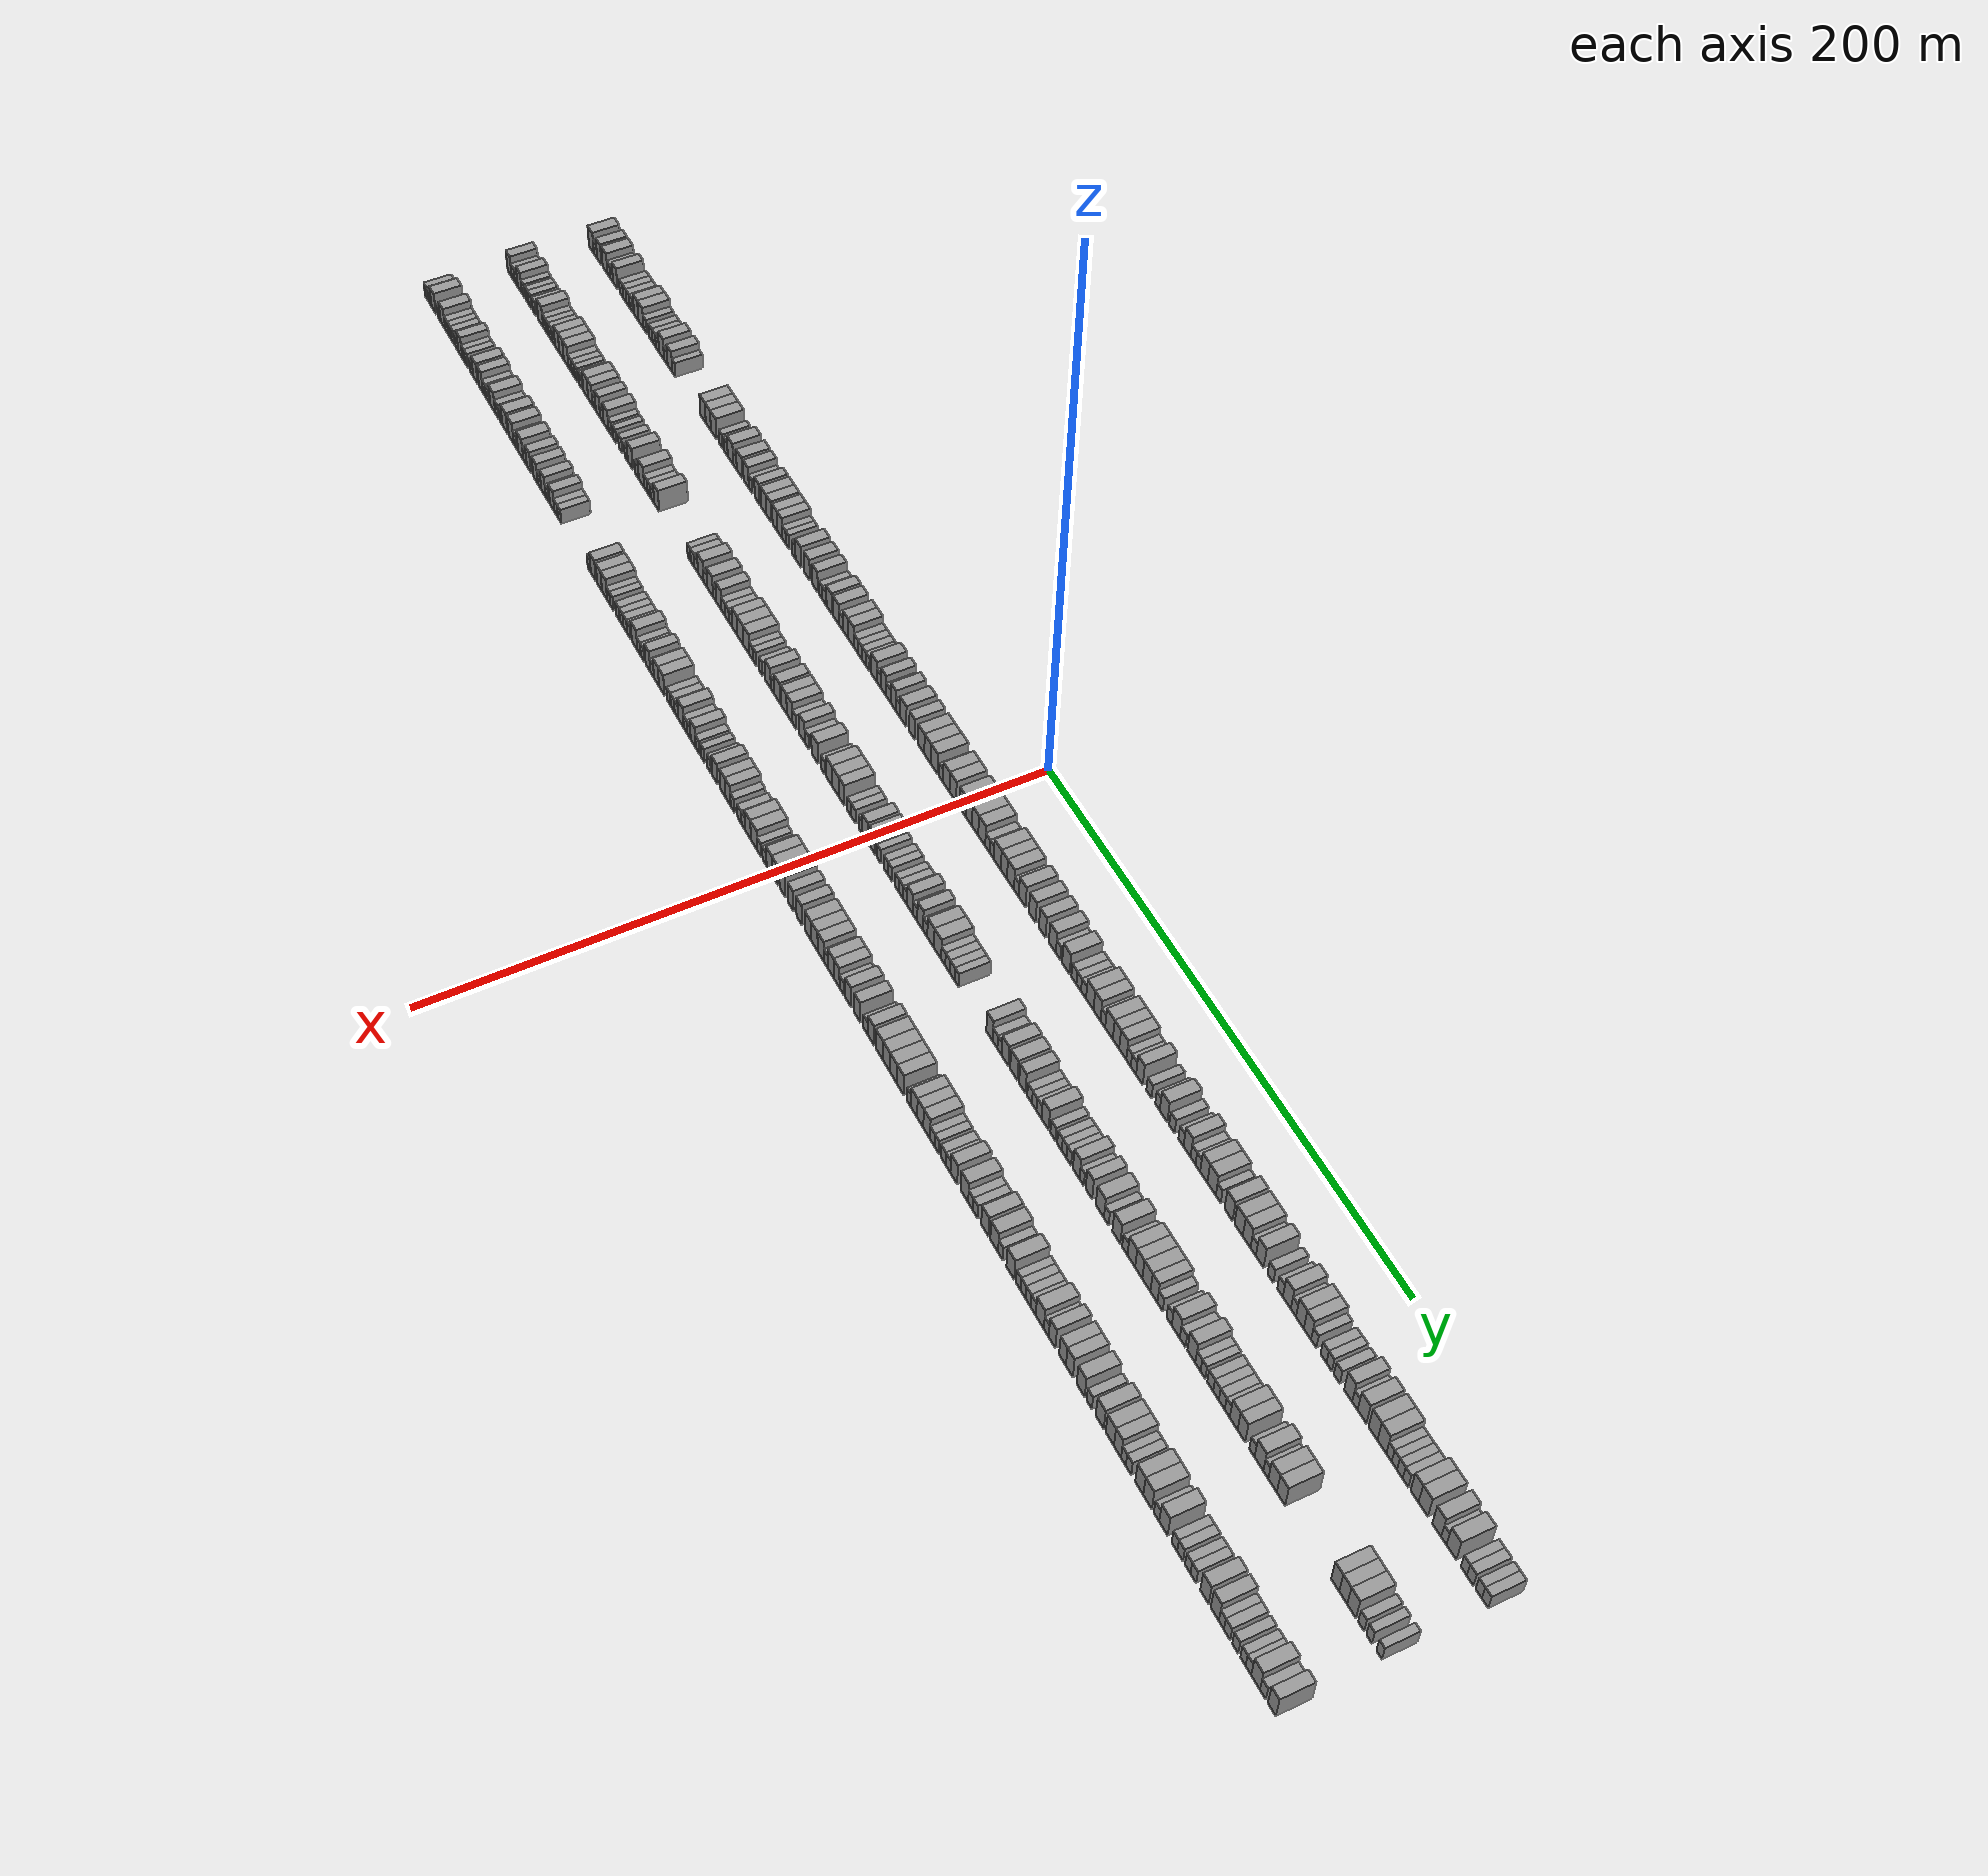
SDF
<sdf version="1.6">
 <world name="default">
  <scene>
   <sky><clouds><speed>12</speed></clouds></sky>
   <ambient>0.4 0.4 0.4 1</ambient>
   <background>0.7 0.7 0.7 1</background>
   <shadows>1</shadows>
  </scene>
  <gravity>0 0 -9.8066</gravity>
  <magnetic_field>6e-06 2.3e-05 -4.2e-05</magnetic_field>
  <physics default="0" name="default_physics" type="ode">
   <ode>
    <solver>
     <type>quick</type>
     <iters>10</iters>
     <sor>1.0</sor>
     <use_dynamic_moi_rescaling>0</use_dynamic_moi_rescaling>
    </solver>
    <constraints>
     <cfm>0</cfm>
     <erp>0.2</erp>
     <contact_max_correcting_vel>100</contact_max_correcting_vel>
     <contact_surface_layer>0.001</contact_surface_layer>
    </constraints>
   </ode>
   <max_step_size>0.004</max_step_size>
   <real_time_factor>1</real_time_factor>
   <real_time_update_rate>250</real_time_update_rate>
  </physics>
  <light name="sun" type="directional">
   <pose>0 0 10 0 0 0</pose>
   <diffuse>0.8 0.8 0.8 1</diffuse>
   <specular>0.2 0.2 0.2 1</specular>
   <attenuation>
    <range>1000</range>
    <constant>0.9</constant>
    <linear>0.01</linear>
    <quadratic>0.001</quadratic>
   </attenuation>
   <direction>-0.5 0.1 -0.9</direction>
  </light>
  <model name="building_1">
   <static>1</static>
   <pose>25.0000 -277.8260 0 0.000000 0.000000 0.000000</pose>
   <link name="link">
    <pose>0 0 4.50 0 0 0</pose>
    <collision name="collision"><geometry><box><size>10.0000 4.3480 9.0000</size></box></geometry></collision>
    <visual name="visual">
     <cast_shadows>0</cast_shadows>
     <geometry><box><size>10.0000 4.3480 9.0000</size></box></geometry>
     <material>
      <script>
       <uri>model://grey_wall/materials/scripts</uri>
       <uri>model://grey_wall/materials/textures</uri>
       <name>vrc/grey_wall</name>
      </script>
     </material>
    </visual>
   </link>
  </model>
  <model name="building_2">
   <static>1</static>
   <pose>25.0000 -274.1869 0 0.000000 0.000000 0.000000</pose>
   <link name="link">
    <pose>0 0 3.00 0 0 0</pose>
    <collision name="collision"><geometry><box><size>10.0000 2.9302 6.0000</size></box></geometry></collision>
    <visual name="visual">
     <cast_shadows>0</cast_shadows>
     <geometry><box><size>10.0000 2.9302 6.0000</size></box></geometry>
     <material>
      <script>
       <uri>model://grey_wall/materials/scripts</uri>
       <uri>model://grey_wall/materials/textures</uri>
       <name>vrc/grey_wall</name>
      </script>
     </material>
    </visual>
   </link>
  </model>
  <model name="building_3">
   <static>1</static>
   <pose>25.0000 -270.8014 0 0.000000 0.000000 0.000000</pose>
   <link name="link">
    <pose>0 0 4.50 0 0 0</pose>
    <collision name="collision"><geometry><box><size>10.0000 3.8408 9.0000</size></box></geometry></collision>
    <visual name="visual">
     <cast_shadows>0</cast_shadows>
     <geometry><box><size>10.0000 3.8408 9.0000</size></box></geometry>
     <material>
      <script>
       <uri>model://grey_wall/materials/scripts</uri>
       <uri>model://grey_wall/materials/textures</uri>
       <name>vrc/grey_wall</name>
      </script>
     </material>
    </visual>
   </link>
  </model>
  <model name="building_4">
   <static>1</static>
   <pose>25.0000 -265.7415 0 0.000000 0.000000 0.000000</pose>
   <link name="link">
    <pose>0 0 4.50 0 0 0</pose>
    <collision name="collision"><geometry><box><size>10.0000 4.2791 9.0000</size></box></geometry></collision>
    <visual name="visual">
     <cast_shadows>0</cast_shadows>
     <geometry><box><size>10.0000 4.2791 9.0000</size></box></geometry>
     <material>
      <script>
       <uri>model://grey_wall/materials/scripts</uri>
       <uri>model://grey_wall/materials/textures</uri>
       <name>vrc/grey_wall</name>
      </script>
     </material>
    </visual>
   </link>
  </model>
  <model name="building_5">
   <static>1</static>
   <pose>25.0000 -262.3979 0 0.000000 0.000000 0.000000</pose>
   <link name="link">
    <pose>0 0 3.00 0 0 0</pose>
    <collision name="collision"><geometry><box><size>10.0000 2.4080 6.0000</size></box></geometry></collision>
    <visual name="visual">
     <cast_shadows>0</cast_shadows>
     <geometry><box><size>10.0000 2.4080 6.0000</size></box></geometry>
     <material>
      <script>
       <uri>model://grey_wall/materials/scripts</uri>
       <uri>model://grey_wall/materials/textures</uri>
       <name>vrc/grey_wall</name>
      </script>
     </material>
    </visual>
   </link>
  </model>
  <model name="building_6">
   <static>1</static>
   <pose>25.0000 -259.9732 0 0.000000 0.000000 0.000000</pose>
   <link name="link">
    <pose>0 0 3.00 0 0 0</pose>
    <collision name="collision"><geometry><box><size>10.0000 2.4414 6.0000</size></box></geometry></collision>
    <visual name="visual">
     <cast_shadows>0</cast_shadows>
     <geometry><box><size>10.0000 2.4414 6.0000</size></box></geometry>
     <material>
      <script>
       <uri>model://grey_wall/materials/scripts</uri>
       <uri>model://grey_wall/materials/textures</uri>
       <name>vrc/grey_wall</name>
      </script>
     </material>
    </visual>
   </link>
  </model>
  <model name="building_7">
   <static>1</static>
   <pose>25.0000 -256.8444 0 0.000000 0.000000 0.000000</pose>
   <link name="link">
    <pose>0 0 4.50 0 0 0</pose>
    <collision name="collision"><geometry><box><size>10.0000 3.8161 9.0000</size></box></geometry></collision>
    <visual name="visual">
     <cast_shadows>0</cast_shadows>
     <geometry><box><size>10.0000 3.8161 9.0000</size></box></geometry>
     <material>
      <script>
       <uri>model://grey_wall/materials/scripts</uri>
       <uri>model://grey_wall/materials/textures</uri>
       <name>vrc/grey_wall</name>
      </script>
     </material>
    </visual>
   </link>
  </model>
  <model name="building_8">
   <static>1</static>
   <pose>25.0000 -251.4877 0 0.000000 0.000000 0.000000</pose>
   <link name="link">
    <pose>0 0 3.00 0 0 0</pose>
    <collision name="collision"><geometry><box><size>10.0000 2.8972 6.0000</size></box></geometry></collision>
    <visual name="visual">
     <cast_shadows>0</cast_shadows>
     <geometry><box><size>10.0000 2.8972 6.0000</size></box></geometry>
     <material>
      <script>
       <uri>model://grey_wall/materials/scripts</uri>
       <uri>model://grey_wall/materials/textures</uri>
       <name>vrc/grey_wall</name>
      </script>
     </material>
    </visual>
   </link>
  </model>
  <model name="building_9">
   <static>1</static>
   <pose>25.0000 -248.6193 0 0.000000 0.000000 0.000000</pose>
   <link name="link">
    <pose>0 0 3.00 0 0 0</pose>
    <collision name="collision"><geometry><box><size>10.0000 2.8397 6.0000</size></box></geometry></collision>
    <visual name="visual">
     <cast_shadows>0</cast_shadows>
     <geometry><box><size>10.0000 2.8397 6.0000</size></box></geometry>
     <material>
      <script>
       <uri>model://grey_wall/materials/scripts</uri>
       <uri>model://grey_wall/materials/textures</uri>
       <name>vrc/grey_wall</name>
      </script>
     </material>
    </visual>
   </link>
  </model>
  <model name="building_10">
   <static>1</static>
   <pose>25.0000 -245.7601 0 0.000000 0.000000 0.000000</pose>
   <link name="link">
    <pose>0 0 3.00 0 0 0</pose>
    <collision name="collision"><geometry><box><size>10.0000 2.8786 6.0000</size></box></geometry></collision>
    <visual name="visual">
     <cast_shadows>0</cast_shadows>
     <geometry><box><size>10.0000 2.8786 6.0000</size></box></geometry>
     <material>
      <script>
       <uri>model://grey_wall/materials/scripts</uri>
       <uri>model://grey_wall/materials/textures</uri>
       <name>vrc/grey_wall</name>
      </script>
     </material>
    </visual>
   </link>
  </model>
  <model name="building_11">
   <static>1</static>
   <pose>25.0000 -242.9808 0 0.000000 0.000000 0.000000</pose>
   <link name="link">
    <pose>0 0 3.00 0 0 0</pose>
    <collision name="collision"><geometry><box><size>10.0000 2.6799 6.0000</size></box></geometry></collision>
    <visual name="visual">
     <cast_shadows>0</cast_shadows>
     <geometry><box><size>10.0000 2.6799 6.0000</size></box></geometry>
     <material>
      <script>
       <uri>model://grey_wall/materials/scripts</uri>
       <uri>model://grey_wall/materials/textures</uri>
       <name>vrc/grey_wall</name>
      </script>
     </material>
    </visual>
   </link>
  </model>
  <model name="building_12">
   <static>1</static>
   <pose>25.0000 -238.7418 0 0.000000 0.000000 0.000000</pose>
   <link name="link">
    <pose>0 0 4.50 0 0 0</pose>
    <collision name="collision"><geometry><box><size>10.0000 3.7983 9.0000</size></box></geometry></collision>
    <visual name="visual">
     <cast_shadows>0</cast_shadows>
     <geometry><box><size>10.0000 3.7983 9.0000</size></box></geometry>
     <material>
      <script>
       <uri>model://grey_wall/materials/scripts</uri>
       <uri>model://grey_wall/materials/textures</uri>
       <name>vrc/grey_wall</name>
      </script>
     </material>
    </visual>
   </link>
  </model>
  <model name="building_13">
   <static>1</static>
   <pose>25.0000 -234.7116 0 0.000000 0.000000 0.000000</pose>
   <link name="link">
    <pose>0 0 4.50 0 0 0</pose>
    <collision name="collision"><geometry><box><size>10.0000 4.2622 9.0000</size></box></geometry></collision>
    <visual name="visual">
     <cast_shadows>0</cast_shadows>
     <geometry><box><size>10.0000 4.2622 9.0000</size></box></geometry>
     <material>
      <script>
       <uri>model://grey_wall/materials/scripts</uri>
       <uri>model://grey_wall/materials/textures</uri>
       <name>vrc/grey_wall</name>
      </script>
     </material>
    </visual>
   </link>
  </model>
  <model name="building_14">
   <static>1</static>
   <pose>25.0000 -231.1592 0 0.000000 0.000000 0.000000</pose>
   <link name="link">
    <pose>0 0 3.00 0 0 0</pose>
    <collision name="collision"><geometry><box><size>10.0000 2.8426 6.0000</size></box></geometry></collision>
    <visual name="visual">
     <cast_shadows>0</cast_shadows>
     <geometry><box><size>10.0000 2.8426 6.0000</size></box></geometry>
     <material>
      <script>
       <uri>model://grey_wall/materials/scripts</uri>
       <uri>model://grey_wall/materials/textures</uri>
       <name>vrc/grey_wall</name>
      </script>
     </material>
    </visual>
   </link>
  </model>
  <model name="building_15">
   <static>1</static>
   <pose>25.0000 -226.3628 0 0.000000 0.000000 0.000000</pose>
   <link name="link">
    <pose>0 0 3.00 0 0 0</pose>
    <collision name="collision"><geometry><box><size>10.0000 2.7502 6.0000</size></box></geometry></collision>
    <visual name="visual">
     <cast_shadows>0</cast_shadows>
     <geometry><box><size>10.0000 2.7502 6.0000</size></box></geometry>
     <material>
      <script>
       <uri>model://grey_wall/materials/scripts</uri>
       <uri>model://grey_wall/materials/textures</uri>
       <name>vrc/grey_wall</name>
      </script>
     </material>
    </visual>
   </link>
  </model>
  <model name="building_16">
   <static>1</static>
   <pose>25.0000 -223.6065 0 0.000000 0.000000 0.000000</pose>
   <link name="link">
    <pose>0 0 3.00 0 0 0</pose>
    <collision name="collision"><geometry><box><size>10.0000 2.7623 6.0000</size></box></geometry></collision>
    <visual name="visual">
     <cast_shadows>0</cast_shadows>
     <geometry><box><size>10.0000 2.7623 6.0000</size></box></geometry>
     <material>
      <script>
       <uri>model://grey_wall/materials/scripts</uri>
       <uri>model://grey_wall/materials/textures</uri>
       <name>vrc/grey_wall</name>
      </script>
     </material>
    </visual>
   </link>
  </model>
  <model name="building_17">
   <static>1</static>
   <pose>25.0000 -220.8768 0 0.000000 0.000000 0.000000</pose>
   <link name="link">
    <pose>0 0 3.00 0 0 0</pose>
    <collision name="collision"><geometry><box><size>10.0000 2.6971 6.0000</size></box></geometry></collision>
    <visual name="visual">
     <cast_shadows>0</cast_shadows>
     <geometry><box><size>10.0000 2.6971 6.0000</size></box></geometry>
     <material>
      <script>
       <uri>model://grey_wall/materials/scripts</uri>
       <uri>model://grey_wall/materials/textures</uri>
       <name>vrc/grey_wall</name>
      </script>
     </material>
    </visual>
   </link>
  </model>
  <model name="building_18">
   <static>1</static>
   <pose>25.0000 -217.4593 0 0.000000 0.000000 0.000000</pose>
   <link name="link">
    <pose>0 0 4.50 0 0 0</pose>
    <collision name="collision"><geometry><box><size>10.0000 4.1379 9.0000</size></box></geometry></collision>
    <visual name="visual">
     <cast_shadows>0</cast_shadows>
     <geometry><box><size>10.0000 4.1379 9.0000</size></box></geometry>
     <material>
      <script>
       <uri>model://grey_wall/materials/scripts</uri>
       <uri>model://grey_wall/materials/textures</uri>
       <name>vrc/grey_wall</name>
      </script>
     </material>
    </visual>
   </link>
  </model>
  <model name="building_19">
   <static>1</static>
   <pose>25.0000 -213.9292 0 0.000000 0.000000 0.000000</pose>
   <link name="link">
    <pose>0 0 3.00 0 0 0</pose>
    <collision name="collision"><geometry><box><size>10.0000 2.9224 6.0000</size></box></geometry></collision>
    <visual name="visual">
     <cast_shadows>0</cast_shadows>
     <geometry><box><size>10.0000 2.9224 6.0000</size></box></geometry>
     <material>
      <script>
       <uri>model://grey_wall/materials/scripts</uri>
       <uri>model://grey_wall/materials/textures</uri>
       <name>vrc/grey_wall</name>
      </script>
     </material>
    </visual>
   </link>
  </model>
  <model name="building_20">
   <static>1</static>
   <pose>25.0000 -210.4902 0 0.000000 0.000000 0.000000</pose>
   <link name="link">
    <pose>0 0 4.50 0 0 0</pose>
    <collision name="collision"><geometry><box><size>10.0000 3.9556 9.0000</size></box></geometry></collision>
    <visual name="visual">
     <cast_shadows>0</cast_shadows>
     <geometry><box><size>10.0000 3.9556 9.0000</size></box></geometry>
     <material>
      <script>
       <uri>model://grey_wall/materials/scripts</uri>
       <uri>model://grey_wall/materials/textures</uri>
       <name>vrc/grey_wall</name>
      </script>
     </material>
    </visual>
   </link>
  </model>
  <model name="building_21">
   <static>1</static>
   <pose>25.0000 -207.2453 0 0.000000 0.000000 0.000000</pose>
   <link name="link">
    <pose>0 0 3.00 0 0 0</pose>
    <collision name="collision"><geometry><box><size>10.0000 2.5341 6.0000</size></box></geometry></collision>
    <visual name="visual">
     <cast_shadows>0</cast_shadows>
     <geometry><box><size>10.0000 2.5341 6.0000</size></box></geometry>
     <material>
      <script>
       <uri>model://grey_wall/materials/scripts</uri>
       <uri>model://grey_wall/materials/textures</uri>
       <name>vrc/grey_wall</name>
      </script>
     </material>
    </visual>
   </link>
  </model>
  <model name="building_22">
   <static>1</static>
   <pose>25.0000 -183.5145 0 0.000000 0.000000 0.000000</pose>
   <link name="link">
    <pose>0 0 4.50 0 0 0</pose>
    <collision name="collision"><geometry><box><size>10.0000 4.3092 9.0000</size></box></geometry></collision>
    <visual name="visual">
     <cast_shadows>0</cast_shadows>
     <geometry><box><size>10.0000 4.3092 9.0000</size></box></geometry>
     <material>
      <script>
       <uri>model://grey_wall/materials/scripts</uri>
       <uri>model://grey_wall/materials/textures</uri>
       <name>vrc/grey_wall</name>
      </script>
     </material>
    </visual>
   </link>
  </model>
  <model name="building_23">
   <static>1</static>
   <pose>25.0000 -179.2970 0 0.000000 0.000000 0.000000</pose>
   <link name="link">
    <pose>0 0 4.50 0 0 0</pose>
    <collision name="collision"><geometry><box><size>10.0000 4.1258 9.0000</size></box></geometry></collision>
    <visual name="visual">
     <cast_shadows>0</cast_shadows>
     <geometry><box><size>10.0000 4.1258 9.0000</size></box></geometry>
     <material>
      <script>
       <uri>model://grey_wall/materials/scripts</uri>
       <uri>model://grey_wall/materials/textures</uri>
       <name>vrc/grey_wall</name>
      </script>
     </material>
    </visual>
   </link>
  </model>
  <model name="building_24">
   <static>1</static>
   <pose>25.0000 -174.9847 0 0.000000 0.000000 0.000000</pose>
   <link name="link">
    <pose>0 0 4.50 0 0 0</pose>
    <collision name="collision"><geometry><box><size>10.0000 4.4987 9.0000</size></box></geometry></collision>
    <visual name="visual">
     <cast_shadows>0</cast_shadows>
     <geometry><box><size>10.0000 4.4987 9.0000</size></box></geometry>
     <material>
      <script>
       <uri>model://grey_wall/materials/scripts</uri>
       <uri>model://grey_wall/materials/textures</uri>
       <name>vrc/grey_wall</name>
      </script>
     </material>
    </visual>
   </link>
  </model>
  <model name="building_25">
   <static>1</static>
   <pose>25.0000 -169.3413 0 0.000000 0.000000 0.000000</pose>
   <link name="link">
    <pose>0 0 3.00 0 0 0</pose>
    <collision name="collision"><geometry><box><size>10.0000 2.7881 6.0000</size></box></geometry></collision>
    <visual name="visual">
     <cast_shadows>0</cast_shadows>
     <geometry><box><size>10.0000 2.7881 6.0000</size></box></geometry>
     <material>
      <script>
       <uri>model://grey_wall/materials/scripts</uri>
       <uri>model://grey_wall/materials/textures</uri>
       <name>vrc/grey_wall</name>
      </script>
     </material>
    </visual>
   </link>
  </model>
  <model name="building_26">
   <static>1</static>
   <pose>25.0000 -165.4572 0 0.000000 0.000000 0.000000</pose>
   <link name="link">
    <pose>0 0 3.00 0 0 0</pose>
    <collision name="collision"><geometry><box><size>10.0000 2.9801 6.0000</size></box></geometry></collision>
    <visual name="visual">
     <cast_shadows>0</cast_shadows>
     <geometry><box><size>10.0000 2.9801 6.0000</size></box></geometry>
     <material>
      <script>
       <uri>model://grey_wall/materials/scripts</uri>
       <uri>model://grey_wall/materials/textures</uri>
       <name>vrc/grey_wall</name>
      </script>
     </material>
    </visual>
   </link>
  </model>
  <model name="building_27">
   <static>1</static>
   <pose>25.0000 -161.8322 0 0.000000 0.000000 0.000000</pose>
   <link name="link">
    <pose>0 0 4.50 0 0 0</pose>
    <collision name="collision"><geometry><box><size>10.0000 4.2700 9.0000</size></box></geometry></collision>
    <visual name="visual">
     <cast_shadows>0</cast_shadows>
     <geometry><box><size>10.0000 4.2700 9.0000</size></box></geometry>
     <material>
      <script>
       <uri>model://grey_wall/materials/scripts</uri>
       <uri>model://grey_wall/materials/textures</uri>
       <name>vrc/grey_wall</name>
      </script>
     </material>
    </visual>
   </link>
  </model>
  <model name="building_28">
   <static>1</static>
   <pose>25.0000 -158.3071 0 0.000000 0.000000 0.000000</pose>
   <link name="link">
    <pose>0 0 3.00 0 0 0</pose>
    <collision name="collision"><geometry><box><size>10.0000 2.7801 6.0000</size></box></geometry></collision>
    <visual name="visual">
     <cast_shadows>0</cast_shadows>
     <geometry><box><size>10.0000 2.7801 6.0000</size></box></geometry>
     <material>
      <script>
       <uri>model://grey_wall/materials/scripts</uri>
       <uri>model://grey_wall/materials/textures</uri>
       <name>vrc/grey_wall</name>
      </script>
     </material>
    </visual>
   </link>
  </model>
  <model name="building_29">
   <static>1</static>
   <pose>25.0000 -154.7487 0 0.000000 0.000000 0.000000</pose>
   <link name="link">
    <pose>0 0 4.50 0 0 0</pose>
    <collision name="collision"><geometry><box><size>10.0000 4.3368 9.0000</size></box></geometry></collision>
    <visual name="visual">
     <cast_shadows>0</cast_shadows>
     <geometry><box><size>10.0000 4.3368 9.0000</size></box></geometry>
     <material>
      <script>
       <uri>model://grey_wall/materials/scripts</uri>
       <uri>model://grey_wall/materials/textures</uri>
       <name>vrc/grey_wall</name>
      </script>
     </material>
    </visual>
   </link>
  </model>
  <model name="building_30">
   <static>1</static>
   <pose>25.0000 -149.6005 0 0.000000 0.000000 0.000000</pose>
   <link name="link">
    <pose>0 0 4.50 0 0 0</pose>
    <collision name="collision"><geometry><box><size>10.0000 3.9595 9.0000</size></box></geometry></collision>
    <visual name="visual">
     <cast_shadows>0</cast_shadows>
     <geometry><box><size>10.0000 3.9595 9.0000</size></box></geometry>
     <material>
      <script>
       <uri>model://grey_wall/materials/scripts</uri>
       <uri>model://grey_wall/materials/textures</uri>
       <name>vrc/grey_wall</name>
      </script>
     </material>
    </visual>
   </link>
  </model>
  <model name="building_31">
   <static>1</static>
   <pose>25.0000 -146.2920 0 0.000000 0.000000 0.000000</pose>
   <link name="link">
    <pose>0 0 3.00 0 0 0</pose>
    <collision name="collision"><geometry><box><size>10.0000 2.6577 6.0000</size></box></geometry></collision>
    <visual name="visual">
     <cast_shadows>0</cast_shadows>
     <geometry><box><size>10.0000 2.6577 6.0000</size></box></geometry>
     <material>
      <script>
       <uri>model://grey_wall/materials/scripts</uri>
       <uri>model://grey_wall/materials/textures</uri>
       <name>vrc/grey_wall</name>
      </script>
     </material>
    </visual>
   </link>
  </model>
  <model name="building_32">
   <static>1</static>
   <pose>25.0000 -141.1317 0 0.000000 0.000000 0.000000</pose>
   <link name="link">
    <pose>0 0 4.50 0 0 0</pose>
    <collision name="collision"><geometry><box><size>10.0000 3.6628 9.0000</size></box></geometry></collision>
    <visual name="visual">
     <cast_shadows>0</cast_shadows>
     <geometry><box><size>10.0000 3.6628 9.0000</size></box></geometry>
     <material>
      <script>
       <uri>model://grey_wall/materials/scripts</uri>
       <uri>model://grey_wall/materials/textures</uri>
       <name>vrc/grey_wall</name>
      </script>
     </material>
    </visual>
   </link>
  </model>
  <model name="building_33">
   <static>1</static>
   <pose>25.0000 -136.3058 0 0.000000 0.000000 0.000000</pose>
   <link name="link">
    <pose>0 0 4.50 0 0 0</pose>
    <collision name="collision"><geometry><box><size>10.0000 3.9890 9.0000</size></box></geometry></collision>
    <visual name="visual">
     <cast_shadows>0</cast_shadows>
     <geometry><box><size>10.0000 3.9890 9.0000</size></box></geometry>
     <material>
      <script>
       <uri>model://grey_wall/materials/scripts</uri>
       <uri>model://grey_wall/materials/textures</uri>
       <name>vrc/grey_wall</name>
      </script>
     </material>
    </visual>
   </link>
  </model>
  <model name="building_34">
   <static>1</static>
   <pose>25.0000 -132.3958 0 0.000000 0.000000 0.000000</pose>
   <link name="link">
    <pose>0 0 4.50 0 0 0</pose>
    <collision name="collision"><geometry><box><size>10.0000 3.8310 9.0000</size></box></geometry></collision>
    <visual name="visual">
     <cast_shadows>0</cast_shadows>
     <geometry><box><size>10.0000 3.8310 9.0000</size></box></geometry>
     <material>
      <script>
       <uri>model://grey_wall/materials/scripts</uri>
       <uri>model://grey_wall/materials/textures</uri>
       <name>vrc/grey_wall</name>
      </script>
     </material>
    </visual>
   </link>
  </model>
  <model name="building_35">
   <static>1</static>
   <pose>25.0000 -127.6404 0 0.000000 0.000000 0.000000</pose>
   <link name="link">
    <pose>0 0 4.50 0 0 0</pose>
    <collision name="collision"><geometry><box><size>10.0000 3.6797 9.0000</size></box></geometry></collision>
    <visual name="visual">
     <cast_shadows>0</cast_shadows>
     <geometry><box><size>10.0000 3.6797 9.0000</size></box></geometry>
     <material>
      <script>
       <uri>model://grey_wall/materials/scripts</uri>
       <uri>model://grey_wall/materials/textures</uri>
       <name>vrc/grey_wall</name>
      </script>
     </material>
    </visual>
   </link>
  </model>
  <model name="building_36">
   <static>1</static>
   <pose>25.0000 -123.9842 0 0.000000 0.000000 0.000000</pose>
   <link name="link">
    <pose>0 0 4.50 0 0 0</pose>
    <collision name="collision"><geometry><box><size>10.0000 3.6327 9.0000</size></box></geometry></collision>
    <visual name="visual">
     <cast_shadows>0</cast_shadows>
     <geometry><box><size>10.0000 3.6327 9.0000</size></box></geometry>
     <material>
      <script>
       <uri>model://grey_wall/materials/scripts</uri>
       <uri>model://grey_wall/materials/textures</uri>
       <name>vrc/grey_wall</name>
      </script>
     </material>
    </visual>
   </link>
  </model>
  <model name="building_37">
   <static>1</static>
   <pose>25.0000 -120.8901 0 0.000000 0.000000 0.000000</pose>
   <link name="link">
    <pose>0 0 3.00 0 0 0</pose>
    <collision name="collision"><geometry><box><size>10.0000 2.5555 6.0000</size></box></geometry></collision>
    <visual name="visual">
     <cast_shadows>0</cast_shadows>
     <geometry><box><size>10.0000 2.5555 6.0000</size></box></geometry>
     <material>
      <script>
       <uri>model://grey_wall/materials/scripts</uri>
       <uri>model://grey_wall/materials/textures</uri>
       <name>vrc/grey_wall</name>
      </script>
     </material>
    </visual>
   </link>
  </model>
  <model name="building_38">
   <static>1</static>
   <pose>25.0000 -118.3707 0 0.000000 0.000000 0.000000</pose>
   <link name="link">
    <pose>0 0 3.00 0 0 0</pose>
    <collision name="collision"><geometry><box><size>10.0000 2.4834 6.0000</size></box></geometry></collision>
    <visual name="visual">
     <cast_shadows>0</cast_shadows>
     <geometry><box><size>10.0000 2.4834 6.0000</size></box></geometry>
     <material>
      <script>
       <uri>model://grey_wall/materials/scripts</uri>
       <uri>model://grey_wall/materials/textures</uri>
       <name>vrc/grey_wall</name>
      </script>
     </material>
    </visual>
   </link>
  </model>
  <model name="building_39">
   <static>1</static>
   <pose>25.0000 -113.7421 0 0.000000 0.000000 0.000000</pose>
   <link name="link">
    <pose>0 0 3.00 0 0 0</pose>
    <collision name="collision"><geometry><box><size>10.0000 2.7738 6.0000</size></box></geometry></collision>
    <visual name="visual">
     <cast_shadows>0</cast_shadows>
     <geometry><box><size>10.0000 2.7738 6.0000</size></box></geometry>
     <material>
      <script>
       <uri>model://grey_wall/materials/scripts</uri>
       <uri>model://grey_wall/materials/textures</uri>
       <name>vrc/grey_wall</name>
      </script>
     </material>
    </visual>
   </link>
  </model>
  <model name="building_40">
   <static>1</static>
   <pose>25.0000 -110.2601 0 0.000000 0.000000 0.000000</pose>
   <link name="link">
    <pose>0 0 4.50 0 0 0</pose>
    <collision name="collision"><geometry><box><size>10.0000 4.1903 9.0000</size></box></geometry></collision>
    <visual name="visual">
     <cast_shadows>0</cast_shadows>
     <geometry><box><size>10.0000 4.1903 9.0000</size></box></geometry>
     <material>
      <script>
       <uri>model://grey_wall/materials/scripts</uri>
       <uri>model://grey_wall/materials/textures</uri>
       <name>vrc/grey_wall</name>
      </script>
     </material>
    </visual>
   </link>
  </model>
  <model name="building_41">
   <static>1</static>
   <pose>25.0000 -104.0432 0 0.000000 0.000000 0.000000</pose>
   <link name="link">
    <pose>0 0 4.50 0 0 0</pose>
    <collision name="collision"><geometry><box><size>10.0000 4.2435 9.0000</size></box></geometry></collision>
    <visual name="visual">
     <cast_shadows>0</cast_shadows>
     <geometry><box><size>10.0000 4.2435 9.0000</size></box></geometry>
     <material>
      <script>
       <uri>model://grey_wall/materials/scripts</uri>
       <uri>model://grey_wall/materials/textures</uri>
       <name>vrc/grey_wall</name>
      </script>
     </material>
    </visual>
   </link>
  </model>
  <model name="building_42">
   <static>1</static>
   <pose>25.0000 -98.0286 0 0.000000 0.000000 0.000000</pose>
   <link name="link">
    <pose>0 0 4.50 0 0 0</pose>
    <collision name="collision"><geometry><box><size>10.0000 3.7858 9.0000</size></box></geometry></collision>
    <visual name="visual">
     <cast_shadows>0</cast_shadows>
     <geometry><box><size>10.0000 3.7858 9.0000</size></box></geometry>
     <material>
      <script>
       <uri>model://grey_wall/materials/scripts</uri>
       <uri>model://grey_wall/materials/textures</uri>
       <name>vrc/grey_wall</name>
      </script>
     </material>
    </visual>
   </link>
  </model>
  <model name="building_43">
   <static>1</static>
   <pose>25.0000 -93.9180 0 0.000000 0.000000 0.000000</pose>
   <link name="link">
    <pose>0 0 3.00 0 0 0</pose>
    <collision name="collision"><geometry><box><size>10.0000 2.4353 6.0000</size></box></geometry></collision>
    <visual name="visual">
     <cast_shadows>0</cast_shadows>
     <geometry><box><size>10.0000 2.4353 6.0000</size></box></geometry>
     <material>
      <script>
       <uri>model://grey_wall/materials/scripts</uri>
       <uri>model://grey_wall/materials/textures</uri>
       <name>vrc/grey_wall</name>
      </script>
     </material>
    </visual>
   </link>
  </model>
  <model name="building_44">
   <static>1</static>
   <pose>25.0000 -91.2287 0 0.000000 0.000000 0.000000</pose>
   <link name="link">
    <pose>0 0 3.00 0 0 0</pose>
    <collision name="collision"><geometry><box><size>10.0000 2.9434 6.0000</size></box></geometry></collision>
    <visual name="visual">
     <cast_shadows>0</cast_shadows>
     <geometry><box><size>10.0000 2.9434 6.0000</size></box></geometry>
     <material>
      <script>
       <uri>model://grey_wall/materials/scripts</uri>
       <uri>model://grey_wall/materials/textures</uri>
       <name>vrc/grey_wall</name>
      </script>
     </material>
    </visual>
   </link>
  </model>
  <model name="building_45">
   <static>1</static>
   <pose>25.0000 -87.8705 0 0.000000 0.000000 0.000000</pose>
   <link name="link">
    <pose>0 0 4.50 0 0 0</pose>
    <collision name="collision"><geometry><box><size>10.0000 3.7730 9.0000</size></box></geometry></collision>
    <visual name="visual">
     <cast_shadows>0</cast_shadows>
     <geometry><box><size>10.0000 3.7730 9.0000</size></box></geometry>
     <material>
      <script>
       <uri>model://grey_wall/materials/scripts</uri>
       <uri>model://grey_wall/materials/textures</uri>
       <name>vrc/grey_wall</name>
      </script>
     </material>
    </visual>
   </link>
  </model>
  <model name="building_46">
   <static>1</static>
   <pose>25.0000 -82.8717 0 0.000000 0.000000 0.000000</pose>
   <link name="link">
    <pose>0 0 4.50 0 0 0</pose>
    <collision name="collision"><geometry><box><size>10.0000 4.2245 9.0000</size></box></geometry></collision>
    <visual name="visual">
     <cast_shadows>0</cast_shadows>
     <geometry><box><size>10.0000 4.2245 9.0000</size></box></geometry>
     <material>
      <script>
       <uri>model://grey_wall/materials/scripts</uri>
       <uri>model://grey_wall/materials/textures</uri>
       <name>vrc/grey_wall</name>
      </script>
     </material>
    </visual>
   </link>
  </model>
  <model name="building_47">
   <static>1</static>
   <pose>25.0000 -79.4530 0 0.000000 0.000000 0.000000</pose>
   <link name="link">
    <pose>0 0 3.00 0 0 0</pose>
    <collision name="collision"><geometry><box><size>10.0000 2.6130 6.0000</size></box></geometry></collision>
    <visual name="visual">
     <cast_shadows>0</cast_shadows>
     <geometry><box><size>10.0000 2.6130 6.0000</size></box></geometry>
     <material>
      <script>
       <uri>model://grey_wall/materials/scripts</uri>
       <uri>model://grey_wall/materials/textures</uri>
       <name>vrc/grey_wall</name>
      </script>
     </material>
    </visual>
   </link>
  </model>
  <model name="building_48">
   <static>1</static>
   <pose>25.0000 -76.3383 0 0.000000 0.000000 0.000000</pose>
   <link name="link">
    <pose>0 0 4.50 0 0 0</pose>
    <collision name="collision"><geometry><box><size>10.0000 3.6164 9.0000</size></box></geometry></collision>
    <visual name="visual">
     <cast_shadows>0</cast_shadows>
     <geometry><box><size>10.0000 3.6164 9.0000</size></box></geometry>
     <material>
      <script>
       <uri>model://grey_wall/materials/scripts</uri>
       <uri>model://grey_wall/materials/textures</uri>
       <name>vrc/grey_wall</name>
      </script>
     </material>
    </visual>
   </link>
  </model>
  <model name="building_49">
   <static>1</static>
   <pose>25.0000 -72.5193 0 0.000000 0.000000 0.000000</pose>
   <link name="link">
    <pose>0 0 4.50 0 0 0</pose>
    <collision name="collision"><geometry><box><size>10.0000 4.0216 9.0000</size></box></geometry></collision>
    <visual name="visual">
     <cast_shadows>0</cast_shadows>
     <geometry><box><size>10.0000 4.0216 9.0000</size></box></geometry>
     <material>
      <script>
       <uri>model://grey_wall/materials/scripts</uri>
       <uri>model://grey_wall/materials/textures</uri>
       <name>vrc/grey_wall</name>
      </script>
     </material>
    </visual>
   </link>
  </model>
  <model name="building_50">
   <static>1</static>
   <pose>25.0000 -69.0408 0 0.000000 0.000000 0.000000</pose>
   <link name="link">
    <pose>0 0 3.00 0 0 0</pose>
    <collision name="collision"><geometry><box><size>10.0000 2.9354 6.0000</size></box></geometry></collision>
    <visual name="visual">
     <cast_shadows>0</cast_shadows>
     <geometry><box><size>10.0000 2.9354 6.0000</size></box></geometry>
     <material>
      <script>
       <uri>model://grey_wall/materials/scripts</uri>
       <uri>model://grey_wall/materials/textures</uri>
       <name>vrc/grey_wall</name>
      </script>
     </material>
    </visual>
   </link>
  </model>
  <model name="building_51">
   <static>1</static>
   <pose>25.0000 -66.1971 0 0.000000 0.000000 0.000000</pose>
   <link name="link">
    <pose>0 0 3.00 0 0 0</pose>
    <collision name="collision"><geometry><box><size>10.0000 2.7520 6.0000</size></box></geometry></collision>
    <visual name="visual">
     <cast_shadows>0</cast_shadows>
     <geometry><box><size>10.0000 2.7520 6.0000</size></box></geometry>
     <material>
      <script>
       <uri>model://grey_wall/materials/scripts</uri>
       <uri>model://grey_wall/materials/textures</uri>
       <name>vrc/grey_wall</name>
      </script>
     </material>
    </visual>
   </link>
  </model>
  <model name="building_52">
   <static>1</static>
   <pose>25.0000 -63.4501 0 0.000000 0.000000 0.000000</pose>
   <link name="link">
    <pose>0 0 3.00 0 0 0</pose>
    <collision name="collision"><geometry><box><size>10.0000 2.7420 6.0000</size></box></geometry></collision>
    <visual name="visual">
     <cast_shadows>0</cast_shadows>
     <geometry><box><size>10.0000 2.7420 6.0000</size></box></geometry>
     <material>
      <script>
       <uri>model://grey_wall/materials/scripts</uri>
       <uri>model://grey_wall/materials/textures</uri>
       <name>vrc/grey_wall</name>
      </script>
     </material>
    </visual>
   </link>
  </model>
  <model name="building_53">
   <static>1</static>
   <pose>25.0000 -60.7589 0 0.000000 0.000000 0.000000</pose>
   <link name="link">
    <pose>0 0 3.00 0 0 0</pose>
    <collision name="collision"><geometry><box><size>10.0000 2.6404 6.0000</size></box></geometry></collision>
    <visual name="visual">
     <cast_shadows>0</cast_shadows>
     <geometry><box><size>10.0000 2.6404 6.0000</size></box></geometry>
     <material>
      <script>
       <uri>model://grey_wall/materials/scripts</uri>
       <uri>model://grey_wall/materials/textures</uri>
       <name>vrc/grey_wall</name>
      </script>
     </material>
    </visual>
   </link>
  </model>
  <model name="building_54">
   <static>1</static>
   <pose>25.0000 -56.2951 0 0.000000 0.000000 0.000000</pose>
   <link name="link">
    <pose>0 0 4.50 0 0 0</pose>
    <collision name="collision"><geometry><box><size>10.0000 4.2872 9.0000</size></box></geometry></collision>
    <visual name="visual">
     <cast_shadows>0</cast_shadows>
     <geometry><box><size>10.0000 4.2872 9.0000</size></box></geometry>
     <material>
      <script>
       <uri>model://grey_wall/materials/scripts</uri>
       <uri>model://grey_wall/materials/textures</uri>
       <name>vrc/grey_wall</name>
      </script>
     </material>
    </visual>
   </link>
  </model>
  <model name="building_55">
   <static>1</static>
   <pose>25.0000 -52.8467 0 0.000000 0.000000 0.000000</pose>
   <link name="link">
    <pose>0 0 3.00 0 0 0</pose>
    <collision name="collision"><geometry><box><size>10.0000 2.6095 6.0000</size></box></geometry></collision>
    <visual name="visual">
     <cast_shadows>0</cast_shadows>
     <geometry><box><size>10.0000 2.6095 6.0000</size></box></geometry>
     <material>
      <script>
       <uri>model://grey_wall/materials/scripts</uri>
       <uri>model://grey_wall/materials/textures</uri>
       <name>vrc/grey_wall</name>
      </script>
     </material>
    </visual>
   </link>
  </model>
  <model name="building_56">
   <static>1</static>
   <pose>25.0000 -49.7008 0 0.000000 0.000000 0.000000</pose>
   <link name="link">
    <pose>0 0 4.50 0 0 0</pose>
    <collision name="collision"><geometry><box><size>10.0000 3.6824 9.0000</size></box></geometry></collision>
    <visual name="visual">
     <cast_shadows>0</cast_shadows>
     <geometry><box><size>10.0000 3.6824 9.0000</size></box></geometry>
     <material>
      <script>
       <uri>model://grey_wall/materials/scripts</uri>
       <uri>model://grey_wall/materials/textures</uri>
       <name>vrc/grey_wall</name>
      </script>
     </material>
    </visual>
   </link>
  </model>
  <model name="building_57">
   <static>1</static>
   <pose>25.0000 -46.3667 0 0.000000 0.000000 0.000000</pose>
   <link name="link">
    <pose>0 0 3.00 0 0 0</pose>
    <collision name="collision"><geometry><box><size>10.0000 2.9858 6.0000</size></box></geometry></collision>
    <visual name="visual">
     <cast_shadows>0</cast_shadows>
     <geometry><box><size>10.0000 2.9858 6.0000</size></box></geometry>
     <material>
      <script>
       <uri>model://grey_wall/materials/scripts</uri>
       <uri>model://grey_wall/materials/textures</uri>
       <name>vrc/grey_wall</name>
      </script>
     </material>
    </visual>
   </link>
  </model>
  <model name="building_58">
   <static>1</static>
   <pose>25.0000 -43.0493 0 0.000000 0.000000 0.000000</pose>
   <link name="link">
    <pose>0 0 4.50 0 0 0</pose>
    <collision name="collision"><geometry><box><size>10.0000 3.6489 9.0000</size></box></geometry></collision>
    <visual name="visual">
     <cast_shadows>0</cast_shadows>
     <geometry><box><size>10.0000 3.6489 9.0000</size></box></geometry>
     <material>
      <script>
       <uri>model://grey_wall/materials/scripts</uri>
       <uri>model://grey_wall/materials/textures</uri>
       <name>vrc/grey_wall</name>
      </script>
     </material>
    </visual>
   </link>
  </model>
  <model name="building_59">
   <static>1</static>
   <pose>25.0000 -40.0002 0 0.000000 0.000000 0.000000</pose>
   <link name="link">
    <pose>0 0 3.00 0 0 0</pose>
    <collision name="collision"><geometry><box><size>10.0000 2.4494 6.0000</size></box></geometry></collision>
    <visual name="visual">
     <cast_shadows>0</cast_shadows>
     <geometry><box><size>10.0000 2.4494 6.0000</size></box></geometry>
     <material>
      <script>
       <uri>model://grey_wall/materials/scripts</uri>
       <uri>model://grey_wall/materials/textures</uri>
       <name>vrc/grey_wall</name>
      </script>
     </material>
    </visual>
   </link>
  </model>
  <model name="building_60">
   <static>1</static>
   <pose>25.0000 -36.5523 0 0.000000 0.000000 0.000000</pose>
   <link name="link">
    <pose>0 0 4.50 0 0 0</pose>
    <collision name="collision"><geometry><box><size>10.0000 4.4465 9.0000</size></box></geometry></collision>
    <visual name="visual">
     <cast_shadows>0</cast_shadows>
     <geometry><box><size>10.0000 4.4465 9.0000</size></box></geometry>
     <material>
      <script>
       <uri>model://grey_wall/materials/scripts</uri>
       <uri>model://grey_wall/materials/textures</uri>
       <name>vrc/grey_wall</name>
      </script>
     </material>
    </visual>
   </link>
  </model>
  <model name="building_61">
   <static>1</static>
   <pose>25.0000 -30.4318 0 0.000000 0.000000 0.000000</pose>
   <link name="link">
    <pose>0 0 4.50 0 0 0</pose>
    <collision name="collision"><geometry><box><size>10.0000 3.7944 9.0000</size></box></geometry></collision>
    <visual name="visual">
     <cast_shadows>0</cast_shadows>
     <geometry><box><size>10.0000 3.7944 9.0000</size></box></geometry>
     <material>
      <script>
       <uri>model://grey_wall/materials/scripts</uri>
       <uri>model://grey_wall/materials/textures</uri>
       <name>vrc/grey_wall</name>
      </script>
     </material>
    </visual>
   </link>
  </model>
  <model name="building_62">
   <static>1</static>
   <pose>25.0000 -24.4105 0 0.000000 0.000000 0.000000</pose>
   <link name="link">
    <pose>0 0 4.50 0 0 0</pose>
    <collision name="collision"><geometry><box><size>10.0000 4.2481 9.0000</size></box></geometry></collision>
    <visual name="visual">
     <cast_shadows>0</cast_shadows>
     <geometry><box><size>10.0000 4.2481 9.0000</size></box></geometry>
     <material>
      <script>
       <uri>model://grey_wall/materials/scripts</uri>
       <uri>model://grey_wall/materials/textures</uri>
       <name>vrc/grey_wall</name>
      </script>
     </material>
    </visual>
   </link>
  </model>
  <model name="building_63">
   <static>1</static>
   <pose>25.0000 -20.1340 0 0.000000 0.000000 0.000000</pose>
   <link name="link">
    <pose>0 0 4.50 0 0 0</pose>
    <collision name="collision"><geometry><box><size>10.0000 4.3049 9.0000</size></box></geometry></collision>
    <visual name="visual">
     <cast_shadows>0</cast_shadows>
     <geometry><box><size>10.0000 4.3049 9.0000</size></box></geometry>
     <material>
      <script>
       <uri>model://grey_wall/materials/scripts</uri>
       <uri>model://grey_wall/materials/textures</uri>
       <name>vrc/grey_wall</name>
      </script>
     </material>
    </visual>
   </link>
  </model>
  <model name="building_64">
   <static>1</static>
   <pose>25.0000 -15.7413 0 0.000000 0.000000 0.000000</pose>
   <link name="link">
    <pose>0 0 4.50 0 0 0</pose>
    <collision name="collision"><geometry><box><size>10.0000 4.4805 9.0000</size></box></geometry></collision>
    <visual name="visual">
     <cast_shadows>0</cast_shadows>
     <geometry><box><size>10.0000 4.4805 9.0000</size></box></geometry>
     <material>
      <script>
       <uri>model://grey_wall/materials/scripts</uri>
       <uri>model://grey_wall/materials/textures</uri>
       <name>vrc/grey_wall</name>
      </script>
     </material>
    </visual>
   </link>
  </model>
  <model name="building_65">
   <static>1</static>
   <pose>25.0000 -11.2513 0 0.000000 0.000000 0.000000</pose>
   <link name="link">
    <pose>0 0 3.00 0 0 0</pose>
    <collision name="collision"><geometry><box><size>10.0000 2.4995 6.0000</size></box></geometry></collision>
    <visual name="visual">
     <cast_shadows>0</cast_shadows>
     <geometry><box><size>10.0000 2.4995 6.0000</size></box></geometry>
     <material>
      <script>
       <uri>model://grey_wall/materials/scripts</uri>
       <uri>model://grey_wall/materials/textures</uri>
       <name>vrc/grey_wall</name>
      </script>
     </material>
    </visual>
   </link>
  </model>
  <model name="building_66">
   <static>1</static>
   <pose>25.0000 -7.8905 0 0.000000 0.000000 0.000000</pose>
   <link name="link">
    <pose>0 0 4.50 0 0 0</pose>
    <collision name="collision"><geometry><box><size>10.0000 4.2222 9.0000</size></box></geometry></collision>
    <visual name="visual">
     <cast_shadows>0</cast_shadows>
     <geometry><box><size>10.0000 4.2222 9.0000</size></box></geometry>
     <material>
      <script>
       <uri>model://grey_wall/materials/scripts</uri>
       <uri>model://grey_wall/materials/textures</uri>
       <name>vrc/grey_wall</name>
      </script>
     </material>
    </visual>
   </link>
  </model>
  <model name="building_67">
   <static>1</static>
   <pose>25.0000 -3.6520 0 0.000000 0.000000 0.000000</pose>
   <link name="link">
    <pose>0 0 4.50 0 0 0</pose>
    <collision name="collision"><geometry><box><size>10.0000 4.2549 9.0000</size></box></geometry></collision>
    <visual name="visual">
     <cast_shadows>0</cast_shadows>
     <geometry><box><size>10.0000 4.2549 9.0000</size></box></geometry>
     <material>
      <script>
       <uri>model://grey_wall/materials/scripts</uri>
       <uri>model://grey_wall/materials/textures</uri>
       <name>vrc/grey_wall</name>
      </script>
     </material>
    </visual>
   </link>
  </model>
  <model name="building_68">
   <static>1</static>
   <pose>25.0000 2.7188 0 0.000000 0.000000 0.000000</pose>
   <link name="link">
    <pose>0 0 4.50 0 0 0</pose>
    <collision name="collision"><geometry><box><size>10.0000 4.4867 9.0000</size></box></geometry></collision>
    <visual name="visual">
     <cast_shadows>0</cast_shadows>
     <geometry><box><size>10.0000 4.4867 9.0000</size></box></geometry>
     <material>
      <script>
       <uri>model://grey_wall/materials/scripts</uri>
       <uri>model://grey_wall/materials/textures</uri>
       <name>vrc/grey_wall</name>
      </script>
     </material>
    </visual>
   </link>
  </model>
  <model name="building_69">
   <static>1</static>
   <pose>25.0000 6.8069 0 0.000000 0.000000 0.000000</pose>
   <link name="link">
    <pose>0 0 4.50 0 0 0</pose>
    <collision name="collision"><geometry><box><size>10.0000 3.6895 9.0000</size></box></geometry></collision>
    <visual name="visual">
     <cast_shadows>0</cast_shadows>
     <geometry><box><size>10.0000 3.6895 9.0000</size></box></geometry>
     <material>
      <script>
       <uri>model://grey_wall/materials/scripts</uri>
       <uri>model://grey_wall/materials/textures</uri>
       <name>vrc/grey_wall</name>
      </script>
     </material>
    </visual>
   </link>
  </model>
  <model name="building_70">
   <static>1</static>
   <pose>25.0000 10.6622 0 0.000000 0.000000 0.000000</pose>
   <link name="link">
    <pose>0 0 4.50 0 0 0</pose>
    <collision name="collision"><geometry><box><size>10.0000 4.0211 9.0000</size></box></geometry></collision>
    <visual name="visual">
     <cast_shadows>0</cast_shadows>
     <geometry><box><size>10.0000 4.0211 9.0000</size></box></geometry>
     <material>
      <script>
       <uri>model://grey_wall/materials/scripts</uri>
       <uri>model://grey_wall/materials/textures</uri>
       <name>vrc/grey_wall</name>
      </script>
     </material>
    </visual>
   </link>
  </model>
  <model name="building_71">
   <static>1</static>
   <pose>25.0000 14.8831 0 0.000000 0.000000 0.000000</pose>
   <link name="link">
    <pose>0 0 4.50 0 0 0</pose>
    <collision name="collision"><geometry><box><size>10.0000 4.4206 9.0000</size></box></geometry></collision>
    <visual name="visual">
     <cast_shadows>0</cast_shadows>
     <geometry><box><size>10.0000 4.4206 9.0000</size></box></geometry>
     <material>
      <script>
       <uri>model://grey_wall/materials/scripts</uri>
       <uri>model://grey_wall/materials/textures</uri>
       <name>vrc/grey_wall</name>
      </script>
     </material>
    </visual>
   </link>
  </model>
  <model name="building_72">
   <static>1</static>
   <pose>25.0000 18.5226 0 0.000000 0.000000 0.000000</pose>
   <link name="link">
    <pose>0 0 3.00 0 0 0</pose>
    <collision name="collision"><geometry><box><size>10.0000 2.8583 6.0000</size></box></geometry></collision>
    <visual name="visual">
     <cast_shadows>0</cast_shadows>
     <geometry><box><size>10.0000 2.8583 6.0000</size></box></geometry>
     <material>
      <script>
       <uri>model://grey_wall/materials/scripts</uri>
       <uri>model://grey_wall/materials/textures</uri>
       <name>vrc/grey_wall</name>
      </script>
     </material>
    </visual>
   </link>
  </model>
  <model name="building_73">
   <static>1</static>
   <pose>25.0000 21.1987 0 0.000000 0.000000 0.000000</pose>
   <link name="link">
    <pose>0 0 3.00 0 0 0</pose>
    <collision name="collision"><geometry><box><size>10.0000 2.4939 6.0000</size></box></geometry></collision>
    <visual name="visual">
     <cast_shadows>0</cast_shadows>
     <geometry><box><size>10.0000 2.4939 6.0000</size></box></geometry>
     <material>
      <script>
       <uri>model://grey_wall/materials/scripts</uri>
       <uri>model://grey_wall/materials/textures</uri>
       <name>vrc/grey_wall</name>
      </script>
     </material>
    </visual>
   </link>
  </model>
  <model name="building_74">
   <static>1</static>
   <pose>25.0000 24.6305 0 0.000000 0.000000 0.000000</pose>
   <link name="link">
    <pose>0 0 4.50 0 0 0</pose>
    <collision name="collision"><geometry><box><size>10.0000 4.3699 9.0000</size></box></geometry></collision>
    <visual name="visual">
     <cast_shadows>0</cast_shadows>
     <geometry><box><size>10.0000 4.3699 9.0000</size></box></geometry>
     <material>
      <script>
       <uri>model://grey_wall/materials/scripts</uri>
       <uri>model://grey_wall/materials/textures</uri>
       <name>vrc/grey_wall</name>
      </script>
     </material>
    </visual>
   </link>
  </model>
  <model name="building_75">
   <static>1</static>
   <pose>25.0000 28.7392 0 0.000000 0.000000 0.000000</pose>
   <link name="link">
    <pose>0 0 4.50 0 0 0</pose>
    <collision name="collision"><geometry><box><size>10.0000 3.8474 9.0000</size></box></geometry></collision>
    <visual name="visual">
     <cast_shadows>0</cast_shadows>
     <geometry><box><size>10.0000 3.8474 9.0000</size></box></geometry>
     <material>
      <script>
       <uri>model://grey_wall/materials/scripts</uri>
       <uri>model://grey_wall/materials/textures</uri>
       <name>vrc/grey_wall</name>
      </script>
     </material>
    </visual>
   </link>
  </model>
  <model name="building_76">
   <static>1</static>
   <pose>25.0000 32.8448 0 0.000000 0.000000 0.000000</pose>
   <link name="link">
    <pose>0 0 4.50 0 0 0</pose>
    <collision name="collision"><geometry><box><size>10.0000 4.3639 9.0000</size></box></geometry></collision>
    <visual name="visual">
     <cast_shadows>0</cast_shadows>
     <geometry><box><size>10.0000 4.3639 9.0000</size></box></geometry>
     <material>
      <script>
       <uri>model://grey_wall/materials/scripts</uri>
       <uri>model://grey_wall/materials/textures</uri>
       <name>vrc/grey_wall</name>
      </script>
     </material>
    </visual>
   </link>
  </model>
  <model name="building_77">
   <static>1</static>
   <pose>25.0000 36.4852 0 0.000000 0.000000 0.000000</pose>
   <link name="link">
    <pose>0 0 3.00 0 0 0</pose>
    <collision name="collision"><geometry><box><size>10.0000 2.9167 6.0000</size></box></geometry></collision>
    <visual name="visual">
     <cast_shadows>0</cast_shadows>
     <geometry><box><size>10.0000 2.9167 6.0000</size></box></geometry>
     <material>
      <script>
       <uri>model://grey_wall/materials/scripts</uri>
       <uri>model://grey_wall/materials/textures</uri>
       <name>vrc/grey_wall</name>
      </script>
     </material>
    </visual>
   </link>
  </model>
  <model name="building_78">
   <static>1</static>
   <pose>25.0000 40.0395 0 0.000000 0.000000 0.000000</pose>
   <link name="link">
    <pose>0 0 4.50 0 0 0</pose>
    <collision name="collision"><geometry><box><size>10.0000 4.1920 9.0000</size></box></geometry></collision>
    <visual name="visual">
     <cast_shadows>0</cast_shadows>
     <geometry><box><size>10.0000 4.1920 9.0000</size></box></geometry>
     <material>
      <script>
       <uri>model://grey_wall/materials/scripts</uri>
       <uri>model://grey_wall/materials/textures</uri>
       <name>vrc/grey_wall</name>
      </script>
     </material>
    </visual>
   </link>
  </model>
  <model name="building_79">
   <static>1</static>
   <pose>25.0000 46.1727 0 0.000000 0.000000 0.000000</pose>
   <link name="link">
    <pose>0 0 4.50 0 0 0</pose>
    <collision name="collision"><geometry><box><size>10.0000 4.0743 9.0000</size></box></geometry></collision>
    <visual name="visual">
     <cast_shadows>0</cast_shadows>
     <geometry><box><size>10.0000 4.0743 9.0000</size></box></geometry>
     <material>
      <script>
       <uri>model://grey_wall/materials/scripts</uri>
       <uri>model://grey_wall/materials/textures</uri>
       <name>vrc/grey_wall</name>
      </script>
     </material>
    </visual>
   </link>
  </model>
  <model name="building_80">
   <static>1</static>
   <pose>25.0000 52.2168 0 0.000000 0.000000 0.000000</pose>
   <link name="link">
    <pose>0 0 4.50 0 0 0</pose>
    <collision name="collision"><geometry><box><size>10.0000 4.0139 9.0000</size></box></geometry></collision>
    <visual name="visual">
     <cast_shadows>0</cast_shadows>
     <geometry><box><size>10.0000 4.0139 9.0000</size></box></geometry>
     <material>
      <script>
       <uri>model://grey_wall/materials/scripts</uri>
       <uri>model://grey_wall/materials/textures</uri>
       <name>vrc/grey_wall</name>
      </script>
     </material>
    </visual>
   </link>
  </model>
  <model name="building_81">
   <static>1</static>
   <pose>25.0000 58.3183 0 0.000000 0.000000 0.000000</pose>
   <link name="link">
    <pose>0 0 4.50 0 0 0</pose>
    <collision name="collision"><geometry><box><size>10.0000 4.1893 9.0000</size></box></geometry></collision>
    <visual name="visual">
     <cast_shadows>0</cast_shadows>
     <geometry><box><size>10.0000 4.1893 9.0000</size></box></geometry>
     <material>
      <script>
       <uri>model://grey_wall/materials/scripts</uri>
       <uri>model://grey_wall/materials/textures</uri>
       <name>vrc/grey_wall</name>
      </script>
     </material>
    </visual>
   </link>
  </model>
  <model name="building_82">
   <static>1</static>
   <pose>25.0000 61.7680 0 0.000000 0.000000 0.000000</pose>
   <link name="link">
    <pose>0 0 3.00 0 0 0</pose>
    <collision name="collision"><geometry><box><size>10.0000 2.7101 6.0000</size></box></geometry></collision>
    <visual name="visual">
     <cast_shadows>0</cast_shadows>
     <geometry><box><size>10.0000 2.7101 6.0000</size></box></geometry>
     <material>
      <script>
       <uri>model://grey_wall/materials/scripts</uri>
       <uri>model://grey_wall/materials/textures</uri>
       <name>vrc/grey_wall</name>
      </script>
     </material>
    </visual>
   </link>
  </model>
  <model name="building_83">
   <static>1</static>
   <pose>25.0000 66.3542 0 0.000000 0.000000 0.000000</pose>
   <link name="link">
    <pose>0 0 4.50 0 0 0</pose>
    <collision name="collision"><geometry><box><size>10.0000 4.4623 9.0000</size></box></geometry></collision>
    <visual name="visual">
     <cast_shadows>0</cast_shadows>
     <geometry><box><size>10.0000 4.4623 9.0000</size></box></geometry>
     <material>
      <script>
       <uri>model://grey_wall/materials/scripts</uri>
       <uri>model://grey_wall/materials/textures</uri>
       <name>vrc/grey_wall</name>
      </script>
     </material>
    </visual>
   </link>
  </model>
  <model name="building_84">
   <static>1</static>
   <pose>25.0000 71.0822 0 0.000000 0.000000 0.000000</pose>
   <link name="link">
    <pose>0 0 3.00 0 0 0</pose>
    <collision name="collision"><geometry><box><size>10.0000 2.9936 6.0000</size></box></geometry></collision>
    <visual name="visual">
     <cast_shadows>0</cast_shadows>
     <geometry><box><size>10.0000 2.9936 6.0000</size></box></geometry>
     <material>
      <script>
       <uri>model://grey_wall/materials/scripts</uri>
       <uri>model://grey_wall/materials/textures</uri>
       <name>vrc/grey_wall</name>
      </script>
     </material>
    </visual>
   </link>
  </model>
  <model name="building_85">
   <static>1</static>
   <pose>25.0000 73.9294 0 0.000000 0.000000 0.000000</pose>
   <link name="link">
    <pose>0 0 3.00 0 0 0</pose>
    <collision name="collision"><geometry><box><size>10.0000 2.7008 6.0000</size></box></geometry></collision>
    <visual name="visual">
     <cast_shadows>0</cast_shadows>
     <geometry><box><size>10.0000 2.7008 6.0000</size></box></geometry>
     <material>
      <script>
       <uri>model://grey_wall/materials/scripts</uri>
       <uri>model://grey_wall/materials/textures</uri>
       <name>vrc/grey_wall</name>
      </script>
     </material>
    </visual>
   </link>
  </model>
  <model name="building_86">
   <static>1</static>
   <pose>25.0000 76.7433 0 0.000000 0.000000 0.000000</pose>
   <link name="link">
    <pose>0 0 3.00 0 0 0</pose>
    <collision name="collision"><geometry><box><size>10.0000 2.9270 6.0000</size></box></geometry></collision>
    <visual name="visual">
     <cast_shadows>0</cast_shadows>
     <geometry><box><size>10.0000 2.9270 6.0000</size></box></geometry>
     <material>
      <script>
       <uri>model://grey_wall/materials/scripts</uri>
       <uri>model://grey_wall/materials/textures</uri>
       <name>vrc/grey_wall</name>
      </script>
     </material>
    </visual>
   </link>
  </model>
  <model name="building_87">
   <static>1</static>
   <pose>25.0000 80.3713 0 0.000000 0.000000 0.000000</pose>
   <link name="link">
    <pose>0 0 4.50 0 0 0</pose>
    <collision name="collision"><geometry><box><size>10.0000 4.3292 9.0000</size></box></geometry></collision>
    <visual name="visual">
     <cast_shadows>0</cast_shadows>
     <geometry><box><size>10.0000 4.3292 9.0000</size></box></geometry>
     <material>
      <script>
       <uri>model://grey_wall/materials/scripts</uri>
       <uri>model://grey_wall/materials/textures</uri>
       <name>vrc/grey_wall</name>
      </script>
     </material>
    </visual>
   </link>
  </model>
  <model name="building_88">
   <static>1</static>
   <pose>25.0000 84.5508 0 0.000000 0.000000 0.000000</pose>
   <link name="link">
    <pose>0 0 4.50 0 0 0</pose>
    <collision name="collision"><geometry><box><size>10.0000 4.0297 9.0000</size></box></geometry></collision>
    <visual name="visual">
     <cast_shadows>0</cast_shadows>
     <geometry><box><size>10.0000 4.0297 9.0000</size></box></geometry>
     <material>
      <script>
       <uri>model://grey_wall/materials/scripts</uri>
       <uri>model://grey_wall/materials/textures</uri>
       <name>vrc/grey_wall</name>
      </script>
     </material>
    </visual>
   </link>
  </model>
  <model name="building_89">
   <static>1</static>
   <pose>25.0000 87.9075 0 0.000000 0.000000 0.000000</pose>
   <link name="link">
    <pose>0 0 3.00 0 0 0</pose>
    <collision name="collision"><geometry><box><size>10.0000 2.6836 6.0000</size></box></geometry></collision>
    <visual name="visual">
     <cast_shadows>0</cast_shadows>
     <geometry><box><size>10.0000 2.6836 6.0000</size></box></geometry>
     <material>
      <script>
       <uri>model://grey_wall/materials/scripts</uri>
       <uri>model://grey_wall/materials/textures</uri>
       <name>vrc/grey_wall</name>
      </script>
     </material>
    </visual>
   </link>
  </model>
  <model name="building_90">
   <static>1</static>
   <pose>25.0000 91.4385 0 0.000000 0.000000 0.000000</pose>
   <link name="link">
    <pose>0 0 4.50 0 0 0</pose>
    <collision name="collision"><geometry><box><size>10.0000 4.3784 9.0000</size></box></geometry></collision>
    <visual name="visual">
     <cast_shadows>0</cast_shadows>
     <geometry><box><size>10.0000 4.3784 9.0000</size></box></geometry>
     <material>
      <script>
       <uri>model://grey_wall/materials/scripts</uri>
       <uri>model://grey_wall/materials/textures</uri>
       <name>vrc/grey_wall</name>
      </script>
     </material>
    </visual>
   </link>
  </model>
  <model name="building_91">
   <static>1</static>
   <pose>25.0000 95.4313 0 0.000000 0.000000 0.000000</pose>
   <link name="link">
    <pose>0 0 4.50 0 0 0</pose>
    <collision name="collision"><geometry><box><size>10.0000 3.6072 9.0000</size></box></geometry></collision>
    <visual name="visual">
     <cast_shadows>0</cast_shadows>
     <geometry><box><size>10.0000 3.6072 9.0000</size></box></geometry>
     <material>
      <script>
       <uri>model://grey_wall/materials/scripts</uri>
       <uri>model://grey_wall/materials/textures</uri>
       <name>vrc/grey_wall</name>
      </script>
     </material>
    </visual>
   </link>
  </model>
  <model name="building_92">
   <static>1</static>
   <pose>25.0000 99.2605 0 0.000000 0.000000 0.000000</pose>
   <link name="link">
    <pose>0 0 4.50 0 0 0</pose>
    <collision name="collision"><geometry><box><size>10.0000 4.0514 9.0000</size></box></geometry></collision>
    <visual name="visual">
     <cast_shadows>0</cast_shadows>
     <geometry><box><size>10.0000 4.0514 9.0000</size></box></geometry>
     <material>
      <script>
       <uri>model://grey_wall/materials/scripts</uri>
       <uri>model://grey_wall/materials/textures</uri>
       <name>vrc/grey_wall</name>
      </script>
     </material>
    </visual>
   </link>
  </model>
  <model name="building_93">
   <static>1</static>
   <pose>25.0000 102.5694 0 0.000000 0.000000 0.000000</pose>
   <link name="link">
    <pose>0 0 3.00 0 0 0</pose>
    <collision name="collision"><geometry><box><size>10.0000 2.5665 6.0000</size></box></geometry></collision>
    <visual name="visual">
     <cast_shadows>0</cast_shadows>
     <geometry><box><size>10.0000 2.5665 6.0000</size></box></geometry>
     <material>
      <script>
       <uri>model://grey_wall/materials/scripts</uri>
       <uri>model://grey_wall/materials/textures</uri>
       <name>vrc/grey_wall</name>
      </script>
     </material>
    </visual>
   </link>
  </model>
  <model name="building_94">
   <static>1</static>
   <pose>25.0000 105.3348 0 0.000000 0.000000 0.000000</pose>
   <link name="link">
    <pose>0 0 3.00 0 0 0</pose>
    <collision name="collision"><geometry><box><size>10.0000 2.9642 6.0000</size></box></geometry></collision>
    <visual name="visual">
     <cast_shadows>0</cast_shadows>
     <geometry><box><size>10.0000 2.9642 6.0000</size></box></geometry>
     <material>
      <script>
       <uri>model://grey_wall/materials/scripts</uri>
       <uri>model://grey_wall/materials/textures</uri>
       <name>vrc/grey_wall</name>
      </script>
     </material>
    </visual>
   </link>
  </model>
  <model name="building_95">
   <static>1</static>
   <pose>25.0000 108.6636 0 0.000000 0.000000 0.000000</pose>
   <link name="link">
    <pose>0 0 4.50 0 0 0</pose>
    <collision name="collision"><geometry><box><size>10.0000 3.6935 9.0000</size></box></geometry></collision>
    <visual name="visual">
     <cast_shadows>0</cast_shadows>
     <geometry><box><size>10.0000 3.6935 9.0000</size></box></geometry>
     <material>
      <script>
       <uri>model://grey_wall/materials/scripts</uri>
       <uri>model://grey_wall/materials/textures</uri>
       <name>vrc/grey_wall</name>
      </script>
     </material>
    </visual>
   </link>
  </model>
  <model name="building_96">
   <static>1</static>
   <pose>25.0000 113.9725 0 0.000000 0.000000 0.000000</pose>
   <link name="link">
    <pose>0 0 3.00 0 0 0</pose>
    <collision name="collision"><geometry><box><size>10.0000 2.9242 6.0000</size></box></geometry></collision>
    <visual name="visual">
     <cast_shadows>0</cast_shadows>
     <geometry><box><size>10.0000 2.9242 6.0000</size></box></geometry>
     <material>
      <script>
       <uri>model://grey_wall/materials/scripts</uri>
       <uri>model://grey_wall/materials/textures</uri>
       <name>vrc/grey_wall</name>
      </script>
     </material>
    </visual>
   </link>
  </model>
  <model name="building_97">
   <static>1</static>
   <pose>25.0000 118.6949 0 0.000000 0.000000 0.000000</pose>
   <link name="link">
    <pose>0 0 3.00 0 0 0</pose>
    <collision name="collision"><geometry><box><size>10.0000 2.5206 6.0000</size></box></geometry></collision>
    <visual name="visual">
     <cast_shadows>0</cast_shadows>
     <geometry><box><size>10.0000 2.5206 6.0000</size></box></geometry>
     <material>
      <script>
       <uri>model://grey_wall/materials/scripts</uri>
       <uri>model://grey_wall/materials/textures</uri>
       <name>vrc/grey_wall</name>
      </script>
     </material>
    </visual>
   </link>
  </model>
  <model name="building_98">
   <static>1</static>
   <pose>25.0000 122.0379 0 0.000000 0.000000 0.000000</pose>
   <link name="link">
    <pose>0 0 4.50 0 0 0</pose>
    <collision name="collision"><geometry><box><size>10.0000 4.1654 9.0000</size></box></geometry></collision>
    <visual name="visual">
     <cast_shadows>0</cast_shadows>
     <geometry><box><size>10.0000 4.1654 9.0000</size></box></geometry>
     <material>
      <script>
       <uri>model://grey_wall/materials/scripts</uri>
       <uri>model://grey_wall/materials/textures</uri>
       <name>vrc/grey_wall</name>
      </script>
     </material>
    </visual>
   </link>
  </model>
  <model name="building_99">
   <static>1</static>
   <pose>25.0000 126.6122 0 0.000000 0.000000 0.000000</pose>
   <link name="link">
    <pose>0 0 3.00 0 0 0</pose>
    <collision name="collision"><geometry><box><size>10.0000 2.9832 6.0000</size></box></geometry></collision>
    <visual name="visual">
     <cast_shadows>0</cast_shadows>
     <geometry><box><size>10.0000 2.9832 6.0000</size></box></geometry>
     <material>
      <script>
       <uri>model://grey_wall/materials/scripts</uri>
       <uri>model://grey_wall/materials/textures</uri>
       <name>vrc/grey_wall</name>
      </script>
     </material>
    </visual>
   </link>
  </model>
  <model name="building_100">
   <static>1</static>
   <pose>25.0000 131.5114 0 0.000000 0.000000 0.000000</pose>
   <link name="link">
    <pose>0 0 3.00 0 0 0</pose>
    <collision name="collision"><geometry><box><size>10.0000 2.8151 6.0000</size></box></geometry></collision>
    <visual name="visual">
     <cast_shadows>0</cast_shadows>
     <geometry><box><size>10.0000 2.8151 6.0000</size></box></geometry>
     <material>
      <script>
       <uri>model://grey_wall/materials/scripts</uri>
       <uri>model://grey_wall/materials/textures</uri>
       <name>vrc/grey_wall</name>
      </script>
     </material>
    </visual>
   </link>
  </model>
  <model name="building_101">
   <static>1</static>
   <pose>25.0000 134.7993 0 0.000000 0.000000 0.000000</pose>
   <link name="link">
    <pose>0 0 4.50 0 0 0</pose>
    <collision name="collision"><geometry><box><size>10.0000 3.7607 9.0000</size></box></geometry></collision>
    <visual name="visual">
     <cast_shadows>0</cast_shadows>
     <geometry><box><size>10.0000 3.7607 9.0000</size></box></geometry>
     <material>
      <script>
       <uri>model://grey_wall/materials/scripts</uri>
       <uri>model://grey_wall/materials/textures</uri>
       <name>vrc/grey_wall</name>
      </script>
     </material>
    </visual>
   </link>
  </model>
  <model name="building_102">
   <static>1</static>
   <pose>25.0000 138.0082 0 0.000000 0.000000 0.000000</pose>
   <link name="link">
    <pose>0 0 3.00 0 0 0</pose>
    <collision name="collision"><geometry><box><size>10.0000 2.6571 6.0000</size></box></geometry></collision>
    <visual name="visual">
     <cast_shadows>0</cast_shadows>
     <geometry><box><size>10.0000 2.6571 6.0000</size></box></geometry>
     <material>
      <script>
       <uri>model://grey_wall/materials/scripts</uri>
       <uri>model://grey_wall/materials/textures</uri>
       <name>vrc/grey_wall</name>
      </script>
     </material>
    </visual>
   </link>
  </model>
  <model name="building_103">
   <static>1</static>
   <pose>25.0000 140.5889 0 0.000000 0.000000 0.000000</pose>
   <link name="link">
    <pose>0 0 3.00 0 0 0</pose>
    <collision name="collision"><geometry><box><size>10.0000 2.5043 6.0000</size></box></geometry></collision>
    <visual name="visual">
     <cast_shadows>0</cast_shadows>
     <geometry><box><size>10.0000 2.5043 6.0000</size></box></geometry>
     <material>
      <script>
       <uri>model://grey_wall/materials/scripts</uri>
       <uri>model://grey_wall/materials/textures</uri>
       <name>vrc/grey_wall</name>
      </script>
     </material>
    </visual>
   </link>
  </model>
  <model name="building_104">
   <static>1</static>
   <pose>25.0000 143.7663 0 0.000000 0.000000 0.000000</pose>
   <link name="link">
    <pose>0 0 4.50 0 0 0</pose>
    <collision name="collision"><geometry><box><size>10.0000 3.8505 9.0000</size></box></geometry></collision>
    <visual name="visual">
     <cast_shadows>0</cast_shadows>
     <geometry><box><size>10.0000 3.8505 9.0000</size></box></geometry>
     <material>
      <script>
       <uri>model://grey_wall/materials/scripts</uri>
       <uri>model://grey_wall/materials/textures</uri>
       <name>vrc/grey_wall</name>
      </script>
     </material>
    </visual>
   </link>
  </model>
  <model name="building_105">
   <static>1</static>
   <pose>25.0000 147.9327 0 0.000000 0.000000 0.000000</pose>
   <link name="link">
    <pose>0 0 4.50 0 0 0</pose>
    <collision name="collision"><geometry><box><size>10.0000 4.4824 9.0000</size></box></geometry></collision>
    <visual name="visual">
     <cast_shadows>0</cast_shadows>
     <geometry><box><size>10.0000 4.4824 9.0000</size></box></geometry>
     <material>
      <script>
       <uri>model://grey_wall/materials/scripts</uri>
       <uri>model://grey_wall/materials/textures</uri>
       <name>vrc/grey_wall</name>
      </script>
     </material>
    </visual>
   </link>
  </model>
  <model name="building_106">
   <static>1</static>
   <pose>25.0000 151.4683 0 0.000000 0.000000 0.000000</pose>
   <link name="link">
    <pose>0 0 3.00 0 0 0</pose>
    <collision name="collision"><geometry><box><size>10.0000 2.5888 6.0000</size></box></geometry></collision>
    <visual name="visual">
     <cast_shadows>0</cast_shadows>
     <geometry><box><size>10.0000 2.5888 6.0000</size></box></geometry>
     <material>
      <script>
       <uri>model://grey_wall/materials/scripts</uri>
       <uri>model://grey_wall/materials/textures</uri>
       <name>vrc/grey_wall</name>
      </script>
     </material>
    </visual>
   </link>
  </model>
  <model name="building_107">
   <static>1</static>
   <pose>25.0000 156.8635 0 0.000000 0.000000 0.000000</pose>
   <link name="link">
    <pose>0 0 4.50 0 0 0</pose>
    <collision name="collision"><geometry><box><size>10.0000 4.2015 9.0000</size></box></geometry></collision>
    <visual name="visual">
     <cast_shadows>0</cast_shadows>
     <geometry><box><size>10.0000 4.2015 9.0000</size></box></geometry>
     <material>
      <script>
       <uri>model://grey_wall/materials/scripts</uri>
       <uri>model://grey_wall/materials/textures</uri>
       <name>vrc/grey_wall</name>
      </script>
     </material>
    </visual>
   </link>
  </model>
  <model name="building_108">
   <static>1</static>
   <pose>25.0000 162.1018 0 0.000000 0.000000 0.000000</pose>
   <link name="link">
    <pose>0 0 4.50 0 0 0</pose>
    <collision name="collision"><geometry><box><size>10.0000 4.2751 9.0000</size></box></geometry></collision>
    <visual name="visual">
     <cast_shadows>0</cast_shadows>
     <geometry><box><size>10.0000 4.2751 9.0000</size></box></geometry>
     <material>
      <script>
       <uri>model://grey_wall/materials/scripts</uri>
       <uri>model://grey_wall/materials/textures</uri>
       <name>vrc/grey_wall</name>
      </script>
     </material>
    </visual>
   </link>
  </model>
  <model name="building_109">
   <static>1</static>
   <pose>25.0000 166.2327 0 0.000000 0.000000 0.000000</pose>
   <link name="link">
    <pose>0 0 4.50 0 0 0</pose>
    <collision name="collision"><geometry><box><size>10.0000 3.9868 9.0000</size></box></geometry></collision>
    <visual name="visual">
     <cast_shadows>0</cast_shadows>
     <geometry><box><size>10.0000 3.9868 9.0000</size></box></geometry>
     <material>
      <script>
       <uri>model://grey_wall/materials/scripts</uri>
       <uri>model://grey_wall/materials/textures</uri>
       <name>vrc/grey_wall</name>
      </script>
     </material>
    </visual>
   </link>
  </model>
  <model name="building_110">
   <static>1</static>
   <pose>25.0000 169.6130 0 0.000000 0.000000 0.000000</pose>
   <link name="link">
    <pose>0 0 3.00 0 0 0</pose>
    <collision name="collision"><geometry><box><size>10.0000 2.7738 6.0000</size></box></geometry></collision>
    <visual name="visual">
     <cast_shadows>0</cast_shadows>
     <geometry><box><size>10.0000 2.7738 6.0000</size></box></geometry>
     <material>
      <script>
       <uri>model://grey_wall/materials/scripts</uri>
       <uri>model://grey_wall/materials/textures</uri>
       <name>vrc/grey_wall</name>
      </script>
     </material>
    </visual>
   </link>
  </model>
  <model name="building_111">
   <static>1</static>
   <pose>25.0000 172.9711 0 0.000000 0.000000 0.000000</pose>
   <link name="link">
    <pose>0 0 4.50 0 0 0</pose>
    <collision name="collision"><geometry><box><size>10.0000 3.9425 9.0000</size></box></geometry></collision>
    <visual name="visual">
     <cast_shadows>0</cast_shadows>
     <geometry><box><size>10.0000 3.9425 9.0000</size></box></geometry>
     <material>
      <script>
       <uri>model://grey_wall/materials/scripts</uri>
       <uri>model://grey_wall/materials/textures</uri>
       <name>vrc/grey_wall</name>
      </script>
     </material>
    </visual>
   </link>
  </model>
  <model name="building_112">
   <static>1</static>
   <pose>25.0000 178.4088 0 0.000000 0.000000 0.000000</pose>
   <link name="link">
    <pose>0 0 3.00 0 0 0</pose>
    <collision name="collision"><geometry><box><size>10.0000 2.9330 6.0000</size></box></geometry></collision>
    <visual name="visual">
     <cast_shadows>0</cast_shadows>
     <geometry><box><size>10.0000 2.9330 6.0000</size></box></geometry>
     <material>
      <script>
       <uri>model://grey_wall/materials/scripts</uri>
       <uri>model://grey_wall/materials/textures</uri>
       <name>vrc/grey_wall</name>
      </script>
     </material>
    </visual>
   </link>
  </model>
  <model name="building_113">
   <static>1</static>
   <pose>25.0000 183.2794 0 0.000000 0.000000 0.000000</pose>
   <link name="link">
    <pose>0 0 3.00 0 0 0</pose>
    <collision name="collision"><geometry><box><size>10.0000 2.8082 6.0000</size></box></geometry></collision>
    <visual name="visual">
     <cast_shadows>0</cast_shadows>
     <geometry><box><size>10.0000 2.8082 6.0000</size></box></geometry>
     <material>
      <script>
       <uri>model://grey_wall/materials/scripts</uri>
       <uri>model://grey_wall/materials/textures</uri>
       <name>vrc/grey_wall</name>
      </script>
     </material>
    </visual>
   </link>
  </model>
  <model name="building_114">
   <static>1</static>
   <pose>25.0000 186.6768 0 0.000000 0.000000 0.000000</pose>
   <link name="link">
    <pose>0 0 4.50 0 0 0</pose>
    <collision name="collision"><geometry><box><size>10.0000 3.9866 9.0000</size></box></geometry></collision>
    <visual name="visual">
     <cast_shadows>0</cast_shadows>
     <geometry><box><size>10.0000 3.9866 9.0000</size></box></geometry>
     <material>
      <script>
       <uri>model://grey_wall/materials/scripts</uri>
       <uri>model://grey_wall/materials/textures</uri>
       <name>vrc/grey_wall</name>
      </script>
     </material>
    </visual>
   </link>
  </model>
  <model name="building_115">
   <static>1</static>
   <pose>25.0000 189.9657 0 0.000000 0.000000 0.000000</pose>
   <link name="link">
    <pose>0 0 3.00 0 0 0</pose>
    <collision name="collision"><geometry><box><size>10.0000 2.5913 6.0000</size></box></geometry></collision>
    <visual name="visual">
     <cast_shadows>0</cast_shadows>
     <geometry><box><size>10.0000 2.5913 6.0000</size></box></geometry>
     <material>
      <script>
       <uri>model://grey_wall/materials/scripts</uri>
       <uri>model://grey_wall/materials/textures</uri>
       <name>vrc/grey_wall</name>
      </script>
     </material>
    </visual>
   </link>
  </model>
  <model name="building_116">
   <static>1</static>
   <pose>25.0000 193.2007 0 0.000000 0.000000 0.000000</pose>
   <link name="link">
    <pose>0 0 4.50 0 0 0</pose>
    <collision name="collision"><geometry><box><size>10.0000 3.8787 9.0000</size></box></geometry></collision>
    <visual name="visual">
     <cast_shadows>0</cast_shadows>
     <geometry><box><size>10.0000 3.8787 9.0000</size></box></geometry>
     <material>
      <script>
       <uri>model://grey_wall/materials/scripts</uri>
       <uri>model://grey_wall/materials/textures</uri>
       <name>vrc/grey_wall</name>
      </script>
     </material>
    </visual>
   </link>
  </model>
  <model name="building_117">
   <static>1</static>
   <pose>25.0000 196.9567 0 0.000000 0.000000 0.000000</pose>
   <link name="link">
    <pose>0 0 4.50 0 0 0</pose>
    <collision name="collision"><geometry><box><size>10.0000 3.6334 9.0000</size></box></geometry></collision>
    <visual name="visual">
     <cast_shadows>0</cast_shadows>
     <geometry><box><size>10.0000 3.6334 9.0000</size></box></geometry>
     <material>
      <script>
       <uri>model://grey_wall/materials/scripts</uri>
       <uri>model://grey_wall/materials/textures</uri>
       <name>vrc/grey_wall</name>
      </script>
     </material>
    </visual>
   </link>
  </model>
  <model name="building_118">
   <static>1</static>
   <pose>25.0000 200.0818 0 0.000000 0.000000 0.000000</pose>
   <link name="link">
    <pose>0 0 3.00 0 0 0</pose>
    <collision name="collision"><geometry><box><size>10.0000 2.6168 6.0000</size></box></geometry></collision>
    <visual name="visual">
     <cast_shadows>0</cast_shadows>
     <geometry><box><size>10.0000 2.6168 6.0000</size></box></geometry>
     <material>
      <script>
       <uri>model://grey_wall/materials/scripts</uri>
       <uri>model://grey_wall/materials/textures</uri>
       <name>vrc/grey_wall</name>
      </script>
     </material>
    </visual>
   </link>
  </model>
  <model name="building_119">
   <static>1</static>
   <pose>25.0000 204.8386 0 0.000000 0.000000 0.000000</pose>
   <link name="link">
    <pose>0 0 3.00 0 0 0</pose>
    <collision name="collision"><geometry><box><size>10.0000 2.8968 6.0000</size></box></geometry></collision>
    <visual name="visual">
     <cast_shadows>0</cast_shadows>
     <geometry><box><size>10.0000 2.8968 6.0000</size></box></geometry>
     <material>
      <script>
       <uri>model://grey_wall/materials/scripts</uri>
       <uri>model://grey_wall/materials/textures</uri>
       <name>vrc/grey_wall</name>
      </script>
     </material>
    </visual>
   </link>
  </model>
  <model name="building_120">
   <static>1</static>
   <pose>25.0000 207.6082 0 0.000000 0.000000 0.000000</pose>
   <link name="link">
    <pose>0 0 3.00 0 0 0</pose>
    <collision name="collision"><geometry><box><size>10.0000 2.6425 6.0000</size></box></geometry></collision>
    <visual name="visual">
     <cast_shadows>0</cast_shadows>
     <geometry><box><size>10.0000 2.6425 6.0000</size></box></geometry>
     <material>
      <script>
       <uri>model://grey_wall/materials/scripts</uri>
       <uri>model://grey_wall/materials/textures</uri>
       <name>vrc/grey_wall</name>
      </script>
     </material>
    </visual>
   </link>
  </model>
  <model name="building_121">
   <static>1</static>
   <pose>25.0000 211.3905 0 0.000000 0.000000 0.000000</pose>
   <link name="link">
    <pose>0 0 3.00 0 0 0</pose>
    <collision name="collision"><geometry><box><size>10.0000 2.9220 6.0000</size></box></geometry></collision>
    <visual name="visual">
     <cast_shadows>0</cast_shadows>
     <geometry><box><size>10.0000 2.9220 6.0000</size></box></geometry>
     <material>
      <script>
       <uri>model://grey_wall/materials/scripts</uri>
       <uri>model://grey_wall/materials/textures</uri>
       <name>vrc/grey_wall</name>
      </script>
     </material>
    </visual>
   </link>
  </model>
  <model name="building_122">
   <static>1</static>
   <pose>25.0000 216.7865 0 0.000000 0.000000 0.000000</pose>
   <link name="link">
    <pose>0 0 4.50 0 0 0</pose>
    <collision name="collision"><geometry><box><size>10.0000 3.8701 9.0000</size></box></geometry></collision>
    <visual name="visual">
     <cast_shadows>0</cast_shadows>
     <geometry><box><size>10.0000 3.8701 9.0000</size></box></geometry>
     <material>
      <script>
       <uri>model://grey_wall/materials/scripts</uri>
       <uri>model://grey_wall/materials/textures</uri>
       <name>vrc/grey_wall</name>
      </script>
     </material>
    </visual>
   </link>
  </model>
  <model name="building_123">
   <static>1</static>
   <pose>25.0000 220.0058 0 0.000000 0.000000 0.000000</pose>
   <link name="link">
    <pose>0 0 3.00 0 0 0</pose>
    <collision name="collision"><geometry><box><size>10.0000 2.5684 6.0000</size></box></geometry></collision>
    <visual name="visual">
     <cast_shadows>0</cast_shadows>
     <geometry><box><size>10.0000 2.5684 6.0000</size></box></geometry>
     <material>
      <script>
       <uri>model://grey_wall/materials/scripts</uri>
       <uri>model://grey_wall/materials/textures</uri>
       <name>vrc/grey_wall</name>
      </script>
     </material>
    </visual>
   </link>
  </model>
  <model name="building_124">
   <static>1</static>
   <pose>25.0000 223.4041 0 0.000000 0.000000 0.000000</pose>
   <link name="link">
    <pose>0 0 4.50 0 0 0</pose>
    <collision name="collision"><geometry><box><size>10.0000 4.2282 9.0000</size></box></geometry></collision>
    <visual name="visual">
     <cast_shadows>0</cast_shadows>
     <geometry><box><size>10.0000 4.2282 9.0000</size></box></geometry>
     <material>
      <script>
       <uri>model://grey_wall/materials/scripts</uri>
       <uri>model://grey_wall/materials/textures</uri>
       <name>vrc/grey_wall</name>
      </script>
     </material>
    </visual>
   </link>
  </model>
  <model name="building_125">
   <static>1</static>
   <pose>25.0000 228.6170 0 0.000000 0.000000 0.000000</pose>
   <link name="link">
    <pose>0 0 4.50 0 0 0</pose>
    <collision name="collision"><geometry><box><size>10.0000 4.1978 9.0000</size></box></geometry></collision>
    <visual name="visual">
     <cast_shadows>0</cast_shadows>
     <geometry><box><size>10.0000 4.1978 9.0000</size></box></geometry>
     <material>
      <script>
       <uri>model://grey_wall/materials/scripts</uri>
       <uri>model://grey_wall/materials/textures</uri>
       <name>vrc/grey_wall</name>
      </script>
     </material>
    </visual>
   </link>
  </model>
  <model name="building_126">
   <static>1</static>
   <pose>25.0000 232.8153 0 0.000000 0.000000 0.000000</pose>
   <link name="link">
    <pose>0 0 4.50 0 0 0</pose>
    <collision name="collision"><geometry><box><size>10.0000 4.1987 9.0000</size></box></geometry></collision>
    <visual name="visual">
     <cast_shadows>0</cast_shadows>
     <geometry><box><size>10.0000 4.1987 9.0000</size></box></geometry>
     <material>
      <script>
       <uri>model://grey_wall/materials/scripts</uri>
       <uri>model://grey_wall/materials/textures</uri>
       <name>vrc/grey_wall</name>
      </script>
     </material>
    </visual>
   </link>
  </model>
  <model name="building_127">
   <static>1</static>
   <pose>25.0000 236.1542 0 0.000000 0.000000 0.000000</pose>
   <link name="link">
    <pose>0 0 3.00 0 0 0</pose>
    <collision name="collision"><geometry><box><size>10.0000 2.4790 6.0000</size></box></geometry></collision>
    <visual name="visual">
     <cast_shadows>0</cast_shadows>
     <geometry><box><size>10.0000 2.4790 6.0000</size></box></geometry>
     <material>
      <script>
       <uri>model://grey_wall/materials/scripts</uri>
       <uri>model://grey_wall/materials/textures</uri>
       <name>vrc/grey_wall</name>
      </script>
     </material>
    </visual>
   </link>
  </model>
  <model name="building_128">
   <static>1</static>
   <pose>25.0000 238.6329 0 0.000000 0.000000 0.000000</pose>
   <link name="link">
    <pose>0 0 3.00 0 0 0</pose>
    <collision name="collision"><geometry><box><size>10.0000 2.4785 6.0000</size></box></geometry></collision>
    <visual name="visual">
     <cast_shadows>0</cast_shadows>
     <geometry><box><size>10.0000 2.4785 6.0000</size></box></geometry>
     <material>
      <script>
       <uri>model://grey_wall/materials/scripts</uri>
       <uri>model://grey_wall/materials/textures</uri>
       <name>vrc/grey_wall</name>
      </script>
     </material>
    </visual>
   </link>
  </model>
  <model name="building_129">
   <static>1</static>
   <pose>25.0000 241.1978 0 0.000000 0.000000 0.000000</pose>
   <link name="link">
    <pose>0 0 3.00 0 0 0</pose>
    <collision name="collision"><geometry><box><size>10.0000 2.6514 6.0000</size></box></geometry></collision>
    <visual name="visual">
     <cast_shadows>0</cast_shadows>
     <geometry><box><size>10.0000 2.6514 6.0000</size></box></geometry>
     <material>
      <script>
       <uri>model://grey_wall/materials/scripts</uri>
       <uri>model://grey_wall/materials/textures</uri>
       <name>vrc/grey_wall</name>
      </script>
     </material>
    </visual>
   </link>
  </model>
  <model name="building_130">
   <static>1</static>
   <pose>25.0000 243.8275 0 0.000000 0.000000 0.000000</pose>
   <link name="link">
    <pose>0 0 3.00 0 0 0</pose>
    <collision name="collision"><geometry><box><size>10.0000 2.6080 6.0000</size></box></geometry></collision>
    <visual name="visual">
     <cast_shadows>0</cast_shadows>
     <geometry><box><size>10.0000 2.6080 6.0000</size></box></geometry>
     <material>
      <script>
       <uri>model://grey_wall/materials/scripts</uri>
       <uri>model://grey_wall/materials/textures</uri>
       <name>vrc/grey_wall</name>
      </script>
     </material>
    </visual>
   </link>
  </model>
  <model name="building_131">
   <static>1</static>
   <pose>25.0000 247.9406 0 0.000000 0.000000 0.000000</pose>
   <link name="link">
    <pose>0 0 4.50 0 0 0</pose>
    <collision name="collision"><geometry><box><size>10.0000 3.6183 9.0000</size></box></geometry></collision>
    <visual name="visual">
     <cast_shadows>0</cast_shadows>
     <geometry><box><size>10.0000 3.6183 9.0000</size></box></geometry>
     <material>
      <script>
       <uri>model://grey_wall/materials/scripts</uri>
       <uri>model://grey_wall/materials/textures</uri>
       <name>vrc/grey_wall</name>
      </script>
     </material>
    </visual>
   </link>
  </model>
  <model name="building_132">
   <static>1</static>
   <pose>25.0000 251.8926 0 0.000000 0.000000 0.000000</pose>
   <link name="link">
    <pose>0 0 4.50 0 0 0</pose>
    <collision name="collision"><geometry><box><size>10.0000 4.2857 9.0000</size></box></geometry></collision>
    <visual name="visual">
     <cast_shadows>0</cast_shadows>
     <geometry><box><size>10.0000 4.2857 9.0000</size></box></geometry>
     <material>
      <script>
       <uri>model://grey_wall/materials/scripts</uri>
       <uri>model://grey_wall/materials/textures</uri>
       <name>vrc/grey_wall</name>
      </script>
     </material>
    </visual>
   </link>
  </model>
  <model name="building_133">
   <static>1</static>
   <pose>25.0000 258.0477 0 0.000000 0.000000 0.000000</pose>
   <link name="link">
    <pose>0 0 4.50 0 0 0</pose>
    <collision name="collision"><geometry><box><size>10.0000 4.0246 9.0000</size></box></geometry></collision>
    <visual name="visual">
     <cast_shadows>0</cast_shadows>
     <geometry><box><size>10.0000 4.0246 9.0000</size></box></geometry>
     <material>
      <script>
       <uri>model://grey_wall/materials/scripts</uri>
       <uri>model://grey_wall/materials/textures</uri>
       <name>vrc/grey_wall</name>
      </script>
     </material>
    </visual>
   </link>
  </model>
  <model name="building_134">
   <static>1</static>
   <pose>25.0000 261.2603 0 0.000000 0.000000 0.000000</pose>
   <link name="link">
    <pose>0 0 3.00 0 0 0</pose>
    <collision name="collision"><geometry><box><size>10.0000 2.4005 6.0000</size></box></geometry></collision>
    <visual name="visual">
     <cast_shadows>0</cast_shadows>
     <geometry><box><size>10.0000 2.4005 6.0000</size></box></geometry>
     <material>
      <script>
       <uri>model://grey_wall/materials/scripts</uri>
       <uri>model://grey_wall/materials/textures</uri>
       <name>vrc/grey_wall</name>
      </script>
     </material>
    </visual>
   </link>
  </model>
  <model name="building_135">
   <static>1</static>
   <pose>25.0000 264.6510 0 0.000000 0.000000 0.000000</pose>
   <link name="link">
    <pose>0 0 4.50 0 0 0</pose>
    <collision name="collision"><geometry><box><size>10.0000 4.3810 9.0000</size></box></geometry></collision>
    <visual name="visual">
     <cast_shadows>0</cast_shadows>
     <geometry><box><size>10.0000 4.3810 9.0000</size></box></geometry>
     <material>
      <script>
       <uri>model://grey_wall/materials/scripts</uri>
       <uri>model://grey_wall/materials/textures</uri>
       <name>vrc/grey_wall</name>
      </script>
     </material>
    </visual>
   </link>
  </model>
  <model name="building_136">
   <static>1</static>
   <pose>25.0000 270.1463 0 0.000000 0.000000 0.000000</pose>
   <link name="link">
    <pose>0 0 3.00 0 0 0</pose>
    <collision name="collision"><geometry><box><size>10.0000 2.6095 6.0000</size></box></geometry></collision>
    <visual name="visual">
     <cast_shadows>0</cast_shadows>
     <geometry><box><size>10.0000 2.6095 6.0000</size></box></geometry>
     <material>
      <script>
       <uri>model://grey_wall/materials/scripts</uri>
       <uri>model://grey_wall/materials/textures</uri>
       <name>vrc/grey_wall</name>
      </script>
     </material>
    </visual>
   </link>
  </model>
  <model name="building_137">
   <static>1</static>
   <pose>25.0000 272.9414 0 0.000000 0.000000 0.000000</pose>
   <link name="link">
    <pose>0 0 3.00 0 0 0</pose>
    <collision name="collision"><geometry><box><size>10.0000 2.9807 6.0000</size></box></geometry></collision>
    <visual name="visual">
     <cast_shadows>0</cast_shadows>
     <geometry><box><size>10.0000 2.9807 6.0000</size></box></geometry>
     <material>
      <script>
       <uri>model://grey_wall/materials/scripts</uri>
       <uri>model://grey_wall/materials/textures</uri>
       <name>vrc/grey_wall</name>
      </script>
     </material>
    </visual>
   </link>
  </model>
  <model name="building_138">
   <static>1</static>
   <pose>25.0000 276.7723 0 0.000000 0.000000 0.000000</pose>
   <link name="link">
    <pose>0 0 3.00 0 0 0</pose>
    <collision name="collision"><geometry><box><size>10.0000 2.6812 6.0000</size></box></geometry></collision>
    <visual name="visual">
     <cast_shadows>0</cast_shadows>
     <geometry><box><size>10.0000 2.6812 6.0000</size></box></geometry>
     <material>
      <script>
       <uri>model://grey_wall/materials/scripts</uri>
       <uri>model://grey_wall/materials/textures</uri>
       <name>vrc/grey_wall</name>
      </script>
     </material>
    </visual>
   </link>
  </model>
  <model name="building_139">
   <static>1</static>
   <pose>25.0000 279.5157 0 0.000000 0.000000 0.000000</pose>
   <link name="link">
    <pose>0 0 3.00 0 0 0</pose>
    <collision name="collision"><geometry><box><size>10.0000 2.8056 6.0000</size></box></geometry></collision>
    <visual name="visual">
     <cast_shadows>0</cast_shadows>
     <geometry><box><size>10.0000 2.8056 6.0000</size></box></geometry>
     <material>
      <script>
       <uri>model://grey_wall/materials/scripts</uri>
       <uri>model://grey_wall/materials/textures</uri>
       <name>vrc/grey_wall</name>
      </script>
     </material>
    </visual>
   </link>
  </model>
  <model name="building_140">
   <static>1</static>
   <pose>55.0000 -278.1449 0 0.000000 0.000000 0.000000</pose>
   <link name="link">
    <pose>0 0 4.50 0 0 0</pose>
    <collision name="collision"><geometry><box><size>10.0000 3.7102 9.0000</size></box></geometry></collision>
    <visual name="visual">
     <cast_shadows>0</cast_shadows>
     <geometry><box><size>10.0000 3.7102 9.0000</size></box></geometry>
     <material>
      <script>
       <uri>model://grey_wall/materials/scripts</uri>
       <uri>model://grey_wall/materials/textures</uri>
       <name>vrc/grey_wall</name>
      </script>
     </material>
    </visual>
   </link>
  </model>
  <model name="building_141">
   <static>1</static>
   <pose>55.0000 -274.8496 0 0.000000 0.000000 0.000000</pose>
   <link name="link">
    <pose>0 0 3.00 0 0 0</pose>
    <collision name="collision"><geometry><box><size>10.0000 2.8804 6.0000</size></box></geometry></collision>
    <visual name="visual">
     <cast_shadows>0</cast_shadows>
     <geometry><box><size>10.0000 2.8804 6.0000</size></box></geometry>
     <material>
      <script>
       <uri>model://grey_wall/materials/scripts</uri>
       <uri>model://grey_wall/materials/textures</uri>
       <name>vrc/grey_wall</name>
      </script>
     </material>
    </visual>
   </link>
  </model>
  <model name="building_142">
   <static>1</static>
   <pose>55.0000 -272.0814 0 0.000000 0.000000 0.000000</pose>
   <link name="link">
    <pose>0 0 3.00 0 0 0</pose>
    <collision name="collision"><geometry><box><size>10.0000 2.6559 6.0000</size></box></geometry></collision>
    <visual name="visual">
     <cast_shadows>0</cast_shadows>
     <geometry><box><size>10.0000 2.6559 6.0000</size></box></geometry>
     <material>
      <script>
       <uri>model://grey_wall/materials/scripts</uri>
       <uri>model://grey_wall/materials/textures</uri>
       <name>vrc/grey_wall</name>
      </script>
     </material>
    </visual>
   </link>
  </model>
  <model name="building_143">
   <static>1</static>
   <pose>55.0000 -268.8556 0 0.000000 0.000000 0.000000</pose>
   <link name="link">
    <pose>0 0 4.50 0 0 0</pose>
    <collision name="collision"><geometry><box><size>10.0000 3.7958 9.0000</size></box></geometry></collision>
    <visual name="visual">
     <cast_shadows>0</cast_shadows>
     <geometry><box><size>10.0000 3.7958 9.0000</size></box></geometry>
     <material>
      <script>
       <uri>model://grey_wall/materials/scripts</uri>
       <uri>model://grey_wall/materials/textures</uri>
       <name>vrc/grey_wall</name>
      </script>
     </material>
    </visual>
   </link>
  </model>
  <model name="building_144">
   <static>1</static>
   <pose>55.0000 -265.6779 0 0.000000 0.000000 0.000000</pose>
   <link name="link">
    <pose>0 0 3.00 0 0 0</pose>
    <collision name="collision"><geometry><box><size>10.0000 2.5595 6.0000</size></box></geometry></collision>
    <visual name="visual">
     <cast_shadows>0</cast_shadows>
     <geometry><box><size>10.0000 2.5595 6.0000</size></box></geometry>
     <material>
      <script>
       <uri>model://grey_wall/materials/scripts</uri>
       <uri>model://grey_wall/materials/textures</uri>
       <name>vrc/grey_wall</name>
      </script>
     </material>
    </visual>
   </link>
  </model>
  <model name="building_145">
   <static>1</static>
   <pose>55.0000 -262.1956 0 0.000000 0.000000 0.000000</pose>
   <link name="link">
    <pose>0 0 3.00 0 0 0</pose>
    <collision name="collision"><geometry><box><size>10.0000 2.4051 6.0000</size></box></geometry></collision>
    <visual name="visual">
     <cast_shadows>0</cast_shadows>
     <geometry><box><size>10.0000 2.4051 6.0000</size></box></geometry>
     <material>
      <script>
       <uri>model://grey_wall/materials/scripts</uri>
       <uri>model://grey_wall/materials/textures</uri>
       <name>vrc/grey_wall</name>
      </script>
     </material>
    </visual>
   </link>
  </model>
  <model name="building_146">
   <static>1</static>
   <pose>55.0000 -259.6068 0 0.000000 0.000000 0.000000</pose>
   <link name="link">
    <pose>0 0 3.00 0 0 0</pose>
    <collision name="collision"><geometry><box><size>10.0000 2.7726 6.0000</size></box></geometry></collision>
    <visual name="visual">
     <cast_shadows>0</cast_shadows>
     <geometry><box><size>10.0000 2.7726 6.0000</size></box></geometry>
     <material>
      <script>
       <uri>model://grey_wall/materials/scripts</uri>
       <uri>model://grey_wall/materials/textures</uri>
       <name>vrc/grey_wall</name>
      </script>
     </material>
    </visual>
   </link>
  </model>
  <model name="building_147">
   <static>1</static>
   <pose>55.0000 -255.7576 0 0.000000 0.000000 0.000000</pose>
   <link name="link">
    <pose>0 0 3.00 0 0 0</pose>
    <collision name="collision"><geometry><box><size>10.0000 2.9258 6.0000</size></box></geometry></collision>
    <visual name="visual">
     <cast_shadows>0</cast_shadows>
     <geometry><box><size>10.0000 2.9258 6.0000</size></box></geometry>
     <material>
      <script>
       <uri>model://grey_wall/materials/scripts</uri>
       <uri>model://grey_wall/materials/textures</uri>
       <name>vrc/grey_wall</name>
      </script>
     </material>
    </visual>
   </link>
  </model>
  <model name="building_148">
   <static>1</static>
   <pose>55.0000 -250.1007 0 0.000000 0.000000 0.000000</pose>
   <link name="link">
    <pose>0 0 4.50 0 0 0</pose>
    <collision name="collision"><geometry><box><size>10.0000 4.3880 9.0000</size></box></geometry></collision>
    <visual name="visual">
     <cast_shadows>0</cast_shadows>
     <geometry><box><size>10.0000 4.3880 9.0000</size></box></geometry>
     <material>
      <script>
       <uri>model://grey_wall/materials/scripts</uri>
       <uri>model://grey_wall/materials/textures</uri>
       <name>vrc/grey_wall</name>
      </script>
     </material>
    </visual>
   </link>
  </model>
  <model name="building_149">
   <static>1</static>
   <pose>55.0000 -246.5993 0 0.000000 0.000000 0.000000</pose>
   <link name="link">
    <pose>0 0 3.00 0 0 0</pose>
    <collision name="collision"><geometry><box><size>10.0000 2.6149 6.0000</size></box></geometry></collision>
    <visual name="visual">
     <cast_shadows>0</cast_shadows>
     <geometry><box><size>10.0000 2.6149 6.0000</size></box></geometry>
     <material>
      <script>
       <uri>model://grey_wall/materials/scripts</uri>
       <uri>model://grey_wall/materials/textures</uri>
       <name>vrc/grey_wall</name>
      </script>
     </material>
    </visual>
   </link>
  </model>
  <model name="building_150">
   <static>1</static>
   <pose>55.0000 -244.0623 0 0.000000 0.000000 0.000000</pose>
   <link name="link">
    <pose>0 0 3.00 0 0 0</pose>
    <collision name="collision"><geometry><box><size>10.0000 2.4591 6.0000</size></box></geometry></collision>
    <visual name="visual">
     <cast_shadows>0</cast_shadows>
     <geometry><box><size>10.0000 2.4591 6.0000</size></box></geometry>
     <material>
      <script>
       <uri>model://grey_wall/materials/scripts</uri>
       <uri>model://grey_wall/materials/textures</uri>
       <name>vrc/grey_wall</name>
      </script>
     </material>
    </visual>
   </link>
  </model>
  <model name="building_151">
   <static>1</static>
   <pose>55.0000 -241.4262 0 0.000000 0.000000 0.000000</pose>
   <link name="link">
    <pose>0 0 3.00 0 0 0</pose>
    <collision name="collision"><geometry><box><size>10.0000 2.8131 6.0000</size></box></geometry></collision>
    <visual name="visual">
     <cast_shadows>0</cast_shadows>
     <geometry><box><size>10.0000 2.8131 6.0000</size></box></geometry>
     <material>
      <script>
       <uri>model://grey_wall/materials/scripts</uri>
       <uri>model://grey_wall/materials/textures</uri>
       <name>vrc/grey_wall</name>
      </script>
     </material>
    </visual>
   </link>
  </model>
  <model name="building_152">
   <static>1</static>
   <pose>55.0000 -238.7062 0 0.000000 0.000000 0.000000</pose>
   <link name="link">
    <pose>0 0 3.00 0 0 0</pose>
    <collision name="collision"><geometry><box><size>10.0000 2.6269 6.0000</size></box></geometry></collision>
    <visual name="visual">
     <cast_shadows>0</cast_shadows>
     <geometry><box><size>10.0000 2.6269 6.0000</size></box></geometry>
     <material>
      <script>
       <uri>model://grey_wall/materials/scripts</uri>
       <uri>model://grey_wall/materials/textures</uri>
       <name>vrc/grey_wall</name>
      </script>
     </material>
    </visual>
   </link>
  </model>
  <model name="building_153">
   <static>1</static>
   <pose>55.0000 -235.4484 0 0.000000 0.000000 0.000000</pose>
   <link name="link">
    <pose>0 0 4.50 0 0 0</pose>
    <collision name="collision"><geometry><box><size>10.0000 3.8888 9.0000</size></box></geometry></collision>
    <visual name="visual">
     <cast_shadows>0</cast_shadows>
     <geometry><box><size>10.0000 3.8888 9.0000</size></box></geometry>
     <material>
      <script>
       <uri>model://grey_wall/materials/scripts</uri>
       <uri>model://grey_wall/materials/textures</uri>
       <name>vrc/grey_wall</name>
      </script>
     </material>
    </visual>
   </link>
  </model>
  <model name="building_154">
   <static>1</static>
   <pose>55.0000 -231.6348 0 0.000000 0.000000 0.000000</pose>
   <link name="link">
    <pose>0 0 4.50 0 0 0</pose>
    <collision name="collision"><geometry><box><size>10.0000 3.7383 9.0000</size></box></geometry></collision>
    <visual name="visual">
     <cast_shadows>0</cast_shadows>
     <geometry><box><size>10.0000 3.7383 9.0000</size></box></geometry>
     <material>
      <script>
       <uri>model://grey_wall/materials/scripts</uri>
       <uri>model://grey_wall/materials/textures</uri>
       <name>vrc/grey_wall</name>
      </script>
     </material>
    </visual>
   </link>
  </model>
  <model name="building_155">
   <static>1</static>
   <pose>55.0000 -227.6685 0 0.000000 0.000000 0.000000</pose>
   <link name="link">
    <pose>0 0 4.50 0 0 0</pose>
    <collision name="collision"><geometry><box><size>10.0000 4.1943 9.0000</size></box></geometry></collision>
    <visual name="visual">
     <cast_shadows>0</cast_shadows>
     <geometry><box><size>10.0000 4.1943 9.0000</size></box></geometry>
     <material>
      <script>
       <uri>model://grey_wall/materials/scripts</uri>
       <uri>model://grey_wall/materials/textures</uri>
       <name>vrc/grey_wall</name>
      </script>
     </material>
    </visual>
   </link>
  </model>
  <model name="building_156">
   <static>1</static>
   <pose>55.0000 -224.1507 0 0.000000 0.000000 0.000000</pose>
   <link name="link">
    <pose>0 0 3.00 0 0 0</pose>
    <collision name="collision"><geometry><box><size>10.0000 2.8413 6.0000</size></box></geometry></collision>
    <visual name="visual">
     <cast_shadows>0</cast_shadows>
     <geometry><box><size>10.0000 2.8413 6.0000</size></box></geometry>
     <material>
      <script>
       <uri>model://grey_wall/materials/scripts</uri>
       <uri>model://grey_wall/materials/textures</uri>
       <name>vrc/grey_wall</name>
      </script>
     </material>
    </visual>
   </link>
  </model>
  <model name="building_157">
   <static>1</static>
   <pose>55.0000 -221.4135 0 0.000000 0.000000 0.000000</pose>
   <link name="link">
    <pose>0 0 3.00 0 0 0</pose>
    <collision name="collision"><geometry><box><size>10.0000 2.6331 6.0000</size></box></geometry></collision>
    <visual name="visual">
     <cast_shadows>0</cast_shadows>
     <geometry><box><size>10.0000 2.6331 6.0000</size></box></geometry>
     <material>
      <script>
       <uri>model://grey_wall/materials/scripts</uri>
       <uri>model://grey_wall/materials/textures</uri>
       <name>vrc/grey_wall</name>
      </script>
     </material>
    </visual>
   </link>
  </model>
  <model name="building_158">
   <static>1</static>
   <pose>55.0000 -218.8464 0 0.000000 0.000000 0.000000</pose>
   <link name="link">
    <pose>0 0 3.00 0 0 0</pose>
    <collision name="collision"><geometry><box><size>10.0000 2.5011 6.0000</size></box></geometry></collision>
    <visual name="visual">
     <cast_shadows>0</cast_shadows>
     <geometry><box><size>10.0000 2.5011 6.0000</size></box></geometry>
     <material>
      <script>
       <uri>model://grey_wall/materials/scripts</uri>
       <uri>model://grey_wall/materials/textures</uri>
       <name>vrc/grey_wall</name>
      </script>
     </material>
    </visual>
   </link>
  </model>
  <model name="building_159">
   <static>1</static>
   <pose>55.0000 -215.2311 0 0.000000 0.000000 0.000000</pose>
   <link name="link">
    <pose>0 0 3.00 0 0 0</pose>
    <collision name="collision"><geometry><box><size>10.0000 2.7294 6.0000</size></box></geometry></collision>
    <visual name="visual">
     <cast_shadows>0</cast_shadows>
     <geometry><box><size>10.0000 2.7294 6.0000</size></box></geometry>
     <material>
      <script>
       <uri>model://grey_wall/materials/scripts</uri>
       <uri>model://grey_wall/materials/textures</uri>
       <name>vrc/grey_wall</name>
      </script>
     </material>
    </visual>
   </link>
  </model>
  <model name="building_160">
   <static>1</static>
   <pose>55.0000 -210.8026 0 0.000000 0.000000 0.000000</pose>
   <link name="link">
    <pose>0 0 4.50 0 0 0</pose>
    <collision name="collision"><geometry><box><size>10.0000 4.1276 9.0000</size></box></geometry></collision>
    <visual name="visual">
     <cast_shadows>0</cast_shadows>
     <geometry><box><size>10.0000 4.1276 9.0000</size></box></geometry>
     <material>
      <script>
       <uri>model://grey_wall/materials/scripts</uri>
       <uri>model://grey_wall/materials/textures</uri>
       <name>vrc/grey_wall</name>
      </script>
     </material>
    </visual>
   </link>
  </model>
  <model name="building_161">
   <static>1</static>
   <pose>55.0000 -206.8204 0 0.000000 0.000000 0.000000</pose>
   <link name="link">
    <pose>0 0 4.50 0 0 0</pose>
    <collision name="collision"><geometry><box><size>10.0000 3.8368 9.0000</size></box></geometry></collision>
    <visual name="visual">
     <cast_shadows>0</cast_shadows>
     <geometry><box><size>10.0000 3.8368 9.0000</size></box></geometry>
     <material>
      <script>
       <uri>model://grey_wall/materials/scripts</uri>
       <uri>model://grey_wall/materials/textures</uri>
       <name>vrc/grey_wall</name>
      </script>
     </material>
    </visual>
   </link>
  </model>
  <model name="building_162">
   <static>1</static>
   <pose>55.0000 -203.5820 0 0.000000 0.000000 0.000000</pose>
   <link name="link">
    <pose>0 0 3.00 0 0 0</pose>
    <collision name="collision"><geometry><box><size>10.0000 2.6400 6.0000</size></box></geometry></collision>
    <visual name="visual">
     <cast_shadows>0</cast_shadows>
     <geometry><box><size>10.0000 2.6400 6.0000</size></box></geometry>
     <material>
      <script>
       <uri>model://grey_wall/materials/scripts</uri>
       <uri>model://grey_wall/materials/textures</uri>
       <name>vrc/grey_wall</name>
      </script>
     </material>
    </visual>
   </link>
  </model>
  <model name="building_163">
   <static>1</static>
   <pose>55.0000 -200.4449 0 0.000000 0.000000 0.000000</pose>
   <link name="link">
    <pose>0 0 4.50 0 0 0</pose>
    <collision name="collision"><geometry><box><size>10.0000 3.6341 9.0000</size></box></geometry></collision>
    <visual name="visual">
     <cast_shadows>0</cast_shadows>
     <geometry><box><size>10.0000 3.6341 9.0000</size></box></geometry>
     <material>
      <script>
       <uri>model://grey_wall/materials/scripts</uri>
       <uri>model://grey_wall/materials/textures</uri>
       <name>vrc/grey_wall</name>
      </script>
     </material>
    </visual>
   </link>
  </model>
  <model name="building_164">
   <static>1</static>
   <pose>55.0000 -197.1784 0 0.000000 0.000000 0.000000</pose>
   <link name="link">
    <pose>0 0 3.00 0 0 0</pose>
    <collision name="collision"><geometry><box><size>10.0000 2.8990 6.0000</size></box></geometry></collision>
    <visual name="visual">
     <cast_shadows>0</cast_shadows>
     <geometry><box><size>10.0000 2.8990 6.0000</size></box></geometry>
     <material>
      <script>
       <uri>model://grey_wall/materials/scripts</uri>
       <uri>model://grey_wall/materials/textures</uri>
       <name>vrc/grey_wall</name>
      </script>
     </material>
    </visual>
   </link>
  </model>
  <model name="building_165">
   <static>1</static>
   <pose>55.0000 -193.5986 0 0.000000 0.000000 0.000000</pose>
   <link name="link">
    <pose>0 0 4.50 0 0 0</pose>
    <collision name="collision"><geometry><box><size>10.0000 4.2606 9.0000</size></box></geometry></collision>
    <visual name="visual">
     <cast_shadows>0</cast_shadows>
     <geometry><box><size>10.0000 4.2606 9.0000</size></box></geometry>
     <material>
      <script>
       <uri>model://grey_wall/materials/scripts</uri>
       <uri>model://grey_wall/materials/textures</uri>
       <name>vrc/grey_wall</name>
      </script>
     </material>
    </visual>
   </link>
  </model>
  <model name="building_166">
   <static>1</static>
   <pose>55.0000 -190.1211 0 0.000000 0.000000 0.000000</pose>
   <link name="link">
    <pose>0 0 3.00 0 0 0</pose>
    <collision name="collision"><geometry><box><size>10.0000 2.6943 6.0000</size></box></geometry></collision>
    <visual name="visual">
     <cast_shadows>0</cast_shadows>
     <geometry><box><size>10.0000 2.6943 6.0000</size></box></geometry>
     <material>
      <script>
       <uri>model://grey_wall/materials/scripts</uri>
       <uri>model://grey_wall/materials/textures</uri>
       <name>vrc/grey_wall</name>
      </script>
     </material>
    </visual>
   </link>
  </model>
  <model name="building_167">
   <static>1</static>
   <pose>55.0000 -186.4602 0 0.000000 0.000000 0.000000</pose>
   <link name="link">
    <pose>0 0 3.00 0 0 0</pose>
    <collision name="collision"><geometry><box><size>10.0000 2.6276 6.0000</size></box></geometry></collision>
    <visual name="visual">
     <cast_shadows>0</cast_shadows>
     <geometry><box><size>10.0000 2.6276 6.0000</size></box></geometry>
     <material>
      <script>
       <uri>model://grey_wall/materials/scripts</uri>
       <uri>model://grey_wall/materials/textures</uri>
       <name>vrc/grey_wall</name>
      </script>
     </material>
    </visual>
   </link>
  </model>
  <model name="building_168">
   <static>1</static>
   <pose>55.0000 -181.6680 0 0.000000 0.000000 0.000000</pose>
   <link name="link">
    <pose>0 0 3.00 0 0 0</pose>
    <collision name="collision"><geometry><box><size>10.0000 2.9568 6.0000</size></box></geometry></collision>
    <visual name="visual">
     <cast_shadows>0</cast_shadows>
     <geometry><box><size>10.0000 2.9568 6.0000</size></box></geometry>
     <material>
      <script>
       <uri>model://grey_wall/materials/scripts</uri>
       <uri>model://grey_wall/materials/textures</uri>
       <name>vrc/grey_wall</name>
      </script>
     </material>
    </visual>
   </link>
  </model>
  <model name="building_169">
   <static>1</static>
   <pose>55.0000 -176.8998 0 0.000000 0.000000 0.000000</pose>
   <link name="link">
    <pose>0 0 3.00 0 0 0</pose>
    <collision name="collision"><geometry><box><size>10.0000 2.5796 6.0000</size></box></geometry></collision>
    <visual name="visual">
     <cast_shadows>0</cast_shadows>
     <geometry><box><size>10.0000 2.5796 6.0000</size></box></geometry>
     <material>
      <script>
       <uri>model://grey_wall/materials/scripts</uri>
       <uri>model://grey_wall/materials/textures</uri>
       <name>vrc/grey_wall</name>
      </script>
     </material>
    </visual>
   </link>
  </model>
  <model name="building_170">
   <static>1</static>
   <pose>55.0000 -173.5760 0 0.000000 0.000000 0.000000</pose>
   <link name="link">
    <pose>0 0 4.50 0 0 0</pose>
    <collision name="collision"><geometry><box><size>10.0000 4.0680 9.0000</size></box></geometry></collision>
    <visual name="visual">
     <cast_shadows>0</cast_shadows>
     <geometry><box><size>10.0000 4.0680 9.0000</size></box></geometry>
     <material>
      <script>
       <uri>model://grey_wall/materials/scripts</uri>
       <uri>model://grey_wall/materials/textures</uri>
       <name>vrc/grey_wall</name>
      </script>
     </material>
    </visual>
   </link>
  </model>
  <model name="building_171">
   <static>1</static>
   <pose>55.0000 -168.1138 0 0.000000 0.000000 0.000000</pose>
   <link name="link">
    <pose>0 0 3.00 0 0 0</pose>
    <collision name="collision"><geometry><box><size>10.0000 2.8563 6.0000</size></box></geometry></collision>
    <visual name="visual">
     <cast_shadows>0</cast_shadows>
     <geometry><box><size>10.0000 2.8563 6.0000</size></box></geometry>
     <material>
      <script>
       <uri>model://grey_wall/materials/scripts</uri>
       <uri>model://grey_wall/materials/textures</uri>
       <name>vrc/grey_wall</name>
      </script>
     </material>
    </visual>
   </link>
  </model>
  <model name="building_172">
   <static>1</static>
   <pose>55.0000 -164.4946 0 0.000000 0.000000 0.000000</pose>
   <link name="link">
    <pose>0 0 4.50 0 0 0</pose>
    <collision name="collision"><geometry><box><size>10.0000 4.3822 9.0000</size></box></geometry></collision>
    <visual name="visual">
     <cast_shadows>0</cast_shadows>
     <geometry><box><size>10.0000 4.3822 9.0000</size></box></geometry>
     <material>
      <script>
       <uri>model://grey_wall/materials/scripts</uri>
       <uri>model://grey_wall/materials/textures</uri>
       <name>vrc/grey_wall</name>
      </script>
     </material>
    </visual>
   </link>
  </model>
  <model name="building_173">
   <static>1</static>
   <pose>55.0000 -160.9096 0 0.000000 0.000000 0.000000</pose>
   <link name="link">
    <pose>0 0 3.00 0 0 0</pose>
    <collision name="collision"><geometry><box><size>10.0000 2.7878 6.0000</size></box></geometry></collision>
    <visual name="visual">
     <cast_shadows>0</cast_shadows>
     <geometry><box><size>10.0000 2.7878 6.0000</size></box></geometry>
     <material>
      <script>
       <uri>model://grey_wall/materials/scripts</uri>
       <uri>model://grey_wall/materials/textures</uri>
       <name>vrc/grey_wall</name>
      </script>
     </material>
    </visual>
   </link>
  </model>
  <model name="building_174">
   <static>1</static>
   <pose>55.0000 -158.2679 0 0.000000 0.000000 0.000000</pose>
   <link name="link">
    <pose>0 0 3.00 0 0 0</pose>
    <collision name="collision"><geometry><box><size>10.0000 2.4956 6.0000</size></box></geometry></collision>
    <visual name="visual">
     <cast_shadows>0</cast_shadows>
     <geometry><box><size>10.0000 2.4956 6.0000</size></box></geometry>
     <material>
      <script>
       <uri>model://grey_wall/materials/scripts</uri>
       <uri>model://grey_wall/materials/textures</uri>
       <name>vrc/grey_wall</name>
      </script>
     </material>
    </visual>
   </link>
  </model>
  <model name="building_175">
   <static>1</static>
   <pose>55.0000 -155.6390 0 0.000000 0.000000 0.000000</pose>
   <link name="link">
    <pose>0 0 3.00 0 0 0</pose>
    <collision name="collision"><geometry><box><size>10.0000 2.7623 6.0000</size></box></geometry></collision>
    <visual name="visual">
     <cast_shadows>0</cast_shadows>
     <geometry><box><size>10.0000 2.7623 6.0000</size></box></geometry>
     <material>
      <script>
       <uri>model://grey_wall/materials/scripts</uri>
       <uri>model://grey_wall/materials/textures</uri>
       <name>vrc/grey_wall</name>
      </script>
     </material>
    </visual>
   </link>
  </model>
  <model name="building_176">
   <static>1</static>
   <pose>55.0000 -152.2984 0 0.000000 0.000000 0.000000</pose>
   <link name="link">
    <pose>0 0 4.50 0 0 0</pose>
    <collision name="collision"><geometry><box><size>10.0000 3.9187 9.0000</size></box></geometry></collision>
    <visual name="visual">
     <cast_shadows>0</cast_shadows>
     <geometry><box><size>10.0000 3.9187 9.0000</size></box></geometry>
     <material>
      <script>
       <uri>model://grey_wall/materials/scripts</uri>
       <uri>model://grey_wall/materials/textures</uri>
       <name>vrc/grey_wall</name>
      </script>
     </material>
    </visual>
   </link>
  </model>
  <model name="building_177">
   <static>1</static>
   <pose>55.0000 -126.7236 0 0.000000 0.000000 0.000000</pose>
   <link name="link">
    <pose>0 0 3.00 0 0 0</pose>
    <collision name="collision"><geometry><box><size>10.0000 2.4103 6.0000</size></box></geometry></collision>
    <visual name="visual">
     <cast_shadows>0</cast_shadows>
     <geometry><box><size>10.0000 2.4103 6.0000</size></box></geometry>
     <material>
      <script>
       <uri>model://grey_wall/materials/scripts</uri>
       <uri>model://grey_wall/materials/textures</uri>
       <name>vrc/grey_wall</name>
      </script>
     </material>
    </visual>
   </link>
  </model>
  <model name="building_178">
   <static>1</static>
   <pose>55.0000 -124.1350 0 0.000000 0.000000 0.000000</pose>
   <link name="link">
    <pose>0 0 3.00 0 0 0</pose>
    <collision name="collision"><geometry><box><size>10.0000 2.7670 6.0000</size></box></geometry></collision>
    <visual name="visual">
     <cast_shadows>0</cast_shadows>
     <geometry><box><size>10.0000 2.7670 6.0000</size></box></geometry>
     <material>
      <script>
       <uri>model://grey_wall/materials/scripts</uri>
       <uri>model://grey_wall/materials/textures</uri>
       <name>vrc/grey_wall</name>
      </script>
     </material>
    </visual>
   </link>
  </model>
  <model name="building_179">
   <static>1</static>
   <pose>55.0000 -121.3437 0 0.000000 0.000000 0.000000</pose>
   <link name="link">
    <pose>0 0 3.00 0 0 0</pose>
    <collision name="collision"><geometry><box><size>10.0000 2.8155 6.0000</size></box></geometry></collision>
    <visual name="visual">
     <cast_shadows>0</cast_shadows>
     <geometry><box><size>10.0000 2.8155 6.0000</size></box></geometry>
     <material>
      <script>
       <uri>model://grey_wall/materials/scripts</uri>
       <uri>model://grey_wall/materials/textures</uri>
       <name>vrc/grey_wall</name>
      </script>
     </material>
    </visual>
   </link>
  </model>
  <model name="building_180">
   <static>1</static>
   <pose>55.0000 -117.8213 0 0.000000 0.000000 0.000000</pose>
   <link name="link">
    <pose>0 0 4.50 0 0 0</pose>
    <collision name="collision"><geometry><box><size>10.0000 4.2294 9.0000</size></box></geometry></collision>
    <visual name="visual">
     <cast_shadows>0</cast_shadows>
     <geometry><box><size>10.0000 4.2294 9.0000</size></box></geometry>
     <material>
      <script>
       <uri>model://grey_wall/materials/scripts</uri>
       <uri>model://grey_wall/materials/textures</uri>
       <name>vrc/grey_wall</name>
      </script>
     </material>
    </visual>
   </link>
  </model>
  <model name="building_181">
   <static>1</static>
   <pose>55.0000 -114.2362 0 0.000000 0.000000 0.000000</pose>
   <link name="link">
    <pose>0 0 3.00 0 0 0</pose>
    <collision name="collision"><geometry><box><size>10.0000 2.9407 6.0000</size></box></geometry></collision>
    <visual name="visual">
     <cast_shadows>0</cast_shadows>
     <geometry><box><size>10.0000 2.9407 6.0000</size></box></geometry>
     <material>
      <script>
       <uri>model://grey_wall/materials/scripts</uri>
       <uri>model://grey_wall/materials/textures</uri>
       <name>vrc/grey_wall</name>
      </script>
     </material>
    </visual>
   </link>
  </model>
  <model name="building_182">
   <static>1</static>
   <pose>55.0000 -110.6020 0 0.000000 0.000000 0.000000</pose>
   <link name="link">
    <pose>0 0 4.50 0 0 0</pose>
    <collision name="collision"><geometry><box><size>10.0000 4.3277 9.0000</size></box></geometry></collision>
    <visual name="visual">
     <cast_shadows>0</cast_shadows>
     <geometry><box><size>10.0000 4.3277 9.0000</size></box></geometry>
     <material>
      <script>
       <uri>model://grey_wall/materials/scripts</uri>
       <uri>model://grey_wall/materials/textures</uri>
       <name>vrc/grey_wall</name>
      </script>
     </material>
    </visual>
   </link>
  </model>
  <model name="building_183">
   <static>1</static>
   <pose>55.0000 -107.2259 0 0.000000 0.000000 0.000000</pose>
   <link name="link">
    <pose>0 0 3.00 0 0 0</pose>
    <collision name="collision"><geometry><box><size>10.0000 2.4245 6.0000</size></box></geometry></collision>
    <visual name="visual">
     <cast_shadows>0</cast_shadows>
     <geometry><box><size>10.0000 2.4245 6.0000</size></box></geometry>
     <material>
      <script>
       <uri>model://grey_wall/materials/scripts</uri>
       <uri>model://grey_wall/materials/textures</uri>
       <name>vrc/grey_wall</name>
      </script>
     </material>
    </visual>
   </link>
  </model>
  <model name="building_184">
   <static>1</static>
   <pose>55.0000 -104.0643 0 0.000000 0.000000 0.000000</pose>
   <link name="link">
    <pose>0 0 4.50 0 0 0</pose>
    <collision name="collision"><geometry><box><size>10.0000 3.8986 9.0000</size></box></geometry></collision>
    <visual name="visual">
     <cast_shadows>0</cast_shadows>
     <geometry><box><size>10.0000 3.8986 9.0000</size></box></geometry>
     <material>
      <script>
       <uri>model://grey_wall/materials/scripts</uri>
       <uri>model://grey_wall/materials/textures</uri>
       <name>vrc/grey_wall</name>
      </script>
     </material>
    </visual>
   </link>
  </model>
  <model name="building_185">
   <static>1</static>
   <pose>55.0000 -100.6877 0 0.000000 0.000000 0.000000</pose>
   <link name="link">
    <pose>0 0 3.00 0 0 0</pose>
    <collision name="collision"><geometry><box><size>10.0000 2.8546 6.0000</size></box></geometry></collision>
    <visual name="visual">
     <cast_shadows>0</cast_shadows>
     <geometry><box><size>10.0000 2.8546 6.0000</size></box></geometry>
     <material>
      <script>
       <uri>model://grey_wall/materials/scripts</uri>
       <uri>model://grey_wall/materials/textures</uri>
       <name>vrc/grey_wall</name>
      </script>
     </material>
    </visual>
   </link>
  </model>
  <model name="building_186">
   <static>1</static>
   <pose>55.0000 -97.8958 0 0.000000 0.000000 0.000000</pose>
   <link name="link">
    <pose>0 0 3.00 0 0 0</pose>
    <collision name="collision"><geometry><box><size>10.0000 2.7294 6.0000</size></box></geometry></collision>
    <visual name="visual">
     <cast_shadows>0</cast_shadows>
     <geometry><box><size>10.0000 2.7294 6.0000</size></box></geometry>
     <material>
      <script>
       <uri>model://grey_wall/materials/scripts</uri>
       <uri>model://grey_wall/materials/textures</uri>
       <name>vrc/grey_wall</name>
      </script>
     </material>
    </visual>
   </link>
  </model>
  <model name="building_187">
   <static>1</static>
   <pose>55.0000 -95.2564 0 0.000000 0.000000 0.000000</pose>
   <link name="link">
    <pose>0 0 3.00 0 0 0</pose>
    <collision name="collision"><geometry><box><size>10.0000 2.5494 6.0000</size></box></geometry></collision>
    <visual name="visual">
     <cast_shadows>0</cast_shadows>
     <geometry><box><size>10.0000 2.5494 6.0000</size></box></geometry>
     <material>
      <script>
       <uri>model://grey_wall/materials/scripts</uri>
       <uri>model://grey_wall/materials/textures</uri>
       <name>vrc/grey_wall</name>
      </script>
     </material>
    </visual>
   </link>
  </model>
  <model name="building_188">
   <static>1</static>
   <pose>55.0000 -92.0777 0 0.000000 0.000000 0.000000</pose>
   <link name="link">
    <pose>0 0 4.50 0 0 0</pose>
    <collision name="collision"><geometry><box><size>10.0000 3.8080 9.0000</size></box></geometry></collision>
    <visual name="visual">
     <cast_shadows>0</cast_shadows>
     <geometry><box><size>10.0000 3.8080 9.0000</size></box></geometry>
     <material>
      <script>
       <uri>model://grey_wall/materials/scripts</uri>
       <uri>model://grey_wall/materials/textures</uri>
       <name>vrc/grey_wall</name>
      </script>
     </material>
    </visual>
   </link>
  </model>
  <model name="building_189">
   <static>1</static>
   <pose>55.0000 -87.9633 0 0.000000 0.000000 0.000000</pose>
   <link name="link">
    <pose>0 0 4.50 0 0 0</pose>
    <collision name="collision"><geometry><box><size>10.0000 4.4209 9.0000</size></box></geometry></collision>
    <visual name="visual">
     <cast_shadows>0</cast_shadows>
     <geometry><box><size>10.0000 4.4209 9.0000</size></box></geometry>
     <material>
      <script>
       <uri>model://grey_wall/materials/scripts</uri>
       <uri>model://grey_wall/materials/textures</uri>
       <name>vrc/grey_wall</name>
      </script>
     </material>
    </visual>
   </link>
  </model>
  <model name="building_190">
   <static>1</static>
   <pose>55.0000 -83.5471 0 0.000000 0.000000 0.000000</pose>
   <link name="link">
    <pose>0 0 4.50 0 0 0</pose>
    <collision name="collision"><geometry><box><size>10.0000 4.4114 9.0000</size></box></geometry></collision>
    <visual name="visual">
     <cast_shadows>0</cast_shadows>
     <geometry><box><size>10.0000 4.4114 9.0000</size></box></geometry>
     <material>
      <script>
       <uri>model://grey_wall/materials/scripts</uri>
       <uri>model://grey_wall/materials/textures</uri>
       <name>vrc/grey_wall</name>
      </script>
     </material>
    </visual>
   </link>
  </model>
  <model name="building_191">
   <static>1</static>
   <pose>55.0000 -80.0782 0 0.000000 0.000000 0.000000</pose>
   <link name="link">
    <pose>0 0 3.00 0 0 0</pose>
    <collision name="collision"><geometry><box><size>10.0000 2.5264 6.0000</size></box></geometry></collision>
    <visual name="visual">
     <cast_shadows>0</cast_shadows>
     <geometry><box><size>10.0000 2.5264 6.0000</size></box></geometry>
     <material>
      <script>
       <uri>model://grey_wall/materials/scripts</uri>
       <uri>model://grey_wall/materials/textures</uri>
       <name>vrc/grey_wall</name>
      </script>
     </material>
    </visual>
   </link>
  </model>
  <model name="building_192">
   <static>1</static>
   <pose>55.0000 -77.5062 0 0.000000 0.000000 0.000000</pose>
   <link name="link">
    <pose>0 0 3.00 0 0 0</pose>
    <collision name="collision"><geometry><box><size>10.0000 2.6176 6.0000</size></box></geometry></collision>
    <visual name="visual">
     <cast_shadows>0</cast_shadows>
     <geometry><box><size>10.0000 2.6176 6.0000</size></box></geometry>
     <material>
      <script>
       <uri>model://grey_wall/materials/scripts</uri>
       <uri>model://grey_wall/materials/textures</uri>
       <name>vrc/grey_wall</name>
      </script>
     </material>
    </visual>
   </link>
  </model>
  <model name="building_193">
   <static>1</static>
   <pose>55.0000 -72.9874 0 0.000000 0.000000 0.000000</pose>
   <link name="link">
    <pose>0 0 3.00 0 0 0</pose>
    <collision name="collision"><geometry><box><size>10.0000 2.4201 6.0000</size></box></geometry></collision>
    <visual name="visual">
     <cast_shadows>0</cast_shadows>
     <geometry><box><size>10.0000 2.4201 6.0000</size></box></geometry>
     <material>
      <script>
       <uri>model://grey_wall/materials/scripts</uri>
       <uri>model://grey_wall/materials/textures</uri>
       <name>vrc/grey_wall</name>
      </script>
     </material>
    </visual>
   </link>
  </model>
  <model name="building_194">
   <static>1</static>
   <pose>55.0000 -67.8070 0 0.000000 0.000000 0.000000</pose>
   <link name="link">
    <pose>0 0 4.50 0 0 0</pose>
    <collision name="collision"><geometry><box><size>10.0000 3.9407 9.0000</size></box></geometry></collision>
    <visual name="visual">
     <cast_shadows>0</cast_shadows>
     <geometry><box><size>10.0000 3.9407 9.0000</size></box></geometry>
     <material>
      <script>
       <uri>model://grey_wall/materials/scripts</uri>
       <uri>model://grey_wall/materials/textures</uri>
       <name>vrc/grey_wall</name>
      </script>
     </material>
    </visual>
   </link>
  </model>
  <model name="building_195">
   <static>1</static>
   <pose>55.0000 -64.5639 0 0.000000 0.000000 0.000000</pose>
   <link name="link">
    <pose>0 0 3.00 0 0 0</pose>
    <collision name="collision"><geometry><box><size>10.0000 2.5456 6.0000</size></box></geometry></collision>
    <visual name="visual">
     <cast_shadows>0</cast_shadows>
     <geometry><box><size>10.0000 2.5456 6.0000</size></box></geometry>
     <material>
      <script>
       <uri>model://grey_wall/materials/scripts</uri>
       <uri>model://grey_wall/materials/textures</uri>
       <name>vrc/grey_wall</name>
      </script>
     </material>
    </visual>
   </link>
  </model>
  <model name="building_196">
   <static>1</static>
   <pose>55.0000 -61.2412 0 0.000000 0.000000 0.000000</pose>
   <link name="link">
    <pose>0 0 4.50 0 0 0</pose>
    <collision name="collision"><geometry><box><size>10.0000 4.0998 9.0000</size></box></geometry></collision>
    <visual name="visual">
     <cast_shadows>0</cast_shadows>
     <geometry><box><size>10.0000 4.0998 9.0000</size></box></geometry>
     <material>
      <script>
       <uri>model://grey_wall/materials/scripts</uri>
       <uri>model://grey_wall/materials/textures</uri>
       <name>vrc/grey_wall</name>
      </script>
     </material>
    </visual>
   </link>
  </model>
  <model name="building_197">
   <static>1</static>
   <pose>55.0000 -56.2937 0 0.000000 0.000000 0.000000</pose>
   <link name="link">
    <pose>0 0 4.50 0 0 0</pose>
    <collision name="collision"><geometry><box><size>10.0000 3.7952 9.0000</size></box></geometry></collision>
    <visual name="visual">
     <cast_shadows>0</cast_shadows>
     <geometry><box><size>10.0000 3.7952 9.0000</size></box></geometry>
     <material>
      <script>
       <uri>model://grey_wall/materials/scripts</uri>
       <uri>model://grey_wall/materials/textures</uri>
       <name>vrc/grey_wall</name>
      </script>
     </material>
    </visual>
   </link>
  </model>
  <model name="building_198">
   <static>1</static>
   <pose>55.0000 -52.3637 0 0.000000 0.000000 0.000000</pose>
   <link name="link">
    <pose>0 0 4.50 0 0 0</pose>
    <collision name="collision"><geometry><box><size>10.0000 4.0646 9.0000</size></box></geometry></collision>
    <visual name="visual">
     <cast_shadows>0</cast_shadows>
     <geometry><box><size>10.0000 4.0646 9.0000</size></box></geometry>
     <material>
      <script>
       <uri>model://grey_wall/materials/scripts</uri>
       <uri>model://grey_wall/materials/textures</uri>
       <name>vrc/grey_wall</name>
      </script>
     </material>
    </visual>
   </link>
  </model>
  <model name="building_199">
   <static>1</static>
   <pose>55.0000 -48.9382 0 0.000000 0.000000 0.000000</pose>
   <link name="link">
    <pose>0 0 3.00 0 0 0</pose>
    <collision name="collision"><geometry><box><size>10.0000 2.7865 6.0000</size></box></geometry></collision>
    <visual name="visual">
     <cast_shadows>0</cast_shadows>
     <geometry><box><size>10.0000 2.7865 6.0000</size></box></geometry>
     <material>
      <script>
       <uri>model://grey_wall/materials/scripts</uri>
       <uri>model://grey_wall/materials/textures</uri>
       <name>vrc/grey_wall</name>
      </script>
     </material>
    </visual>
   </link>
  </model>
  <model name="building_200">
   <static>1</static>
   <pose>55.0000 -43.6395 0 0.000000 0.000000 0.000000</pose>
   <link name="link">
    <pose>0 0 4.50 0 0 0</pose>
    <collision name="collision"><geometry><box><size>10.0000 3.8108 9.0000</size></box></geometry></collision>
    <visual name="visual">
     <cast_shadows>0</cast_shadows>
     <geometry><box><size>10.0000 3.8108 9.0000</size></box></geometry>
     <material>
      <script>
       <uri>model://grey_wall/materials/scripts</uri>
       <uri>model://grey_wall/materials/textures</uri>
       <name>vrc/grey_wall</name>
      </script>
     </material>
    </visual>
   </link>
  </model>
  <model name="building_201">
   <static>1</static>
   <pose>55.0000 -40.3448 0 0.000000 0.000000 0.000000</pose>
   <link name="link">
    <pose>0 0 3.00 0 0 0</pose>
    <collision name="collision"><geometry><box><size>10.0000 2.7786 6.0000</size></box></geometry></collision>
    <visual name="visual">
     <cast_shadows>0</cast_shadows>
     <geometry><box><size>10.0000 2.7786 6.0000</size></box></geometry>
     <material>
      <script>
       <uri>model://grey_wall/materials/scripts</uri>
       <uri>model://grey_wall/materials/textures</uri>
       <name>vrc/grey_wall</name>
      </script>
     </material>
    </visual>
   </link>
  </model>
  <model name="building_202">
   <static>1</static>
   <pose>55.0000 -34.7684 0 0.000000 0.000000 0.000000</pose>
   <link name="link">
    <pose>0 0 4.50 0 0 0</pose>
    <collision name="collision"><geometry><box><size>10.0000 4.3742 9.0000</size></box></geometry></collision>
    <visual name="visual">
     <cast_shadows>0</cast_shadows>
     <geometry><box><size>10.0000 4.3742 9.0000</size></box></geometry>
     <material>
      <script>
       <uri>model://grey_wall/materials/scripts</uri>
       <uri>model://grey_wall/materials/textures</uri>
       <name>vrc/grey_wall</name>
      </script>
     </material>
    </visual>
   </link>
  </model>
  <model name="building_203">
   <static>1</static>
   <pose>55.0000 -29.2630 0 0.000000 0.000000 0.000000</pose>
   <link name="link">
    <pose>0 0 3.00 0 0 0</pose>
    <collision name="collision"><geometry><box><size>10.0000 2.6366 6.0000</size></box></geometry></collision>
    <visual name="visual">
     <cast_shadows>0</cast_shadows>
     <geometry><box><size>10.0000 2.6366 6.0000</size></box></geometry>
     <material>
      <script>
       <uri>model://grey_wall/materials/scripts</uri>
       <uri>model://grey_wall/materials/textures</uri>
       <name>vrc/grey_wall</name>
      </script>
     </material>
    </visual>
   </link>
  </model>
  <model name="building_204">
   <static>1</static>
   <pose>55.0000 -24.9162 0 0.000000 0.000000 0.000000</pose>
   <link name="link">
    <pose>0 0 4.50 0 0 0</pose>
    <collision name="collision"><geometry><box><size>10.0000 4.0570 9.0000</size></box></geometry></collision>
    <visual name="visual">
     <cast_shadows>0</cast_shadows>
     <geometry><box><size>10.0000 4.0570 9.0000</size></box></geometry>
     <material>
      <script>
       <uri>model://grey_wall/materials/scripts</uri>
       <uri>model://grey_wall/materials/textures</uri>
       <name>vrc/grey_wall</name>
      </script>
     </material>
    </visual>
   </link>
  </model>
  <model name="building_205">
   <static>1</static>
   <pose>55.0000 -20.6403 0 0.000000 0.000000 0.000000</pose>
   <link name="link">
    <pose>0 0 4.50 0 0 0</pose>
    <collision name="collision"><geometry><box><size>10.0000 4.4949 9.0000</size></box></geometry></collision>
    <visual name="visual">
     <cast_shadows>0</cast_shadows>
     <geometry><box><size>10.0000 4.4949 9.0000</size></box></geometry>
     <material>
      <script>
       <uri>model://grey_wall/materials/scripts</uri>
       <uri>model://grey_wall/materials/textures</uri>
       <name>vrc/grey_wall</name>
      </script>
     </material>
    </visual>
   </link>
  </model>
  <model name="building_206">
   <static>1</static>
   <pose>55.0000 -16.4520 0 0.000000 0.000000 0.000000</pose>
   <link name="link">
    <pose>0 0 4.50 0 0 0</pose>
    <collision name="collision"><geometry><box><size>10.0000 3.8817 9.0000</size></box></geometry></collision>
    <visual name="visual">
     <cast_shadows>0</cast_shadows>
     <geometry><box><size>10.0000 3.8817 9.0000</size></box></geometry>
     <material>
      <script>
       <uri>model://grey_wall/materials/scripts</uri>
       <uri>model://grey_wall/materials/textures</uri>
       <name>vrc/grey_wall</name>
      </script>
     </material>
    </visual>
   </link>
  </model>
  <model name="building_207">
   <static>1</static>
   <pose>55.0000 -11.1906 0 0.000000 0.000000 0.000000</pose>
   <link name="link">
    <pose>0 0 3.00 0 0 0</pose>
    <collision name="collision"><geometry><box><size>10.0000 2.6412 6.0000</size></box></geometry></collision>
    <visual name="visual">
     <cast_shadows>0</cast_shadows>
     <geometry><box><size>10.0000 2.6412 6.0000</size></box></geometry>
     <material>
      <script>
       <uri>model://grey_wall/materials/scripts</uri>
       <uri>model://grey_wall/materials/textures</uri>
       <name>vrc/grey_wall</name>
      </script>
     </material>
    </visual>
   </link>
  </model>
  <model name="building_208">
   <static>1</static>
   <pose>55.0000 -8.4128 0 0.000000 0.000000 0.000000</pose>
   <link name="link">
    <pose>0 0 3.00 0 0 0</pose>
    <collision name="collision"><geometry><box><size>10.0000 2.9144 6.0000</size></box></geometry></collision>
    <visual name="visual">
     <cast_shadows>0</cast_shadows>
     <geometry><box><size>10.0000 2.9144 6.0000</size></box></geometry>
     <material>
      <script>
       <uri>model://grey_wall/materials/scripts</uri>
       <uri>model://grey_wall/materials/textures</uri>
       <name>vrc/grey_wall</name>
      </script>
     </material>
    </visual>
   </link>
  </model>
  <model name="building_209">
   <static>1</static>
   <pose>55.0000 -3.7395 0 0.000000 0.000000 0.000000</pose>
   <link name="link">
    <pose>0 0 3.00 0 0 0</pose>
    <collision name="collision"><geometry><box><size>10.0000 2.4323 6.0000</size></box></geometry></collision>
    <visual name="visual">
     <cast_shadows>0</cast_shadows>
     <geometry><box><size>10.0000 2.4323 6.0000</size></box></geometry>
     <material>
      <script>
       <uri>model://grey_wall/materials/scripts</uri>
       <uri>model://grey_wall/materials/textures</uri>
       <name>vrc/grey_wall</name>
      </script>
     </material>
    </visual>
   </link>
  </model>
  <model name="building_210">
   <static>1</static>
   <pose>55.0000 -0.6338 0 0.000000 0.000000 0.000000</pose>
   <link name="link">
    <pose>0 0 4.50 0 0 0</pose>
    <collision name="collision"><geometry><box><size>10.0000 3.7791 9.0000</size></box></geometry></collision>
    <visual name="visual">
     <cast_shadows>0</cast_shadows>
     <geometry><box><size>10.0000 3.7791 9.0000</size></box></geometry>
     <material>
      <script>
       <uri>model://grey_wall/materials/scripts</uri>
       <uri>model://grey_wall/materials/textures</uri>
       <name>vrc/grey_wall</name>
      </script>
     </material>
    </visual>
   </link>
  </model>
  <model name="building_211">
   <static>1</static>
   <pose>55.0000 4.2145 0 0.000000 0.000000 0.000000</pose>
   <link name="link">
    <pose>0 0 4.50 0 0 0</pose>
    <collision name="collision"><geometry><box><size>10.0000 3.9175 9.0000</size></box></geometry></collision>
    <visual name="visual">
     <cast_shadows>0</cast_shadows>
     <geometry><box><size>10.0000 3.9175 9.0000</size></box></geometry>
     <material>
      <script>
       <uri>model://grey_wall/materials/scripts</uri>
       <uri>model://grey_wall/materials/textures</uri>
       <name>vrc/grey_wall</name>
      </script>
     </material>
    </visual>
   </link>
  </model>
  <model name="building_212">
   <static>1</static>
   <pose>55.0000 8.4221 0 0.000000 0.000000 0.000000</pose>
   <link name="link">
    <pose>0 0 3.00 0 0 0</pose>
    <collision name="collision"><geometry><box><size>10.0000 2.4978 6.0000</size></box></geometry></collision>
    <visual name="visual">
     <cast_shadows>0</cast_shadows>
     <geometry><box><size>10.0000 2.4978 6.0000</size></box></geometry>
     <material>
      <script>
       <uri>model://grey_wall/materials/scripts</uri>
       <uri>model://grey_wall/materials/textures</uri>
       <name>vrc/grey_wall</name>
      </script>
     </material>
    </visual>
   </link>
  </model>
  <model name="building_213">
   <static>1</static>
   <pose>55.0000 13.0031 0 0.000000 0.000000 0.000000</pose>
   <link name="link">
    <pose>0 0 3.00 0 0 0</pose>
    <collision name="collision"><geometry><box><size>10.0000 2.6643 6.0000</size></box></geometry></collision>
    <visual name="visual">
     <cast_shadows>0</cast_shadows>
     <geometry><box><size>10.0000 2.6643 6.0000</size></box></geometry>
     <material>
      <script>
       <uri>model://grey_wall/materials/scripts</uri>
       <uri>model://grey_wall/materials/textures</uri>
       <name>vrc/grey_wall</name>
      </script>
     </material>
    </visual>
   </link>
  </model>
  <model name="building_214">
   <static>1</static>
   <pose>55.0000 15.7179 0 0.000000 0.000000 0.000000</pose>
   <link name="link">
    <pose>0 0 3.00 0 0 0</pose>
    <collision name="collision"><geometry><box><size>10.0000 2.7653 6.0000</size></box></geometry></collision>
    <visual name="visual">
     <cast_shadows>0</cast_shadows>
     <geometry><box><size>10.0000 2.7653 6.0000</size></box></geometry>
     <material>
      <script>
       <uri>model://grey_wall/materials/scripts</uri>
       <uri>model://grey_wall/materials/textures</uri>
       <name>vrc/grey_wall</name>
      </script>
     </material>
    </visual>
   </link>
  </model>
  <model name="building_215">
   <static>1</static>
   <pose>55.0000 20.3612 0 0.000000 0.000000 0.000000</pose>
   <link name="link">
    <pose>0 0 3.00 0 0 0</pose>
    <collision name="collision"><geometry><box><size>10.0000 2.5212 6.0000</size></box></geometry></collision>
    <visual name="visual">
     <cast_shadows>0</cast_shadows>
     <geometry><box><size>10.0000 2.5212 6.0000</size></box></geometry>
     <material>
      <script>
       <uri>model://grey_wall/materials/scripts</uri>
       <uri>model://grey_wall/materials/textures</uri>
       <name>vrc/grey_wall</name>
      </script>
     </material>
    </visual>
   </link>
  </model>
  <model name="building_216">
   <static>1</static>
   <pose>55.0000 22.9540 0 0.000000 0.000000 0.000000</pose>
   <link name="link">
    <pose>0 0 3.00 0 0 0</pose>
    <collision name="collision"><geometry><box><size>10.0000 2.6646 6.0000</size></box></geometry></collision>
    <visual name="visual">
     <cast_shadows>0</cast_shadows>
     <geometry><box><size>10.0000 2.6646 6.0000</size></box></geometry>
     <material>
      <script>
       <uri>model://grey_wall/materials/scripts</uri>
       <uri>model://grey_wall/materials/textures</uri>
       <name>vrc/grey_wall</name>
      </script>
     </material>
    </visual>
   </link>
  </model>
  <model name="building_217">
   <static>1</static>
   <pose>55.0000 25.5441 0 0.000000 0.000000 0.000000</pose>
   <link name="link">
    <pose>0 0 3.00 0 0 0</pose>
    <collision name="collision"><geometry><box><size>10.0000 2.5155 6.0000</size></box></geometry></collision>
    <visual name="visual">
     <cast_shadows>0</cast_shadows>
     <geometry><box><size>10.0000 2.5155 6.0000</size></box></geometry>
     <material>
      <script>
       <uri>model://grey_wall/materials/scripts</uri>
       <uri>model://grey_wall/materials/textures</uri>
       <name>vrc/grey_wall</name>
      </script>
     </material>
    </visual>
   </link>
  </model>
  <model name="building_218">
   <static>1</static>
   <pose>55.0000 28.6669 0 0.000000 0.000000 0.000000</pose>
   <link name="link">
    <pose>0 0 4.50 0 0 0</pose>
    <collision name="collision"><geometry><box><size>10.0000 3.7302 9.0000</size></box></geometry></collision>
    <visual name="visual">
     <cast_shadows>0</cast_shadows>
     <geometry><box><size>10.0000 3.7302 9.0000</size></box></geometry>
     <material>
      <script>
       <uri>model://grey_wall/materials/scripts</uri>
       <uri>model://grey_wall/materials/textures</uri>
       <name>vrc/grey_wall</name>
      </script>
     </material>
    </visual>
   </link>
  </model>
  <model name="building_219">
   <static>1</static>
   <pose>55.0000 31.8866 0 0.000000 0.000000 0.000000</pose>
   <link name="link">
    <pose>0 0 3.00 0 0 0</pose>
    <collision name="collision"><geometry><box><size>10.0000 2.7093 6.0000</size></box></geometry></collision>
    <visual name="visual">
     <cast_shadows>0</cast_shadows>
     <geometry><box><size>10.0000 2.7093 6.0000</size></box></geometry>
     <material>
      <script>
       <uri>model://grey_wall/materials/scripts</uri>
       <uri>model://grey_wall/materials/textures</uri>
       <name>vrc/grey_wall</name>
      </script>
     </material>
    </visual>
   </link>
  </model>
  <model name="building_220">
   <static>1</static>
   <pose>55.0000 35.1003 0 0.000000 0.000000 0.000000</pose>
   <link name="link">
    <pose>0 0 4.50 0 0 0</pose>
    <collision name="collision"><geometry><box><size>10.0000 3.7181 9.0000</size></box></geometry></collision>
    <visual name="visual">
     <cast_shadows>0</cast_shadows>
     <geometry><box><size>10.0000 3.7181 9.0000</size></box></geometry>
     <material>
      <script>
       <uri>model://grey_wall/materials/scripts</uri>
       <uri>model://grey_wall/materials/textures</uri>
       <name>vrc/grey_wall</name>
      </script>
     </material>
    </visual>
   </link>
  </model>
  <model name="building_221">
   <static>1</static>
   <pose>55.0000 38.2789 0 0.000000 0.000000 0.000000</pose>
   <link name="link">
    <pose>0 0 3.00 0 0 0</pose>
    <collision name="collision"><geometry><box><size>10.0000 2.6392 6.0000</size></box></geometry></collision>
    <visual name="visual">
     <cast_shadows>0</cast_shadows>
     <geometry><box><size>10.0000 2.6392 6.0000</size></box></geometry>
     <material>
      <script>
       <uri>model://grey_wall/materials/scripts</uri>
       <uri>model://grey_wall/materials/textures</uri>
       <name>vrc/grey_wall</name>
      </script>
     </material>
    </visual>
   </link>
  </model>
  <model name="building_222">
   <static>1</static>
   <pose>55.0000 41.7127 0 0.000000 0.000000 0.000000</pose>
   <link name="link">
    <pose>0 0 4.50 0 0 0</pose>
    <collision name="collision"><geometry><box><size>10.0000 4.2284 9.0000</size></box></geometry></collision>
    <visual name="visual">
     <cast_shadows>0</cast_shadows>
     <geometry><box><size>10.0000 4.2284 9.0000</size></box></geometry>
     <material>
      <script>
       <uri>model://grey_wall/materials/scripts</uri>
       <uri>model://grey_wall/materials/textures</uri>
       <name>vrc/grey_wall</name>
      </script>
     </material>
    </visual>
   </link>
  </model>
  <model name="building_223">
   <static>1</static>
   <pose>55.0000 46.0672 0 0.000000 0.000000 0.000000</pose>
   <link name="link">
    <pose>0 0 4.50 0 0 0</pose>
    <collision name="collision"><geometry><box><size>10.0000 4.4806 9.0000</size></box></geometry></collision>
    <visual name="visual">
     <cast_shadows>0</cast_shadows>
     <geometry><box><size>10.0000 4.4806 9.0000</size></box></geometry>
     <material>
      <script>
       <uri>model://grey_wall/materials/scripts</uri>
       <uri>model://grey_wall/materials/textures</uri>
       <name>vrc/grey_wall</name>
      </script>
     </material>
    </visual>
   </link>
  </model>
  <model name="building_224">
   <static>1</static>
   <pose>55.0000 49.5771 0 0.000000 0.000000 0.000000</pose>
   <link name="link">
    <pose>0 0 3.00 0 0 0</pose>
    <collision name="collision"><geometry><box><size>10.0000 2.5391 6.0000</size></box></geometry></collision>
    <visual name="visual">
     <cast_shadows>0</cast_shadows>
     <geometry><box><size>10.0000 2.5391 6.0000</size></box></geometry>
     <material>
      <script>
       <uri>model://grey_wall/materials/scripts</uri>
       <uri>model://grey_wall/materials/textures</uri>
       <name>vrc/grey_wall</name>
      </script>
     </material>
    </visual>
   </link>
  </model>
  <model name="building_225">
   <static>1</static>
   <pose>55.0000 52.3062 0 0.000000 0.000000 0.000000</pose>
   <link name="link">
    <pose>0 0 3.00 0 0 0</pose>
    <collision name="collision"><geometry><box><size>10.0000 2.9191 6.0000</size></box></geometry></collision>
    <visual name="visual">
     <cast_shadows>0</cast_shadows>
     <geometry><box><size>10.0000 2.9191 6.0000</size></box></geometry>
     <material>
      <script>
       <uri>model://grey_wall/materials/scripts</uri>
       <uri>model://grey_wall/materials/textures</uri>
       <name>vrc/grey_wall</name>
      </script>
     </material>
    </visual>
   </link>
  </model>
  <model name="building_226">
   <static>1</static>
   <pose>55.0000 55.1852 0 0.000000 0.000000 0.000000</pose>
   <link name="link">
    <pose>0 0 3.00 0 0 0</pose>
    <collision name="collision"><geometry><box><size>10.0000 2.8389 6.0000</size></box></geometry></collision>
    <visual name="visual">
     <cast_shadows>0</cast_shadows>
     <geometry><box><size>10.0000 2.8389 6.0000</size></box></geometry>
     <material>
      <script>
       <uri>model://grey_wall/materials/scripts</uri>
       <uri>model://grey_wall/materials/textures</uri>
       <name>vrc/grey_wall</name>
      </script>
     </material>
    </visual>
   </link>
  </model>
  <model name="building_227">
   <static>1</static>
   <pose>55.0000 57.8537 0 0.000000 0.000000 0.000000</pose>
   <link name="link">
    <pose>0 0 3.00 0 0 0</pose>
    <collision name="collision"><geometry><box><size>10.0000 2.4982 6.0000</size></box></geometry></collision>
    <visual name="visual">
     <cast_shadows>0</cast_shadows>
     <geometry><box><size>10.0000 2.4982 6.0000</size></box></geometry>
     <material>
      <script>
       <uri>model://grey_wall/materials/scripts</uri>
       <uri>model://grey_wall/materials/textures</uri>
       <name>vrc/grey_wall</name>
      </script>
     </material>
    </visual>
   </link>
  </model>
  <model name="building_228">
   <static>1</static>
   <pose>55.0000 77.7817 0 0.000000 0.000000 0.000000</pose>
   <link name="link">
    <pose>0 0 4.50 0 0 0</pose>
    <collision name="collision"><geometry><box><size>10.0000 3.7859 9.0000</size></box></geometry></collision>
    <visual name="visual">
     <cast_shadows>0</cast_shadows>
     <geometry><box><size>10.0000 3.7859 9.0000</size></box></geometry>
     <material>
      <script>
       <uri>model://grey_wall/materials/scripts</uri>
       <uri>model://grey_wall/materials/textures</uri>
       <name>vrc/grey_wall</name>
      </script>
     </material>
    </visual>
   </link>
  </model>
  <model name="building_229">
   <static>1</static>
   <pose>55.0000 81.1114 0 0.000000 0.000000 0.000000</pose>
   <link name="link">
    <pose>0 0 3.00 0 0 0</pose>
    <collision name="collision"><geometry><box><size>10.0000 2.8735 6.0000</size></box></geometry></collision>
    <visual name="visual">
     <cast_shadows>0</cast_shadows>
     <geometry><box><size>10.0000 2.8735 6.0000</size></box></geometry>
     <material>
      <script>
       <uri>model://grey_wall/materials/scripts</uri>
       <uri>model://grey_wall/materials/textures</uri>
       <name>vrc/grey_wall</name>
      </script>
     </material>
    </visual>
   </link>
  </model>
  <model name="building_230">
   <static>1</static>
   <pose>55.0000 83.7545 0 0.000000 0.000000 0.000000</pose>
   <link name="link">
    <pose>0 0 3.00 0 0 0</pose>
    <collision name="collision"><geometry><box><size>10.0000 2.4127 6.0000</size></box></geometry></collision>
    <visual name="visual">
     <cast_shadows>0</cast_shadows>
     <geometry><box><size>10.0000 2.4127 6.0000</size></box></geometry>
     <material>
      <script>
       <uri>model://grey_wall/materials/scripts</uri>
       <uri>model://grey_wall/materials/textures</uri>
       <name>vrc/grey_wall</name>
      </script>
     </material>
    </visual>
   </link>
  </model>
  <model name="building_231">
   <static>1</static>
   <pose>55.0000 87.0142 0 0.000000 0.000000 0.000000</pose>
   <link name="link">
    <pose>0 0 4.50 0 0 0</pose>
    <collision name="collision"><geometry><box><size>10.0000 4.1068 9.0000</size></box></geometry></collision>
    <visual name="visual">
     <cast_shadows>0</cast_shadows>
     <geometry><box><size>10.0000 4.1068 9.0000</size></box></geometry>
     <material>
      <script>
       <uri>model://grey_wall/materials/scripts</uri>
       <uri>model://grey_wall/materials/textures</uri>
       <name>vrc/grey_wall</name>
      </script>
     </material>
    </visual>
   </link>
  </model>
  <model name="building_232">
   <static>1</static>
   <pose>55.0000 92.2040 0 0.000000 0.000000 0.000000</pose>
   <link name="link">
    <pose>0 0 4.50 0 0 0</pose>
    <collision name="collision"><geometry><box><size>10.0000 4.2727 9.0000</size></box></geometry></collision>
    <visual name="visual">
     <cast_shadows>0</cast_shadows>
     <geometry><box><size>10.0000 4.2727 9.0000</size></box></geometry>
     <material>
      <script>
       <uri>model://grey_wall/materials/scripts</uri>
       <uri>model://grey_wall/materials/textures</uri>
       <name>vrc/grey_wall</name>
      </script>
     </material>
    </visual>
   </link>
  </model>
  <model name="building_233">
   <static>1</static>
   <pose>55.0000 97.2122 0 0.000000 0.000000 0.000000</pose>
   <link name="link">
    <pose>0 0 4.50 0 0 0</pose>
    <collision name="collision"><geometry><box><size>10.0000 3.7436 9.0000</size></box></geometry></collision>
    <visual name="visual">
     <cast_shadows>0</cast_shadows>
     <geometry><box><size>10.0000 3.7436 9.0000</size></box></geometry>
     <material>
      <script>
       <uri>model://grey_wall/materials/scripts</uri>
       <uri>model://grey_wall/materials/textures</uri>
       <name>vrc/grey_wall</name>
      </script>
     </material>
    </visual>
   </link>
  </model>
  <model name="building_234">
   <static>1</static>
   <pose>55.0000 101.4481 0 0.000000 0.000000 0.000000</pose>
   <link name="link">
    <pose>0 0 3.00 0 0 0</pose>
    <collision name="collision"><geometry><box><size>10.0000 2.7283 6.0000</size></box></geometry></collision>
    <visual name="visual">
     <cast_shadows>0</cast_shadows>
     <geometry><box><size>10.0000 2.7283 6.0000</size></box></geometry>
     <material>
      <script>
       <uri>model://grey_wall/materials/scripts</uri>
       <uri>model://grey_wall/materials/textures</uri>
       <name>vrc/grey_wall</name>
      </script>
     </material>
    </visual>
   </link>
  </model>
  <model name="building_235">
   <static>1</static>
   <pose>55.0000 104.1125 0 0.000000 0.000000 0.000000</pose>
   <link name="link">
    <pose>0 0 3.00 0 0 0</pose>
    <collision name="collision"><geometry><box><size>10.0000 2.6003 6.0000</size></box></geometry></collision>
    <visual name="visual">
     <cast_shadows>0</cast_shadows>
     <geometry><box><size>10.0000 2.6003 6.0000</size></box></geometry>
     <material>
      <script>
       <uri>model://grey_wall/materials/scripts</uri>
       <uri>model://grey_wall/materials/textures</uri>
       <name>vrc/grey_wall</name>
      </script>
     </material>
    </visual>
   </link>
  </model>
  <model name="building_236">
   <static>1</static>
   <pose>55.0000 106.8834 0 0.000000 0.000000 0.000000</pose>
   <link name="link">
    <pose>0 0 3.00 0 0 0</pose>
    <collision name="collision"><geometry><box><size>10.0000 2.9415 6.0000</size></box></geometry></collision>
    <visual name="visual">
     <cast_shadows>0</cast_shadows>
     <geometry><box><size>10.0000 2.9415 6.0000</size></box></geometry>
     <material>
      <script>
       <uri>model://grey_wall/materials/scripts</uri>
       <uri>model://grey_wall/materials/textures</uri>
       <name>vrc/grey_wall</name>
      </script>
     </material>
    </visual>
   </link>
  </model>
  <model name="building_237">
   <static>1</static>
   <pose>55.0000 110.3790 0 0.000000 0.000000 0.000000</pose>
   <link name="link">
    <pose>0 0 4.50 0 0 0</pose>
    <collision name="collision"><geometry><box><size>10.0000 4.0497 9.0000</size></box></geometry></collision>
    <visual name="visual">
     <cast_shadows>0</cast_shadows>
     <geometry><box><size>10.0000 4.0497 9.0000</size></box></geometry>
     <material>
      <script>
       <uri>model://grey_wall/materials/scripts</uri>
       <uri>model://grey_wall/materials/textures</uri>
       <name>vrc/grey_wall</name>
      </script>
     </material>
    </visual>
   </link>
  </model>
  <model name="building_238">
   <static>1</static>
   <pose>55.0000 114.8534 0 0.000000 0.000000 0.000000</pose>
   <link name="link">
    <pose>0 0 3.00 0 0 0</pose>
    <collision name="collision"><geometry><box><size>10.0000 2.8992 6.0000</size></box></geometry></collision>
    <visual name="visual">
     <cast_shadows>0</cast_shadows>
     <geometry><box><size>10.0000 2.8992 6.0000</size></box></geometry>
     <material>
      <script>
       <uri>model://grey_wall/materials/scripts</uri>
       <uri>model://grey_wall/materials/textures</uri>
       <name>vrc/grey_wall</name>
      </script>
     </material>
    </visual>
   </link>
  </model>
  <model name="building_239">
   <static>1</static>
   <pose>55.0000 118.6178 0 0.000000 0.000000 0.000000</pose>
   <link name="link">
    <pose>0 0 3.00 0 0 0</pose>
    <collision name="collision"><geometry><box><size>10.0000 2.6296 6.0000</size></box></geometry></collision>
    <visual name="visual">
     <cast_shadows>0</cast_shadows>
     <geometry><box><size>10.0000 2.6296 6.0000</size></box></geometry>
     <material>
      <script>
       <uri>model://grey_wall/materials/scripts</uri>
       <uri>model://grey_wall/materials/textures</uri>
       <name>vrc/grey_wall</name>
      </script>
     </material>
    </visual>
   </link>
  </model>
  <model name="building_240">
   <static>1</static>
   <pose>55.0000 121.2393 0 0.000000 0.000000 0.000000</pose>
   <link name="link">
    <pose>0 0 3.00 0 0 0</pose>
    <collision name="collision"><geometry><box><size>10.0000 2.6133 6.0000</size></box></geometry></collision>
    <visual name="visual">
     <cast_shadows>0</cast_shadows>
     <geometry><box><size>10.0000 2.6133 6.0000</size></box></geometry>
     <material>
      <script>
       <uri>model://grey_wall/materials/scripts</uri>
       <uri>model://grey_wall/materials/textures</uri>
       <name>vrc/grey_wall</name>
      </script>
     </material>
    </visual>
   </link>
  </model>
  <model name="building_241">
   <static>1</static>
   <pose>55.0000 123.8487 0 0.000000 0.000000 0.000000</pose>
   <link name="link">
    <pose>0 0 3.00 0 0 0</pose>
    <collision name="collision"><geometry><box><size>10.0000 2.6057 6.0000</size></box></geometry></collision>
    <visual name="visual">
     <cast_shadows>0</cast_shadows>
     <geometry><box><size>10.0000 2.6057 6.0000</size></box></geometry>
     <material>
      <script>
       <uri>model://grey_wall/materials/scripts</uri>
       <uri>model://grey_wall/materials/textures</uri>
       <name>vrc/grey_wall</name>
      </script>
     </material>
    </visual>
   </link>
  </model>
  <model name="building_242">
   <static>1</static>
   <pose>55.0000 128.0071 0 0.000000 0.000000 0.000000</pose>
   <link name="link">
    <pose>0 0 4.50 0 0 0</pose>
    <collision name="collision"><geometry><box><size>10.0000 3.7111 9.0000</size></box></geometry></collision>
    <visual name="visual">
     <cast_shadows>0</cast_shadows>
     <geometry><box><size>10.0000 3.7111 9.0000</size></box></geometry>
     <material>
      <script>
       <uri>model://grey_wall/materials/scripts</uri>
       <uri>model://grey_wall/materials/textures</uri>
       <name>vrc/grey_wall</name>
      </script>
     </material>
    </visual>
   </link>
  </model>
  <model name="building_243">
   <static>1</static>
   <pose>55.0000 131.0716 0 0.000000 0.000000 0.000000</pose>
   <link name="link">
    <pose>0 0 3.00 0 0 0</pose>
    <collision name="collision"><geometry><box><size>10.0000 2.4179 6.0000</size></box></geometry></collision>
    <visual name="visual">
     <cast_shadows>0</cast_shadows>
     <geometry><box><size>10.0000 2.4179 6.0000</size></box></geometry>
     <material>
      <script>
       <uri>model://grey_wall/materials/scripts</uri>
       <uri>model://grey_wall/materials/textures</uri>
       <name>vrc/grey_wall</name>
      </script>
     </material>
    </visual>
   </link>
  </model>
  <model name="building_244">
   <static>1</static>
   <pose>55.0000 135.0824 0 0.000000 0.000000 0.000000</pose>
   <link name="link">
    <pose>0 0 4.50 0 0 0</pose>
    <collision name="collision"><geometry><box><size>10.0000 3.6038 9.0000</size></box></geometry></collision>
    <visual name="visual">
     <cast_shadows>0</cast_shadows>
     <geometry><box><size>10.0000 3.6038 9.0000</size></box></geometry>
     <material>
      <script>
       <uri>model://grey_wall/materials/scripts</uri>
       <uri>model://grey_wall/materials/textures</uri>
       <name>vrc/grey_wall</name>
      </script>
     </material>
    </visual>
   </link>
  </model>
  <model name="building_245">
   <static>1</static>
   <pose>55.0000 141.1270 0 0.000000 0.000000 0.000000</pose>
   <link name="link">
    <pose>0 0 4.50 0 0 0</pose>
    <collision name="collision"><geometry><box><size>10.0000 4.4853 9.0000</size></box></geometry></collision>
    <visual name="visual">
     <cast_shadows>0</cast_shadows>
     <geometry><box><size>10.0000 4.4853 9.0000</size></box></geometry>
     <material>
      <script>
       <uri>model://grey_wall/materials/scripts</uri>
       <uri>model://grey_wall/materials/textures</uri>
       <name>vrc/grey_wall</name>
      </script>
     </material>
    </visual>
   </link>
  </model>
  <model name="building_246">
   <static>1</static>
   <pose>55.0000 144.6574 0 0.000000 0.000000 0.000000</pose>
   <link name="link">
    <pose>0 0 3.00 0 0 0</pose>
    <collision name="collision"><geometry><box><size>10.0000 2.5754 6.0000</size></box></geometry></collision>
    <visual name="visual">
     <cast_shadows>0</cast_shadows>
     <geometry><box><size>10.0000 2.5754 6.0000</size></box></geometry>
     <material>
      <script>
       <uri>model://grey_wall/materials/scripts</uri>
       <uri>model://grey_wall/materials/textures</uri>
       <name>vrc/grey_wall</name>
      </script>
     </material>
    </visual>
   </link>
  </model>
  <model name="building_247">
   <static>1</static>
   <pose>55.0000 150.1119 0 0.000000 0.000000 0.000000</pose>
   <link name="link">
    <pose>0 0 4.50 0 0 0</pose>
    <collision name="collision"><geometry><box><size>10.0000 4.3338 9.0000</size></box></geometry></collision>
    <visual name="visual">
     <cast_shadows>0</cast_shadows>
     <geometry><box><size>10.0000 4.3338 9.0000</size></box></geometry>
     <material>
      <script>
       <uri>model://grey_wall/materials/scripts</uri>
       <uri>model://grey_wall/materials/textures</uri>
       <name>vrc/grey_wall</name>
      </script>
     </material>
    </visual>
   </link>
  </model>
  <model name="building_248">
   <static>1</static>
   <pose>55.0000 154.7268 0 0.000000 0.000000 0.000000</pose>
   <link name="link">
    <pose>0 0 3.00 0 0 0</pose>
    <collision name="collision"><geometry><box><size>10.0000 2.8960 6.0000</size></box></geometry></collision>
    <visual name="visual">
     <cast_shadows>0</cast_shadows>
     <geometry><box><size>10.0000 2.8960 6.0000</size></box></geometry>
     <material>
      <script>
       <uri>model://grey_wall/materials/scripts</uri>
       <uri>model://grey_wall/materials/textures</uri>
       <name>vrc/grey_wall</name>
      </script>
     </material>
    </visual>
   </link>
  </model>
  <model name="building_249">
   <static>1</static>
   <pose>55.0000 158.2367 0 0.000000 0.000000 0.000000</pose>
   <link name="link">
    <pose>0 0 4.50 0 0 0</pose>
    <collision name="collision"><geometry><box><size>10.0000 4.1237 9.0000</size></box></geometry></collision>
    <visual name="visual">
     <cast_shadows>0</cast_shadows>
     <geometry><box><size>10.0000 4.1237 9.0000</size></box></geometry>
     <material>
      <script>
       <uri>model://grey_wall/materials/scripts</uri>
       <uri>model://grey_wall/materials/textures</uri>
       <name>vrc/grey_wall</name>
      </script>
     </material>
    </visual>
   </link>
  </model>
  <model name="building_250">
   <static>1</static>
   <pose>55.0000 162.2006 0 0.000000 0.000000 0.000000</pose>
   <link name="link">
    <pose>0 0 4.50 0 0 0</pose>
    <collision name="collision"><geometry><box><size>10.0000 3.8042 9.0000</size></box></geometry></collision>
    <visual name="visual">
     <cast_shadows>0</cast_shadows>
     <geometry><box><size>10.0000 3.8042 9.0000</size></box></geometry>
     <material>
      <script>
       <uri>model://grey_wall/materials/scripts</uri>
       <uri>model://grey_wall/materials/textures</uri>
       <name>vrc/grey_wall</name>
      </script>
     </material>
    </visual>
   </link>
  </model>
  <model name="building_251">
   <static>1</static>
   <pose>55.0000 166.2487 0 0.000000 0.000000 0.000000</pose>
   <link name="link">
    <pose>0 0 4.50 0 0 0</pose>
    <collision name="collision"><geometry><box><size>10.0000 4.2921 9.0000</size></box></geometry></collision>
    <visual name="visual">
     <cast_shadows>0</cast_shadows>
     <geometry><box><size>10.0000 4.2921 9.0000</size></box></geometry>
     <material>
      <script>
       <uri>model://grey_wall/materials/scripts</uri>
       <uri>model://grey_wall/materials/textures</uri>
       <name>vrc/grey_wall</name>
      </script>
     </material>
    </visual>
   </link>
  </model>
  <model name="building_252">
   <static>1</static>
   <pose>55.0000 170.2300 0 0.000000 0.000000 0.000000</pose>
   <link name="link">
    <pose>0 0 4.50 0 0 0</pose>
    <collision name="collision"><geometry><box><size>10.0000 3.6706 9.0000</size></box></geometry></collision>
    <visual name="visual">
     <cast_shadows>0</cast_shadows>
     <geometry><box><size>10.0000 3.6706 9.0000</size></box></geometry>
     <material>
      <script>
       <uri>model://grey_wall/materials/scripts</uri>
       <uri>model://grey_wall/materials/textures</uri>
       <name>vrc/grey_wall</name>
      </script>
     </material>
    </visual>
   </link>
  </model>
  <model name="building_253">
   <static>1</static>
   <pose>55.0000 173.4822 0 0.000000 0.000000 0.000000</pose>
   <link name="link">
    <pose>0 0 3.00 0 0 0</pose>
    <collision name="collision"><geometry><box><size>10.0000 2.8338 6.0000</size></box></geometry></collision>
    <visual name="visual">
     <cast_shadows>0</cast_shadows>
     <geometry><box><size>10.0000 2.8338 6.0000</size></box></geometry>
     <material>
      <script>
       <uri>model://grey_wall/materials/scripts</uri>
       <uri>model://grey_wall/materials/textures</uri>
       <name>vrc/grey_wall</name>
      </script>
     </material>
    </visual>
   </link>
  </model>
  <model name="building_254">
   <static>1</static>
   <pose>55.0000 178.2400 0 0.000000 0.000000 0.000000</pose>
   <link name="link">
    <pose>0 0 3.00 0 0 0</pose>
    <collision name="collision"><geometry><box><size>10.0000 2.6818 6.0000</size></box></geometry></collision>
    <visual name="visual">
     <cast_shadows>0</cast_shadows>
     <geometry><box><size>10.0000 2.6818 6.0000</size></box></geometry>
     <material>
      <script>
       <uri>model://grey_wall/materials/scripts</uri>
       <uri>model://grey_wall/materials/textures</uri>
       <name>vrc/grey_wall</name>
      </script>
     </material>
    </visual>
   </link>
  </model>
  <model name="building_255">
   <static>1</static>
   <pose>55.0000 181.6688 0 0.000000 0.000000 0.000000</pose>
   <link name="link">
    <pose>0 0 4.50 0 0 0</pose>
    <collision name="collision"><geometry><box><size>10.0000 4.1759 9.0000</size></box></geometry></collision>
    <visual name="visual">
     <cast_shadows>0</cast_shadows>
     <geometry><box><size>10.0000 4.1759 9.0000</size></box></geometry>
     <material>
      <script>
       <uri>model://grey_wall/materials/scripts</uri>
       <uri>model://grey_wall/materials/textures</uri>
       <name>vrc/grey_wall</name>
      </script>
     </material>
    </visual>
   </link>
  </model>
  <model name="building_256">
   <static>1</static>
   <pose>55.0000 185.2143 0 0.000000 0.000000 0.000000</pose>
   <link name="link">
    <pose>0 0 3.00 0 0 0</pose>
    <collision name="collision"><geometry><box><size>10.0000 2.9150 6.0000</size></box></geometry></collision>
    <visual name="visual">
     <cast_shadows>0</cast_shadows>
     <geometry><box><size>10.0000 2.9150 6.0000</size></box></geometry>
     <material>
      <script>
       <uri>model://grey_wall/materials/scripts</uri>
       <uri>model://grey_wall/materials/textures</uri>
       <name>vrc/grey_wall</name>
      </script>
     </material>
    </visual>
   </link>
  </model>
  <model name="building_257">
   <static>1</static>
   <pose>55.0000 189.7121 0 0.000000 0.000000 0.000000</pose>
   <link name="link">
    <pose>0 0 4.50 0 0 0</pose>
    <collision name="collision"><geometry><box><size>10.0000 4.0807 9.0000</size></box></geometry></collision>
    <visual name="visual">
     <cast_shadows>0</cast_shadows>
     <geometry><box><size>10.0000 4.0807 9.0000</size></box></geometry>
     <material>
      <script>
       <uri>model://grey_wall/materials/scripts</uri>
       <uri>model://grey_wall/materials/textures</uri>
       <name>vrc/grey_wall</name>
      </script>
     </material>
    </visual>
   </link>
  </model>
  <model name="building_258">
   <static>1</static>
   <pose>55.0000 193.0856 0 0.000000 0.000000 0.000000</pose>
   <link name="link">
    <pose>0 0 3.00 0 0 0</pose>
    <collision name="collision"><geometry><box><size>10.0000 2.6662 6.0000</size></box></geometry></collision>
    <visual name="visual">
     <cast_shadows>0</cast_shadows>
     <geometry><box><size>10.0000 2.6662 6.0000</size></box></geometry>
     <material>
      <script>
       <uri>model://grey_wall/materials/scripts</uri>
       <uri>model://grey_wall/materials/textures</uri>
       <name>vrc/grey_wall</name>
      </script>
     </material>
    </visual>
   </link>
  </model>
  <model name="building_259">
   <static>1</static>
   <pose>55.0000 195.6344 0 0.000000 0.000000 0.000000</pose>
   <link name="link">
    <pose>0 0 3.00 0 0 0</pose>
    <collision name="collision"><geometry><box><size>10.0000 2.4313 6.0000</size></box></geometry></collision>
    <visual name="visual">
     <cast_shadows>0</cast_shadows>
     <geometry><box><size>10.0000 2.4313 6.0000</size></box></geometry>
     <material>
      <script>
       <uri>model://grey_wall/materials/scripts</uri>
       <uri>model://grey_wall/materials/textures</uri>
       <name>vrc/grey_wall</name>
      </script>
     </material>
    </visual>
   </link>
  </model>
  <model name="building_260">
   <static>1</static>
   <pose>55.0000 199.3280 0 0.000000 0.000000 0.000000</pose>
   <link name="link">
    <pose>0 0 3.00 0 0 0</pose>
    <collision name="collision"><geometry><box><size>10.0000 2.9559 6.0000</size></box></geometry></collision>
    <visual name="visual">
     <cast_shadows>0</cast_shadows>
     <geometry><box><size>10.0000 2.9559 6.0000</size></box></geometry>
     <material>
      <script>
       <uri>model://grey_wall/materials/scripts</uri>
       <uri>model://grey_wall/materials/textures</uri>
       <name>vrc/grey_wall</name>
      </script>
     </material>
    </visual>
   </link>
  </model>
  <model name="building_261">
   <static>1</static>
   <pose>55.0000 202.2358 0 0.000000 0.000000 0.000000</pose>
   <link name="link">
    <pose>0 0 3.00 0 0 0</pose>
    <collision name="collision"><geometry><box><size>10.0000 2.8597 6.0000</size></box></geometry></collision>
    <visual name="visual">
     <cast_shadows>0</cast_shadows>
     <geometry><box><size>10.0000 2.8597 6.0000</size></box></geometry>
     <material>
      <script>
       <uri>model://grey_wall/materials/scripts</uri>
       <uri>model://grey_wall/materials/textures</uri>
       <name>vrc/grey_wall</name>
      </script>
     </material>
    </visual>
   </link>
  </model>
  <model name="building_262">
   <static>1</static>
   <pose>55.0000 205.1383 0 0.000000 0.000000 0.000000</pose>
   <link name="link">
    <pose>0 0 3.00 0 0 0</pose>
    <collision name="collision"><geometry><box><size>10.0000 2.9451 6.0000</size></box></geometry></collision>
    <visual name="visual">
     <cast_shadows>0</cast_shadows>
     <geometry><box><size>10.0000 2.9451 6.0000</size></box></geometry>
     <material>
      <script>
       <uri>model://grey_wall/materials/scripts</uri>
       <uri>model://grey_wall/materials/textures</uri>
       <name>vrc/grey_wall</name>
      </script>
     </material>
    </visual>
   </link>
  </model>
  <model name="building_263">
   <static>1</static>
   <pose>55.0000 207.8787 0 0.000000 0.000000 0.000000</pose>
   <link name="link">
    <pose>0 0 3.00 0 0 0</pose>
    <collision name="collision"><geometry><box><size>10.0000 2.5357 6.0000</size></box></geometry></collision>
    <visual name="visual">
     <cast_shadows>0</cast_shadows>
     <geometry><box><size>10.0000 2.5357 6.0000</size></box></geometry>
     <material>
      <script>
       <uri>model://grey_wall/materials/scripts</uri>
       <uri>model://grey_wall/materials/textures</uri>
       <name>vrc/grey_wall</name>
      </script>
     </material>
    </visual>
   </link>
  </model>
  <model name="building_264">
   <static>1</static>
   <pose>55.0000 211.0791 0 0.000000 0.000000 0.000000</pose>
   <link name="link">
    <pose>0 0 4.50 0 0 0</pose>
    <collision name="collision"><geometry><box><size>10.0000 3.8650 9.0000</size></box></geometry></collision>
    <visual name="visual">
     <cast_shadows>0</cast_shadows>
     <geometry><box><size>10.0000 3.8650 9.0000</size></box></geometry>
     <material>
      <script>
       <uri>model://grey_wall/materials/scripts</uri>
       <uri>model://grey_wall/materials/textures</uri>
       <name>vrc/grey_wall</name>
      </script>
     </material>
    </visual>
   </link>
  </model>
  <model name="building_265">
   <static>1</static>
   <pose>55.0000 214.9082 0 0.000000 0.000000 0.000000</pose>
   <link name="link">
    <pose>0 0 4.50 0 0 0</pose>
    <collision name="collision"><geometry><box><size>10.0000 3.7932 9.0000</size></box></geometry></collision>
    <visual name="visual">
     <cast_shadows>0</cast_shadows>
     <geometry><box><size>10.0000 3.7932 9.0000</size></box></geometry>
     <material>
      <script>
       <uri>model://grey_wall/materials/scripts</uri>
       <uri>model://grey_wall/materials/textures</uri>
       <name>vrc/grey_wall</name>
      </script>
     </material>
    </visual>
   </link>
  </model>
  <model name="building_266">
   <static>1</static>
   <pose>55.0000 220.1169 0 0.000000 0.000000 0.000000</pose>
   <link name="link">
    <pose>0 0 3.00 0 0 0</pose>
    <collision name="collision"><geometry><box><size>10.0000 2.6241 6.0000</size></box></geometry></collision>
    <visual name="visual">
     <cast_shadows>0</cast_shadows>
     <geometry><box><size>10.0000 2.6241 6.0000</size></box></geometry>
     <material>
      <script>
       <uri>model://grey_wall/materials/scripts</uri>
       <uri>model://grey_wall/materials/textures</uri>
       <name>vrc/grey_wall</name>
      </script>
     </material>
    </visual>
   </link>
  </model>
  <model name="building_267">
   <static>1</static>
   <pose>55.0000 223.5420 0 0.000000 0.000000 0.000000</pose>
   <link name="link">
    <pose>0 0 4.50 0 0 0</pose>
    <collision name="collision"><geometry><box><size>10.0000 4.2261 9.0000</size></box></geometry></collision>
    <visual name="visual">
     <cast_shadows>0</cast_shadows>
     <geometry><box><size>10.0000 4.2261 9.0000</size></box></geometry>
     <material>
      <script>
       <uri>model://grey_wall/materials/scripts</uri>
       <uri>model://grey_wall/materials/textures</uri>
       <name>vrc/grey_wall</name>
      </script>
     </material>
    </visual>
   </link>
  </model>
  <model name="building_268">
   <static>1</static>
   <pose>55.0000 226.8796 0 0.000000 0.000000 0.000000</pose>
   <link name="link">
    <pose>0 0 3.00 0 0 0</pose>
    <collision name="collision"><geometry><box><size>10.0000 2.4490 6.0000</size></box></geometry></collision>
    <visual name="visual">
     <cast_shadows>0</cast_shadows>
     <geometry><box><size>10.0000 2.4490 6.0000</size></box></geometry>
     <material>
      <script>
       <uri>model://grey_wall/materials/scripts</uri>
       <uri>model://grey_wall/materials/textures</uri>
       <name>vrc/grey_wall</name>
      </script>
     </material>
    </visual>
   </link>
  </model>
  <model name="building_269">
   <static>1</static>
   <pose>55.0000 230.1588 0 0.000000 0.000000 0.000000</pose>
   <link name="link">
    <pose>0 0 4.50 0 0 0</pose>
    <collision name="collision"><geometry><box><size>10.0000 4.1093 9.0000</size></box></geometry></collision>
    <visual name="visual">
     <cast_shadows>0</cast_shadows>
     <geometry><box><size>10.0000 4.1093 9.0000</size></box></geometry>
     <material>
      <script>
       <uri>model://grey_wall/materials/scripts</uri>
       <uri>model://grey_wall/materials/textures</uri>
       <name>vrc/grey_wall</name>
      </script>
     </material>
    </visual>
   </link>
  </model>
  <model name="building_270">
   <static>1</static>
   <pose>55.0000 234.2159 0 0.000000 0.000000 0.000000</pose>
   <link name="link">
    <pose>0 0 4.50 0 0 0</pose>
    <collision name="collision"><geometry><box><size>10.0000 4.0050 9.0000</size></box></geometry></collision>
    <visual name="visual">
     <cast_shadows>0</cast_shadows>
     <geometry><box><size>10.0000 4.0050 9.0000</size></box></geometry>
     <material>
      <script>
       <uri>model://grey_wall/materials/scripts</uri>
       <uri>model://grey_wall/materials/textures</uri>
       <name>vrc/grey_wall</name>
      </script>
     </material>
    </visual>
   </link>
  </model>
  <model name="building_271">
   <static>1</static>
   <pose>55.0000 259.7252 0 0.000000 0.000000 0.000000</pose>
   <link name="link">
    <pose>0 0 4.50 0 0 0</pose>
    <collision name="collision"><geometry><box><size>10.0000 3.6712 9.0000</size></box></geometry></collision>
    <visual name="visual">
     <cast_shadows>0</cast_shadows>
     <geometry><box><size>10.0000 3.6712 9.0000</size></box></geometry>
     <material>
      <script>
       <uri>model://grey_wall/materials/scripts</uri>
       <uri>model://grey_wall/materials/textures</uri>
       <name>vrc/grey_wall</name>
      </script>
     </material>
    </visual>
   </link>
  </model>
  <model name="building_272">
   <static>1</static>
   <pose>55.0000 263.4195 0 0.000000 0.000000 0.000000</pose>
   <link name="link">
    <pose>0 0 4.50 0 0 0</pose>
    <collision name="collision"><geometry><box><size>10.0000 3.7174 9.0000</size></box></geometry></collision>
    <visual name="visual">
     <cast_shadows>0</cast_shadows>
     <geometry><box><size>10.0000 3.7174 9.0000</size></box></geometry>
     <material>
      <script>
       <uri>model://grey_wall/materials/scripts</uri>
       <uri>model://grey_wall/materials/textures</uri>
       <name>vrc/grey_wall</name>
      </script>
     </material>
    </visual>
   </link>
  </model>
  <model name="building_273">
   <static>1</static>
   <pose>55.0000 267.2707 0 0.000000 0.000000 0.000000</pose>
   <link name="link">
    <pose>0 0 4.50 0 0 0</pose>
    <collision name="collision"><geometry><box><size>10.0000 3.9849 9.0000</size></box></geometry></collision>
    <visual name="visual">
     <cast_shadows>0</cast_shadows>
     <geometry><box><size>10.0000 3.9849 9.0000</size></box></geometry>
     <material>
      <script>
       <uri>model://grey_wall/materials/scripts</uri>
       <uri>model://grey_wall/materials/textures</uri>
       <name>vrc/grey_wall</name>
      </script>
     </material>
    </visual>
   </link>
  </model>
  <model name="building_274">
   <static>1</static>
   <pose>55.0000 271.6258 0 0.000000 0.000000 0.000000</pose>
   <link name="link">
    <pose>0 0 3.00 0 0 0</pose>
    <collision name="collision"><geometry><box><size>10.0000 2.7253 6.0000</size></box></geometry></collision>
    <visual name="visual">
     <cast_shadows>0</cast_shadows>
     <geometry><box><size>10.0000 2.7253 6.0000</size></box></geometry>
     <material>
      <script>
       <uri>model://grey_wall/materials/scripts</uri>
       <uri>model://grey_wall/materials/textures</uri>
       <name>vrc/grey_wall</name>
      </script>
     </material>
    </visual>
   </link>
  </model>
  <model name="building_275">
   <static>1</static>
   <pose>55.0000 275.2507 0 0.000000 0.000000 0.000000</pose>
   <link name="link">
    <pose>0 0 3.00 0 0 0</pose>
    <collision name="collision"><geometry><box><size>10.0000 2.5244 6.0000</size></box></geometry></collision>
    <visual name="visual">
     <cast_shadows>0</cast_shadows>
     <geometry><box><size>10.0000 2.5244 6.0000</size></box></geometry>
     <material>
      <script>
       <uri>model://grey_wall/materials/scripts</uri>
       <uri>model://grey_wall/materials/textures</uri>
       <name>vrc/grey_wall</name>
      </script>
     </material>
    </visual>
   </link>
  </model>
  <model name="building_276">
   <static>1</static>
   <pose>55.0000 279.7564 0 0.000000 0.000000 0.000000</pose>
   <link name="link">
    <pose>0 0 3.00 0 0 0</pose>
    <collision name="collision"><geometry><box><size>10.0000 2.4870 6.0000</size></box></geometry></collision>
    <visual name="visual">
     <cast_shadows>0</cast_shadows>
     <geometry><box><size>10.0000 2.4870 6.0000</size></box></geometry>
     <material>
      <script>
       <uri>model://grey_wall/materials/scripts</uri>
       <uri>model://grey_wall/materials/textures</uri>
       <name>vrc/grey_wall</name>
      </script>
     </material>
    </visual>
   </link>
  </model>
  <model name="building_277">
   <static>1</static>
   <pose>85.0000 -278.6834 0 0.000000 0.000000 0.000000</pose>
   <link name="link">
    <pose>0 0 3.00 0 0 0</pose>
    <collision name="collision"><geometry><box><size>10.0000 2.6333 6.0000</size></box></geometry></collision>
    <visual name="visual">
     <cast_shadows>0</cast_shadows>
     <geometry><box><size>10.0000 2.6333 6.0000</size></box></geometry>
     <material>
      <script>
       <uri>model://grey_wall/materials/scripts</uri>
       <uri>model://grey_wall/materials/textures</uri>
       <name>vrc/grey_wall</name>
      </script>
     </material>
    </visual>
   </link>
  </model>
  <model name="building_278">
   <static>1</static>
   <pose>85.0000 -275.0883 0 0.000000 0.000000 0.000000</pose>
   <link name="link">
    <pose>0 0 3.00 0 0 0</pose>
    <collision name="collision"><geometry><box><size>10.0000 2.5568 6.0000</size></box></geometry></collision>
    <visual name="visual">
     <cast_shadows>0</cast_shadows>
     <geometry><box><size>10.0000 2.5568 6.0000</size></box></geometry>
     <material>
      <script>
       <uri>model://grey_wall/materials/scripts</uri>
       <uri>model://grey_wall/materials/textures</uri>
       <name>vrc/grey_wall</name>
      </script>
     </material>
    </visual>
   </link>
  </model>
  <model name="building_279">
   <static>1</static>
   <pose>85.0000 -271.7044 0 0.000000 0.000000 0.000000</pose>
   <link name="link">
    <pose>0 0 4.50 0 0 0</pose>
    <collision name="collision"><geometry><box><size>10.0000 4.2109 9.0000</size></box></geometry></collision>
    <visual name="visual">
     <cast_shadows>0</cast_shadows>
     <geometry><box><size>10.0000 4.2109 9.0000</size></box></geometry>
     <material>
      <script>
       <uri>model://grey_wall/materials/scripts</uri>
       <uri>model://grey_wall/materials/textures</uri>
       <name>vrc/grey_wall</name>
      </script>
     </material>
    </visual>
   </link>
  </model>
  <model name="building_280">
   <static>1</static>
   <pose>85.0000 -266.3717 0 0.000000 0.000000 0.000000</pose>
   <link name="link">
    <pose>0 0 3.00 0 0 0</pose>
    <collision name="collision"><geometry><box><size>10.0000 2.4546 6.0000</size></box></geometry></collision>
    <visual name="visual">
     <cast_shadows>0</cast_shadows>
     <geometry><box><size>10.0000 2.4546 6.0000</size></box></geometry>
     <material>
      <script>
       <uri>model://grey_wall/materials/scripts</uri>
       <uri>model://grey_wall/materials/textures</uri>
       <name>vrc/grey_wall</name>
      </script>
     </material>
    </visual>
   </link>
  </model>
  <model name="building_281">
   <static>1</static>
   <pose>85.0000 -263.0446 0 0.000000 0.000000 0.000000</pose>
   <link name="link">
    <pose>0 0 4.50 0 0 0</pose>
    <collision name="collision"><geometry><box><size>10.0000 4.1995 9.0000</size></box></geometry></collision>
    <visual name="visual">
     <cast_shadows>0</cast_shadows>
     <geometry><box><size>10.0000 4.1995 9.0000</size></box></geometry>
     <material>
      <script>
       <uri>model://grey_wall/materials/scripts</uri>
       <uri>model://grey_wall/materials/textures</uri>
       <name>vrc/grey_wall</name>
      </script>
     </material>
    </visual>
   </link>
  </model>
  <model name="building_282">
   <static>1</static>
   <pose>85.0000 -259.5010 0 0.000000 0.000000 0.000000</pose>
   <link name="link">
    <pose>0 0 3.00 0 0 0</pose>
    <collision name="collision"><geometry><box><size>10.0000 2.8878 6.0000</size></box></geometry></collision>
    <visual name="visual">
     <cast_shadows>0</cast_shadows>
     <geometry><box><size>10.0000 2.8878 6.0000</size></box></geometry>
     <material>
      <script>
       <uri>model://grey_wall/materials/scripts</uri>
       <uri>model://grey_wall/materials/textures</uri>
       <name>vrc/grey_wall</name>
      </script>
     </material>
    </visual>
   </link>
  </model>
  <model name="building_283">
   <static>1</static>
   <pose>85.0000 -256.7252 0 0.000000 0.000000 0.000000</pose>
   <link name="link">
    <pose>0 0 3.00 0 0 0</pose>
    <collision name="collision"><geometry><box><size>10.0000 2.6638 6.0000</size></box></geometry></collision>
    <visual name="visual">
     <cast_shadows>0</cast_shadows>
     <geometry><box><size>10.0000 2.6638 6.0000</size></box></geometry>
     <material>
      <script>
       <uri>model://grey_wall/materials/scripts</uri>
       <uri>model://grey_wall/materials/textures</uri>
       <name>vrc/grey_wall</name>
      </script>
     </material>
    </visual>
   </link>
  </model>
  <model name="building_284">
   <static>1</static>
   <pose>85.0000 -253.9704 0 0.000000 0.000000 0.000000</pose>
   <link name="link">
    <pose>0 0 3.00 0 0 0</pose>
    <collision name="collision"><geometry><box><size>10.0000 2.8459 6.0000</size></box></geometry></collision>
    <visual name="visual">
     <cast_shadows>0</cast_shadows>
     <geometry><box><size>10.0000 2.8459 6.0000</size></box></geometry>
     <material>
      <script>
       <uri>model://grey_wall/materials/scripts</uri>
       <uri>model://grey_wall/materials/textures</uri>
       <name>vrc/grey_wall</name>
      </script>
     </material>
    </visual>
   </link>
  </model>
  <model name="building_285">
   <static>1</static>
   <pose>85.0000 -250.1621 0 0.000000 0.000000 0.000000</pose>
   <link name="link">
    <pose>0 0 3.00 0 0 0</pose>
    <collision name="collision"><geometry><box><size>10.0000 2.7706 6.0000</size></box></geometry></collision>
    <visual name="visual">
     <cast_shadows>0</cast_shadows>
     <geometry><box><size>10.0000 2.7706 6.0000</size></box></geometry>
     <material>
      <script>
       <uri>model://grey_wall/materials/scripts</uri>
       <uri>model://grey_wall/materials/textures</uri>
       <name>vrc/grey_wall</name>
      </script>
     </material>
    </visual>
   </link>
  </model>
  <model name="building_286">
   <static>1</static>
   <pose>85.0000 -246.9461 0 0.000000 0.000000 0.000000</pose>
   <link name="link">
    <pose>0 0 4.50 0 0 0</pose>
    <collision name="collision"><geometry><box><size>10.0000 3.6613 9.0000</size></box></geometry></collision>
    <visual name="visual">
     <cast_shadows>0</cast_shadows>
     <geometry><box><size>10.0000 3.6613 9.0000</size></box></geometry>
     <material>
      <script>
       <uri>model://grey_wall/materials/scripts</uri>
       <uri>model://grey_wall/materials/textures</uri>
       <name>vrc/grey_wall</name>
      </script>
     </material>
    </visual>
   </link>
  </model>
  <model name="building_287">
   <static>1</static>
   <pose>85.0000 -243.9014 0 0.000000 0.000000 0.000000</pose>
   <link name="link">
    <pose>0 0 3.00 0 0 0</pose>
    <collision name="collision"><geometry><box><size>10.0000 2.4281 6.0000</size></box></geometry></collision>
    <visual name="visual">
     <cast_shadows>0</cast_shadows>
     <geometry><box><size>10.0000 2.4281 6.0000</size></box></geometry>
     <material>
      <script>
       <uri>model://grey_wall/materials/scripts</uri>
       <uri>model://grey_wall/materials/textures</uri>
       <name>vrc/grey_wall</name>
      </script>
     </material>
    </visual>
   </link>
  </model>
  <model name="building_288">
   <static>1</static>
   <pose>85.0000 -241.3052 0 0.000000 0.000000 0.000000</pose>
   <link name="link">
    <pose>0 0 3.00 0 0 0</pose>
    <collision name="collision"><geometry><box><size>10.0000 2.7644 6.0000</size></box></geometry></collision>
    <visual name="visual">
     <cast_shadows>0</cast_shadows>
     <geometry><box><size>10.0000 2.7644 6.0000</size></box></geometry>
     <material>
      <script>
       <uri>model://grey_wall/materials/scripts</uri>
       <uri>model://grey_wall/materials/textures</uri>
       <name>vrc/grey_wall</name>
      </script>
     </material>
    </visual>
   </link>
  </model>
  <model name="building_289">
   <static>1</static>
   <pose>85.0000 -236.5602 0 0.000000 0.000000 0.000000</pose>
   <link name="link">
    <pose>0 0 3.00 0 0 0</pose>
    <collision name="collision"><geometry><box><size>10.0000 2.7257 6.0000</size></box></geometry></collision>
    <visual name="visual">
     <cast_shadows>0</cast_shadows>
     <geometry><box><size>10.0000 2.7257 6.0000</size></box></geometry>
     <material>
      <script>
       <uri>model://grey_wall/materials/scripts</uri>
       <uri>model://grey_wall/materials/textures</uri>
       <name>vrc/grey_wall</name>
      </script>
     </material>
    </visual>
   </link>
  </model>
  <model name="building_290">
   <static>1</static>
   <pose>85.0000 -233.1485 0 0.000000 0.000000 0.000000</pose>
   <link name="link">
    <pose>0 0 4.50 0 0 0</pose>
    <collision name="collision"><geometry><box><size>10.0000 4.0978 9.0000</size></box></geometry></collision>
    <visual name="visual">
     <cast_shadows>0</cast_shadows>
     <geometry><box><size>10.0000 4.0978 9.0000</size></box></geometry>
     <material>
      <script>
       <uri>model://grey_wall/materials/scripts</uri>
       <uri>model://grey_wall/materials/textures</uri>
       <name>vrc/grey_wall</name>
      </script>
     </material>
    </visual>
   </link>
  </model>
  <model name="building_291">
   <static>1</static>
   <pose>85.0000 -228.2250 0 0.000000 0.000000 0.000000</pose>
   <link name="link">
    <pose>0 0 4.50 0 0 0</pose>
    <collision name="collision"><geometry><box><size>10.0000 3.7492 9.0000</size></box></geometry></collision>
    <visual name="visual">
     <cast_shadows>0</cast_shadows>
     <geometry><box><size>10.0000 3.7492 9.0000</size></box></geometry>
     <material>
      <script>
       <uri>model://grey_wall/materials/scripts</uri>
       <uri>model://grey_wall/materials/textures</uri>
       <name>vrc/grey_wall</name>
      </script>
     </material>
    </visual>
   </link>
  </model>
  <model name="building_292">
   <static>1</static>
   <pose>85.0000 -225.0372 0 0.000000 0.000000 0.000000</pose>
   <link name="link">
    <pose>0 0 3.00 0 0 0</pose>
    <collision name="collision"><geometry><box><size>10.0000 2.6262 6.0000</size></box></geometry></collision>
    <visual name="visual">
     <cast_shadows>0</cast_shadows>
     <geometry><box><size>10.0000 2.6262 6.0000</size></box></geometry>
     <material>
      <script>
       <uri>model://grey_wall/materials/scripts</uri>
       <uri>model://grey_wall/materials/textures</uri>
       <name>vrc/grey_wall</name>
      </script>
     </material>
    </visual>
   </link>
  </model>
  <model name="building_293">
   <static>1</static>
   <pose>85.0000 -222.2879 0 0.000000 0.000000 0.000000</pose>
   <link name="link">
    <pose>0 0 3.00 0 0 0</pose>
    <collision name="collision"><geometry><box><size>10.0000 2.8724 6.0000</size></box></geometry></collision>
    <visual name="visual">
     <cast_shadows>0</cast_shadows>
     <geometry><box><size>10.0000 2.8724 6.0000</size></box></geometry>
     <material>
      <script>
       <uri>model://grey_wall/materials/scripts</uri>
       <uri>model://grey_wall/materials/textures</uri>
       <name>vrc/grey_wall</name>
      </script>
     </material>
    </visual>
   </link>
  </model>
  <model name="building_294">
   <static>1</static>
   <pose>85.0000 -217.6492 0 0.000000 0.000000 0.000000</pose>
   <link name="link">
    <pose>0 0 4.50 0 0 0</pose>
    <collision name="collision"><geometry><box><size>10.0000 4.4050 9.0000</size></box></geometry></collision>
    <visual name="visual">
     <cast_shadows>0</cast_shadows>
     <geometry><box><size>10.0000 4.4050 9.0000</size></box></geometry>
     <material>
      <script>
       <uri>model://grey_wall/materials/scripts</uri>
       <uri>model://grey_wall/materials/textures</uri>
       <name>vrc/grey_wall</name>
      </script>
     </material>
    </visual>
   </link>
  </model>
  <model name="building_295">
   <static>1</static>
   <pose>85.0000 -214.0295 0 0.000000 0.000000 0.000000</pose>
   <link name="link">
    <pose>0 0 3.00 0 0 0</pose>
    <collision name="collision"><geometry><box><size>10.0000 2.8343 6.0000</size></box></geometry></collision>
    <visual name="visual">
     <cast_shadows>0</cast_shadows>
     <geometry><box><size>10.0000 2.8343 6.0000</size></box></geometry>
     <material>
      <script>
       <uri>model://grey_wall/materials/scripts</uri>
       <uri>model://grey_wall/materials/textures</uri>
       <name>vrc/grey_wall</name>
      </script>
     </material>
    </visual>
   </link>
  </model>
  <model name="building_296">
   <static>1</static>
   <pose>85.0000 -210.3682 0 0.000000 0.000000 0.000000</pose>
   <link name="link">
    <pose>0 0 3.00 0 0 0</pose>
    <collision name="collision"><geometry><box><size>10.0000 2.4884 6.0000</size></box></geometry></collision>
    <visual name="visual">
     <cast_shadows>0</cast_shadows>
     <geometry><box><size>10.0000 2.4884 6.0000</size></box></geometry>
     <material>
      <script>
       <uri>model://grey_wall/materials/scripts</uri>
       <uri>model://grey_wall/materials/textures</uri>
       <name>vrc/grey_wall</name>
      </script>
     </material>
    </visual>
   </link>
  </model>
  <model name="building_297">
   <static>1</static>
   <pose>85.0000 -206.8799 0 0.000000 0.000000 0.000000</pose>
   <link name="link">
    <pose>0 0 4.50 0 0 0</pose>
    <collision name="collision"><geometry><box><size>10.0000 4.4881 9.0000</size></box></geometry></collision>
    <visual name="visual">
     <cast_shadows>0</cast_shadows>
     <geometry><box><size>10.0000 4.4881 9.0000</size></box></geometry>
     <material>
      <script>
       <uri>model://grey_wall/materials/scripts</uri>
       <uri>model://grey_wall/materials/textures</uri>
       <name>vrc/grey_wall</name>
      </script>
     </material>
    </visual>
   </link>
  </model>
  <model name="building_298">
   <static>1</static>
   <pose>85.0000 -201.4124 0 0.000000 0.000000 0.000000</pose>
   <link name="link">
    <pose>0 0 4.50 0 0 0</pose>
    <collision name="collision"><geometry><box><size>10.0000 4.4469 9.0000</size></box></geometry></collision>
    <visual name="visual">
     <cast_shadows>0</cast_shadows>
     <geometry><box><size>10.0000 4.4469 9.0000</size></box></geometry>
     <material>
      <script>
       <uri>model://grey_wall/materials/scripts</uri>
       <uri>model://grey_wall/materials/textures</uri>
       <name>vrc/grey_wall</name>
      </script>
     </material>
    </visual>
   </link>
  </model>
  <model name="building_299">
   <static>1</static>
   <pose>85.0000 -197.7838 0 0.000000 0.000000 0.000000</pose>
   <link name="link">
    <pose>0 0 3.00 0 0 0</pose>
    <collision name="collision"><geometry><box><size>10.0000 2.8103 6.0000</size></box></geometry></collision>
    <visual name="visual">
     <cast_shadows>0</cast_shadows>
     <geometry><box><size>10.0000 2.8103 6.0000</size></box></geometry>
     <material>
      <script>
       <uri>model://grey_wall/materials/scripts</uri>
       <uri>model://grey_wall/materials/textures</uri>
       <name>vrc/grey_wall</name>
      </script>
     </material>
    </visual>
   </link>
  </model>
  <model name="building_300">
   <static>1</static>
   <pose>85.0000 -193.1781 0 0.000000 0.000000 0.000000</pose>
   <link name="link">
    <pose>0 0 4.50 0 0 0</pose>
    <collision name="collision"><geometry><box><size>10.0000 4.4012 9.0000</size></box></geometry></collision>
    <visual name="visual">
     <cast_shadows>0</cast_shadows>
     <geometry><box><size>10.0000 4.4012 9.0000</size></box></geometry>
     <material>
      <script>
       <uri>model://grey_wall/materials/scripts</uri>
       <uri>model://grey_wall/materials/textures</uri>
       <name>vrc/grey_wall</name>
      </script>
     </material>
    </visual>
   </link>
  </model>
  <model name="building_301">
   <static>1</static>
   <pose>85.0000 -189.5133 0 0.000000 0.000000 0.000000</pose>
   <link name="link">
    <pose>0 0 3.00 0 0 0</pose>
    <collision name="collision"><geometry><box><size>10.0000 2.9284 6.0000</size></box></geometry></collision>
    <visual name="visual">
     <cast_shadows>0</cast_shadows>
     <geometry><box><size>10.0000 2.9284 6.0000</size></box></geometry>
     <material>
      <script>
       <uri>model://grey_wall/materials/scripts</uri>
       <uri>model://grey_wall/materials/textures</uri>
       <name>vrc/grey_wall</name>
      </script>
     </material>
    </visual>
   </link>
  </model>
  <model name="building_302">
   <static>1</static>
   <pose>85.0000 -186.1675 0 0.000000 0.000000 0.000000</pose>
   <link name="link">
    <pose>0 0 4.50 0 0 0</pose>
    <collision name="collision"><geometry><box><size>10.0000 3.7632 9.0000</size></box></geometry></collision>
    <visual name="visual">
     <cast_shadows>0</cast_shadows>
     <geometry><box><size>10.0000 3.7632 9.0000</size></box></geometry>
     <material>
      <script>
       <uri>model://grey_wall/materials/scripts</uri>
       <uri>model://grey_wall/materials/textures</uri>
       <name>vrc/grey_wall</name>
      </script>
     </material>
    </visual>
   </link>
  </model>
  <model name="building_303">
   <static>1</static>
   <pose>85.0000 -180.3546 0 0.000000 0.000000 0.000000</pose>
   <link name="link">
    <pose>0 0 4.50 0 0 0</pose>
    <collision name="collision"><geometry><box><size>10.0000 3.8625 9.0000</size></box></geometry></collision>
    <visual name="visual">
     <cast_shadows>0</cast_shadows>
     <geometry><box><size>10.0000 3.8625 9.0000</size></box></geometry>
     <material>
      <script>
       <uri>model://grey_wall/materials/scripts</uri>
       <uri>model://grey_wall/materials/textures</uri>
       <name>vrc/grey_wall</name>
      </script>
     </material>
    </visual>
   </link>
  </model>
  <model name="building_304">
   <static>1</static>
   <pose>85.0000 -176.9791 0 0.000000 0.000000 0.000000</pose>
   <link name="link">
    <pose>0 0 3.00 0 0 0</pose>
    <collision name="collision"><geometry><box><size>10.0000 2.8885 6.0000</size></box></geometry></collision>
    <visual name="visual">
     <cast_shadows>0</cast_shadows>
     <geometry><box><size>10.0000 2.8885 6.0000</size></box></geometry>
     <material>
      <script>
       <uri>model://grey_wall/materials/scripts</uri>
       <uri>model://grey_wall/materials/textures</uri>
       <name>vrc/grey_wall</name>
      </script>
     </material>
    </visual>
   </link>
  </model>
  <model name="building_305">
   <static>1</static>
   <pose>85.0000 -173.6664 0 0.000000 0.000000 0.000000</pose>
   <link name="link">
    <pose>0 0 4.50 0 0 0</pose>
    <collision name="collision"><geometry><box><size>10.0000 3.7370 9.0000</size></box></geometry></collision>
    <visual name="visual">
     <cast_shadows>0</cast_shadows>
     <geometry><box><size>10.0000 3.7370 9.0000</size></box></geometry>
     <material>
      <script>
       <uri>model://grey_wall/materials/scripts</uri>
       <uri>model://grey_wall/materials/textures</uri>
       <name>vrc/grey_wall</name>
      </script>
     </material>
    </visual>
   </link>
  </model>
  <model name="building_306">
   <static>1</static>
   <pose>85.0000 -170.5135 0 0.000000 0.000000 0.000000</pose>
   <link name="link">
    <pose>0 0 3.00 0 0 0</pose>
    <collision name="collision"><geometry><box><size>10.0000 2.5687 6.0000</size></box></geometry></collision>
    <visual name="visual">
     <cast_shadows>0</cast_shadows>
     <geometry><box><size>10.0000 2.5687 6.0000</size></box></geometry>
     <material>
      <script>
       <uri>model://grey_wall/materials/scripts</uri>
       <uri>model://grey_wall/materials/textures</uri>
       <name>vrc/grey_wall</name>
      </script>
     </material>
    </visual>
   </link>
  </model>
  <model name="building_307">
   <static>1</static>
   <pose>85.0000 -166.3787 0 0.000000 0.000000 0.000000</pose>
   <link name="link">
    <pose>0 0 4.50 0 0 0</pose>
    <collision name="collision"><geometry><box><size>10.0000 3.7009 9.0000</size></box></geometry></collision>
    <visual name="visual">
     <cast_shadows>0</cast_shadows>
     <geometry><box><size>10.0000 3.7009 9.0000</size></box></geometry>
     <material>
      <script>
       <uri>model://grey_wall/materials/scripts</uri>
       <uri>model://grey_wall/materials/textures</uri>
       <name>vrc/grey_wall</name>
      </script>
     </material>
    </visual>
   </link>
  </model>
  <model name="building_308">
   <static>1</static>
   <pose>85.0000 -163.0462 0 0.000000 0.000000 0.000000</pose>
   <link name="link">
    <pose>0 0 3.00 0 0 0</pose>
    <collision name="collision"><geometry><box><size>10.0000 2.9641 6.0000</size></box></geometry></collision>
    <visual name="visual">
     <cast_shadows>0</cast_shadows>
     <geometry><box><size>10.0000 2.9641 6.0000</size></box></geometry>
     <material>
      <script>
       <uri>model://grey_wall/materials/scripts</uri>
       <uri>model://grey_wall/materials/textures</uri>
       <name>vrc/grey_wall</name>
      </script>
     </material>
    </visual>
   </link>
  </model>
  <model name="building_309">
   <static>1</static>
   <pose>85.0000 -160.1606 0 0.000000 0.000000 0.000000</pose>
   <link name="link">
    <pose>0 0 3.00 0 0 0</pose>
    <collision name="collision"><geometry><box><size>10.0000 2.8070 6.0000</size></box></geometry></collision>
    <visual name="visual">
     <cast_shadows>0</cast_shadows>
     <geometry><box><size>10.0000 2.8070 6.0000</size></box></geometry>
     <material>
      <script>
       <uri>model://grey_wall/materials/scripts</uri>
       <uri>model://grey_wall/materials/textures</uri>
       <name>vrc/grey_wall</name>
      </script>
     </material>
    </visual>
   </link>
  </model>
  <model name="building_310">
   <static>1</static>
   <pose>85.0000 -135.8937 0 0.000000 0.000000 0.000000</pose>
   <link name="link">
    <pose>0 0 3.00 0 0 0</pose>
    <collision name="collision"><geometry><box><size>10.0000 2.5756 6.0000</size></box></geometry></collision>
    <visual name="visual">
     <cast_shadows>0</cast_shadows>
     <geometry><box><size>10.0000 2.5756 6.0000</size></box></geometry>
     <material>
      <script>
       <uri>model://grey_wall/materials/scripts</uri>
       <uri>model://grey_wall/materials/textures</uri>
       <name>vrc/grey_wall</name>
      </script>
     </material>
    </visual>
   </link>
  </model>
  <model name="building_311">
   <static>1</static>
   <pose>85.0000 -132.5577 0 0.000000 0.000000 0.000000</pose>
   <link name="link">
    <pose>0 0 4.50 0 0 0</pose>
    <collision name="collision"><geometry><box><size>10.0000 4.0964 9.0000</size></box></geometry></collision>
    <visual name="visual">
     <cast_shadows>0</cast_shadows>
     <geometry><box><size>10.0000 4.0964 9.0000</size></box></geometry>
     <material>
      <script>
       <uri>model://grey_wall/materials/scripts</uri>
       <uri>model://grey_wall/materials/textures</uri>
       <name>vrc/grey_wall</name>
      </script>
     </material>
    </visual>
   </link>
  </model>
  <model name="building_312">
   <static>1</static>
   <pose>85.0000 -127.5515 0 0.000000 0.000000 0.000000</pose>
   <link name="link">
    <pose>0 0 4.50 0 0 0</pose>
    <collision name="collision"><geometry><box><size>10.0000 3.9161 9.0000</size></box></geometry></collision>
    <visual name="visual">
     <cast_shadows>0</cast_shadows>
     <geometry><box><size>10.0000 3.9161 9.0000</size></box></geometry>
     <material>
      <script>
       <uri>model://grey_wall/materials/scripts</uri>
       <uri>model://grey_wall/materials/textures</uri>
       <name>vrc/grey_wall</name>
      </script>
     </material>
    </visual>
   </link>
  </model>
  <model name="building_313">
   <static>1</static>
   <pose>85.0000 -123.5883 0 0.000000 0.000000 0.000000</pose>
   <link name="link">
    <pose>0 0 4.50 0 0 0</pose>
    <collision name="collision"><geometry><box><size>10.0000 4.0104 9.0000</size></box></geometry></collision>
    <visual name="visual">
     <cast_shadows>0</cast_shadows>
     <geometry><box><size>10.0000 4.0104 9.0000</size></box></geometry>
     <material>
      <script>
       <uri>model://grey_wall/materials/scripts</uri>
       <uri>model://grey_wall/materials/textures</uri>
       <name>vrc/grey_wall</name>
      </script>
     </material>
    </visual>
   </link>
  </model>
  <model name="building_314">
   <static>1</static>
   <pose>85.0000 -120.3392 0 0.000000 0.000000 0.000000</pose>
   <link name="link">
    <pose>0 0 3.00 0 0 0</pose>
    <collision name="collision"><geometry><box><size>10.0000 2.4877 6.0000</size></box></geometry></collision>
    <visual name="visual">
     <cast_shadows>0</cast_shadows>
     <geometry><box><size>10.0000 2.4877 6.0000</size></box></geometry>
     <material>
      <script>
       <uri>model://grey_wall/materials/scripts</uri>
       <uri>model://grey_wall/materials/textures</uri>
       <name>vrc/grey_wall</name>
      </script>
     </material>
    </visual>
   </link>
  </model>
  <model name="building_315">
   <static>1</static>
   <pose>85.0000 -117.7700 0 0.000000 0.000000 0.000000</pose>
   <link name="link">
    <pose>0 0 3.00 0 0 0</pose>
    <collision name="collision"><geometry><box><size>10.0000 2.6508 6.0000</size></box></geometry></collision>
    <visual name="visual">
     <cast_shadows>0</cast_shadows>
     <geometry><box><size>10.0000 2.6508 6.0000</size></box></geometry>
     <material>
      <script>
       <uri>model://grey_wall/materials/scripts</uri>
       <uri>model://grey_wall/materials/textures</uri>
       <name>vrc/grey_wall</name>
      </script>
     </material>
    </visual>
   </link>
  </model>
  <model name="building_316">
   <static>1</static>
   <pose>85.0000 -112.9452 0 0.000000 0.000000 0.000000</pose>
   <link name="link">
    <pose>0 0 3.00 0 0 0</pose>
    <collision name="collision"><geometry><box><size>10.0000 2.9989 6.0000</size></box></geometry></collision>
    <visual name="visual">
     <cast_shadows>0</cast_shadows>
     <geometry><box><size>10.0000 2.9989 6.0000</size></box></geometry>
     <material>
      <script>
       <uri>model://grey_wall/materials/scripts</uri>
       <uri>model://grey_wall/materials/textures</uri>
       <name>vrc/grey_wall</name>
      </script>
     </material>
    </visual>
   </link>
  </model>
  <model name="building_317">
   <static>1</static>
   <pose>85.0000 -110.0857 0 0.000000 0.000000 0.000000</pose>
   <link name="link">
    <pose>0 0 3.00 0 0 0</pose>
    <collision name="collision"><geometry><box><size>10.0000 2.7200 6.0000</size></box></geometry></collision>
    <visual name="visual">
     <cast_shadows>0</cast_shadows>
     <geometry><box><size>10.0000 2.7200 6.0000</size></box></geometry>
     <material>
      <script>
       <uri>model://grey_wall/materials/scripts</uri>
       <uri>model://grey_wall/materials/textures</uri>
       <name>vrc/grey_wall</name>
      </script>
     </material>
    </visual>
   </link>
  </model>
  <model name="building_318">
   <static>1</static>
   <pose>85.0000 -107.2464 0 0.000000 0.000000 0.000000</pose>
   <link name="link">
    <pose>0 0 3.00 0 0 0</pose>
    <collision name="collision"><geometry><box><size>10.0000 2.9586 6.0000</size></box></geometry></collision>
    <visual name="visual">
     <cast_shadows>0</cast_shadows>
     <geometry><box><size>10.0000 2.9586 6.0000</size></box></geometry>
     <material>
      <script>
       <uri>model://grey_wall/materials/scripts</uri>
       <uri>model://grey_wall/materials/textures</uri>
       <name>vrc/grey_wall</name>
      </script>
     </material>
    </visual>
   </link>
  </model>
  <model name="building_319">
   <static>1</static>
   <pose>85.0000 -104.4593 0 0.000000 0.000000 0.000000</pose>
   <link name="link">
    <pose>0 0 3.00 0 0 0</pose>
    <collision name="collision"><geometry><box><size>10.0000 2.6156 6.0000</size></box></geometry></collision>
    <visual name="visual">
     <cast_shadows>0</cast_shadows>
     <geometry><box><size>10.0000 2.6156 6.0000</size></box></geometry>
     <material>
      <script>
       <uri>model://grey_wall/materials/scripts</uri>
       <uri>model://grey_wall/materials/textures</uri>
       <name>vrc/grey_wall</name>
      </script>
     </material>
    </visual>
   </link>
  </model>
  <model name="building_320">
   <static>1</static>
   <pose>85.0000 -99.9978 0 0.000000 0.000000 0.000000</pose>
   <link name="link">
    <pose>0 0 4.50 0 0 0</pose>
    <collision name="collision"><geometry><box><size>10.0000 4.3074 9.0000</size></box></geometry></collision>
    <visual name="visual">
     <cast_shadows>0</cast_shadows>
     <geometry><box><size>10.0000 4.3074 9.0000</size></box></geometry>
     <material>
      <script>
       <uri>model://grey_wall/materials/scripts</uri>
       <uri>model://grey_wall/materials/textures</uri>
       <name>vrc/grey_wall</name>
      </script>
     </material>
    </visual>
   </link>
  </model>
  <model name="building_321">
   <static>1</static>
   <pose>85.0000 -96.5185 0 0.000000 0.000000 0.000000</pose>
   <link name="link">
    <pose>0 0 3.00 0 0 0</pose>
    <collision name="collision"><geometry><box><size>10.0000 2.6511 6.0000</size></box></geometry></collision>
    <visual name="visual">
     <cast_shadows>0</cast_shadows>
     <geometry><box><size>10.0000 2.6511 6.0000</size></box></geometry>
     <material>
      <script>
       <uri>model://grey_wall/materials/scripts</uri>
       <uri>model://grey_wall/materials/textures</uri>
       <name>vrc/grey_wall</name>
      </script>
     </material>
    </visual>
   </link>
  </model>
  <model name="building_322">
   <static>1</static>
   <pose>85.0000 -93.8929 0 0.000000 0.000000 0.000000</pose>
   <link name="link">
    <pose>0 0 3.00 0 0 0</pose>
    <collision name="collision"><geometry><box><size>10.0000 2.6001 6.0000</size></box></geometry></collision>
    <visual name="visual">
     <cast_shadows>0</cast_shadows>
     <geometry><box><size>10.0000 2.6001 6.0000</size></box></geometry>
     <material>
      <script>
       <uri>model://grey_wall/materials/scripts</uri>
       <uri>model://grey_wall/materials/textures</uri>
       <name>vrc/grey_wall</name>
      </script>
     </material>
    </visual>
   </link>
  </model>
  <model name="building_323">
   <static>1</static>
   <pose>85.0000 -89.7607 0 0.000000 0.000000 0.000000</pose>
   <link name="link">
    <pose>0 0 4.50 0 0 0</pose>
    <collision name="collision"><geometry><box><size>10.0000 3.6642 9.0000</size></box></geometry></collision>
    <visual name="visual">
     <cast_shadows>0</cast_shadows>
     <geometry><box><size>10.0000 3.6642 9.0000</size></box></geometry>
     <material>
      <script>
       <uri>model://grey_wall/materials/scripts</uri>
       <uri>model://grey_wall/materials/textures</uri>
       <name>vrc/grey_wall</name>
      </script>
     </material>
    </visual>
   </link>
  </model>
  <model name="building_324">
   <static>1</static>
   <pose>85.0000 -86.4990 0 0.000000 0.000000 0.000000</pose>
   <link name="link">
    <pose>0 0 3.00 0 0 0</pose>
    <collision name="collision"><geometry><box><size>10.0000 2.8592 6.0000</size></box></geometry></collision>
    <visual name="visual">
     <cast_shadows>0</cast_shadows>
     <geometry><box><size>10.0000 2.8592 6.0000</size></box></geometry>
     <material>
      <script>
       <uri>model://grey_wall/materials/scripts</uri>
       <uri>model://grey_wall/materials/textures</uri>
       <name>vrc/grey_wall</name>
      </script>
     </material>
    </visual>
   </link>
  </model>
  <model name="building_325">
   <static>1</static>
   <pose>85.0000 -83.1741 0 0.000000 0.000000 0.000000</pose>
   <link name="link">
    <pose>0 0 4.50 0 0 0</pose>
    <collision name="collision"><geometry><box><size>10.0000 3.7906 9.0000</size></box></geometry></collision>
    <visual name="visual">
     <cast_shadows>0</cast_shadows>
     <geometry><box><size>10.0000 3.7906 9.0000</size></box></geometry>
     <material>
      <script>
       <uri>model://grey_wall/materials/scripts</uri>
       <uri>model://grey_wall/materials/textures</uri>
       <name>vrc/grey_wall</name>
      </script>
     </material>
    </visual>
   </link>
  </model>
  <model name="building_326">
   <static>1</static>
   <pose>85.0000 -79.2077 0 0.000000 0.000000 0.000000</pose>
   <link name="link">
    <pose>0 0 4.50 0 0 0</pose>
    <collision name="collision"><geometry><box><size>10.0000 4.1421 9.0000</size></box></geometry></collision>
    <visual name="visual">
     <cast_shadows>0</cast_shadows>
     <geometry><box><size>10.0000 4.1421 9.0000</size></box></geometry>
     <material>
      <script>
       <uri>model://grey_wall/materials/scripts</uri>
       <uri>model://grey_wall/materials/textures</uri>
       <name>vrc/grey_wall</name>
      </script>
     </material>
    </visual>
   </link>
  </model>
  <model name="building_327">
   <static>1</static>
   <pose>85.0000 -73.7625 0 0.000000 0.000000 0.000000</pose>
   <link name="link">
    <pose>0 0 3.00 0 0 0</pose>
    <collision name="collision"><geometry><box><size>10.0000 2.7483 6.0000</size></box></geometry></collision>
    <visual name="visual">
     <cast_shadows>0</cast_shadows>
     <geometry><box><size>10.0000 2.7483 6.0000</size></box></geometry>
     <material>
      <script>
       <uri>model://grey_wall/materials/scripts</uri>
       <uri>model://grey_wall/materials/textures</uri>
       <name>vrc/grey_wall</name>
      </script>
     </material>
    </visual>
   </link>
  </model>
  <model name="building_328">
   <static>1</static>
   <pose>85.0000 -70.9867 0 0.000000 0.000000 0.000000</pose>
   <link name="link">
    <pose>0 0 3.00 0 0 0</pose>
    <collision name="collision"><geometry><box><size>10.0000 2.8034 6.0000</size></box></geometry></collision>
    <visual name="visual">
     <cast_shadows>0</cast_shadows>
     <geometry><box><size>10.0000 2.8034 6.0000</size></box></geometry>
     <material>
      <script>
       <uri>model://grey_wall/materials/scripts</uri>
       <uri>model://grey_wall/materials/textures</uri>
       <name>vrc/grey_wall</name>
      </script>
     </material>
    </visual>
   </link>
  </model>
  <model name="building_329">
   <static>1</static>
   <pose>85.0000 -68.1918 0 0.000000 0.000000 0.000000</pose>
   <link name="link">
    <pose>0 0 3.00 0 0 0</pose>
    <collision name="collision"><geometry><box><size>10.0000 2.7865 6.0000</size></box></geometry></collision>
    <visual name="visual">
     <cast_shadows>0</cast_shadows>
     <geometry><box><size>10.0000 2.7865 6.0000</size></box></geometry>
     <material>
      <script>
       <uri>model://grey_wall/materials/scripts</uri>
       <uri>model://grey_wall/materials/textures</uri>
       <name>vrc/grey_wall</name>
      </script>
     </material>
    </visual>
   </link>
  </model>
  <model name="building_330">
   <static>1</static>
   <pose>85.0000 -64.7701 0 0.000000 0.000000 0.000000</pose>
   <link name="link">
    <pose>0 0 4.50 0 0 0</pose>
    <collision name="collision"><geometry><box><size>10.0000 4.0569 9.0000</size></box></geometry></collision>
    <visual name="visual">
     <cast_shadows>0</cast_shadows>
     <geometry><box><size>10.0000 4.0569 9.0000</size></box></geometry>
     <material>
      <script>
       <uri>model://grey_wall/materials/scripts</uri>
       <uri>model://grey_wall/materials/textures</uri>
       <name>vrc/grey_wall</name>
      </script>
     </material>
    </visual>
   </link>
  </model>
  <model name="building_331">
   <static>1</static>
   <pose>85.0000 -61.4719 0 0.000000 0.000000 0.000000</pose>
   <link name="link">
    <pose>0 0 3.00 0 0 0</pose>
    <collision name="collision"><geometry><box><size>10.0000 2.5395 6.0000</size></box></geometry></collision>
    <visual name="visual">
     <cast_shadows>0</cast_shadows>
     <geometry><box><size>10.0000 2.5395 6.0000</size></box></geometry>
     <material>
      <script>
       <uri>model://grey_wall/materials/scripts</uri>
       <uri>model://grey_wall/materials/textures</uri>
       <name>vrc/grey_wall</name>
      </script>
     </material>
    </visual>
   </link>
  </model>
  <model name="building_332">
   <static>1</static>
   <pose>85.0000 -58.9277 0 0.000000 0.000000 0.000000</pose>
   <link name="link">
    <pose>0 0 3.00 0 0 0</pose>
    <collision name="collision"><geometry><box><size>10.0000 2.5489 6.0000</size></box></geometry></collision>
    <visual name="visual">
     <cast_shadows>0</cast_shadows>
     <geometry><box><size>10.0000 2.5489 6.0000</size></box></geometry>
     <material>
      <script>
       <uri>model://grey_wall/materials/scripts</uri>
       <uri>model://grey_wall/materials/textures</uri>
       <name>vrc/grey_wall</name>
      </script>
     </material>
    </visual>
   </link>
  </model>
  <model name="building_333">
   <static>1</static>
   <pose>85.0000 -55.7805 0 0.000000 0.000000 0.000000</pose>
   <link name="link">
    <pose>0 0 4.50 0 0 0</pose>
    <collision name="collision"><geometry><box><size>10.0000 3.7455 9.0000</size></box></geometry></collision>
    <visual name="visual">
     <cast_shadows>0</cast_shadows>
     <geometry><box><size>10.0000 3.7455 9.0000</size></box></geometry>
     <material>
      <script>
       <uri>model://grey_wall/materials/scripts</uri>
       <uri>model://grey_wall/materials/textures</uri>
       <name>vrc/grey_wall</name>
      </script>
     </material>
    </visual>
   </link>
  </model>
  <model name="building_334">
   <static>1</static>
   <pose>85.0000 -52.4623 0 0.000000 0.000000 0.000000</pose>
   <link name="link">
    <pose>0 0 3.00 0 0 0</pose>
    <collision name="collision"><geometry><box><size>10.0000 2.8909 6.0000</size></box></geometry></collision>
    <visual name="visual">
     <cast_shadows>0</cast_shadows>
     <geometry><box><size>10.0000 2.8909 6.0000</size></box></geometry>
     <material>
      <script>
       <uri>model://grey_wall/materials/scripts</uri>
       <uri>model://grey_wall/materials/textures</uri>
       <name>vrc/grey_wall</name>
      </script>
     </material>
    </visual>
   </link>
  </model>
  <model name="building_335">
   <static>1</static>
   <pose>85.0000 -48.7557 0 0.000000 0.000000 0.000000</pose>
   <link name="link">
    <pose>0 0 3.00 0 0 0</pose>
    <collision name="collision"><geometry><box><size>10.0000 2.5223 6.0000</size></box></geometry></collision>
    <visual name="visual">
     <cast_shadows>0</cast_shadows>
     <geometry><box><size>10.0000 2.5223 6.0000</size></box></geometry>
     <material>
      <script>
       <uri>model://grey_wall/materials/scripts</uri>
       <uri>model://grey_wall/materials/textures</uri>
       <name>vrc/grey_wall</name>
      </script>
     </material>
    </visual>
   </link>
  </model>
  <model name="building_336">
   <static>1</static>
   <pose>85.0000 -44.2113 0 0.000000 0.000000 0.000000</pose>
   <link name="link">
    <pose>0 0 3.00 0 0 0</pose>
    <collision name="collision"><geometry><box><size>10.0000 2.5666 6.0000</size></box></geometry></collision>
    <visual name="visual">
     <cast_shadows>0</cast_shadows>
     <geometry><box><size>10.0000 2.5666 6.0000</size></box></geometry>
     <material>
      <script>
       <uri>model://grey_wall/materials/scripts</uri>
       <uri>model://grey_wall/materials/textures</uri>
       <name>vrc/grey_wall</name>
      </script>
     </material>
    </visual>
   </link>
  </model>
  <model name="building_337">
   <static>1</static>
   <pose>85.0000 -40.0183 0 0.000000 0.000000 0.000000</pose>
   <link name="link">
    <pose>0 0 4.50 0 0 0</pose>
    <collision name="collision"><geometry><box><size>10.0000 3.8193 9.0000</size></box></geometry></collision>
    <visual name="visual">
     <cast_shadows>0</cast_shadows>
     <geometry><box><size>10.0000 3.8193 9.0000</size></box></geometry>
     <material>
      <script>
       <uri>model://grey_wall/materials/scripts</uri>
       <uri>model://grey_wall/materials/textures</uri>
       <name>vrc/grey_wall</name>
      </script>
     </material>
    </visual>
   </link>
  </model>
  <model name="building_338">
   <static>1</static>
   <pose>85.0000 -34.2824 0 0.000000 0.000000 0.000000</pose>
   <link name="link">
    <pose>0 0 4.50 0 0 0</pose>
    <collision name="collision"><geometry><box><size>10.0000 3.6524 9.0000</size></box></geometry></collision>
    <visual name="visual">
     <cast_shadows>0</cast_shadows>
     <geometry><box><size>10.0000 3.6524 9.0000</size></box></geometry>
     <material>
      <script>
       <uri>model://grey_wall/materials/scripts</uri>
       <uri>model://grey_wall/materials/textures</uri>
       <name>vrc/grey_wall</name>
      </script>
     </material>
    </visual>
   </link>
  </model>
  <model name="building_339">
   <static>1</static>
   <pose>85.0000 -30.6018 0 0.000000 0.000000 0.000000</pose>
   <link name="link">
    <pose>0 0 4.50 0 0 0</pose>
    <collision name="collision"><geometry><box><size>10.0000 3.7087 9.0000</size></box></geometry></collision>
    <visual name="visual">
     <cast_shadows>0</cast_shadows>
     <geometry><box><size>10.0000 3.7087 9.0000</size></box></geometry>
     <material>
      <script>
       <uri>model://grey_wall/materials/scripts</uri>
       <uri>model://grey_wall/materials/textures</uri>
       <name>vrc/grey_wall</name>
      </script>
     </material>
    </visual>
   </link>
  </model>
  <model name="building_340">
   <static>1</static>
   <pose>85.0000 -27.3449 0 0.000000 0.000000 0.000000</pose>
   <link name="link">
    <pose>0 0 3.00 0 0 0</pose>
    <collision name="collision"><geometry><box><size>10.0000 2.8052 6.0000</size></box></geometry></collision>
    <visual name="visual">
     <cast_shadows>0</cast_shadows>
     <geometry><box><size>10.0000 2.8052 6.0000</size></box></geometry>
     <material>
      <script>
       <uri>model://grey_wall/materials/scripts</uri>
       <uri>model://grey_wall/materials/textures</uri>
       <name>vrc/grey_wall</name>
      </script>
     </material>
    </visual>
   </link>
  </model>
  <model name="building_341">
   <static>1</static>
   <pose>85.0000 -22.5245 0 0.000000 0.000000 0.000000</pose>
   <link name="link">
    <pose>0 0 3.00 0 0 0</pose>
    <collision name="collision"><geometry><box><size>10.0000 2.8354 6.0000</size></box></geometry></collision>
    <visual name="visual">
     <cast_shadows>0</cast_shadows>
     <geometry><box><size>10.0000 2.8354 6.0000</size></box></geometry>
     <material>
      <script>
       <uri>model://grey_wall/materials/scripts</uri>
       <uri>model://grey_wall/materials/textures</uri>
       <name>vrc/grey_wall</name>
      </script>
     </material>
    </visual>
   </link>
  </model>
  <model name="building_342">
   <static>1</static>
   <pose>85.0000 -19.8525 0 0.000000 0.000000 0.000000</pose>
   <link name="link">
    <pose>0 0 3.00 0 0 0</pose>
    <collision name="collision"><geometry><box><size>10.0000 2.5086 6.0000</size></box></geometry></collision>
    <visual name="visual">
     <cast_shadows>0</cast_shadows>
     <geometry><box><size>10.0000 2.5086 6.0000</size></box></geometry>
     <material>
      <script>
       <uri>model://grey_wall/materials/scripts</uri>
       <uri>model://grey_wall/materials/textures</uri>
       <name>vrc/grey_wall</name>
      </script>
     </material>
    </visual>
   </link>
  </model>
  <model name="building_343">
   <static>1</static>
   <pose>85.0000 -16.5556 0 0.000000 0.000000 0.000000</pose>
   <link name="link">
    <pose>0 0 4.50 0 0 0</pose>
    <collision name="collision"><geometry><box><size>10.0000 4.0852 9.0000</size></box></geometry></collision>
    <visual name="visual">
     <cast_shadows>0</cast_shadows>
     <geometry><box><size>10.0000 4.0852 9.0000</size></box></geometry>
     <material>
      <script>
       <uri>model://grey_wall/materials/scripts</uri>
       <uri>model://grey_wall/materials/textures</uri>
       <name>vrc/grey_wall</name>
      </script>
     </material>
    </visual>
   </link>
  </model>
  <model name="building_344">
   <static>1</static>
   <pose>85.0000 -12.3306 0 0.000000 0.000000 0.000000</pose>
   <link name="link">
    <pose>0 0 4.50 0 0 0</pose>
    <collision name="collision"><geometry><box><size>10.0000 4.3648 9.0000</size></box></geometry></collision>
    <visual name="visual">
     <cast_shadows>0</cast_shadows>
     <geometry><box><size>10.0000 4.3648 9.0000</size></box></geometry>
     <material>
      <script>
       <uri>model://grey_wall/materials/scripts</uri>
       <uri>model://grey_wall/materials/textures</uri>
       <name>vrc/grey_wall</name>
      </script>
     </material>
    </visual>
   </link>
  </model>
  <model name="building_345">
   <static>1</static>
   <pose>85.0000 -8.8043 0 0.000000 0.000000 0.000000</pose>
   <link name="link">
    <pose>0 0 3.00 0 0 0</pose>
    <collision name="collision"><geometry><box><size>10.0000 2.6878 6.0000</size></box></geometry></collision>
    <visual name="visual">
     <cast_shadows>0</cast_shadows>
     <geometry><box><size>10.0000 2.6878 6.0000</size></box></geometry>
     <material>
      <script>
       <uri>model://grey_wall/materials/scripts</uri>
       <uri>model://grey_wall/materials/textures</uri>
       <name>vrc/grey_wall</name>
      </script>
     </material>
    </visual>
   </link>
  </model>
  <model name="building_346">
   <static>1</static>
   <pose>85.0000 -5.0734 0 0.000000 0.000000 0.000000</pose>
   <link name="link">
    <pose>0 0 3.00 0 0 0</pose>
    <collision name="collision"><geometry><box><size>10.0000 2.7740 6.0000</size></box></geometry></collision>
    <visual name="visual">
     <cast_shadows>0</cast_shadows>
     <geometry><box><size>10.0000 2.7740 6.0000</size></box></geometry>
     <material>
      <script>
       <uri>model://grey_wall/materials/scripts</uri>
       <uri>model://grey_wall/materials/textures</uri>
       <name>vrc/grey_wall</name>
      </script>
     </material>
    </visual>
   </link>
  </model>
  <model name="building_347">
   <static>1</static>
   <pose>85.0000 -1.7727 0 0.000000 0.000000 0.000000</pose>
   <link name="link">
    <pose>0 0 4.50 0 0 0</pose>
    <collision name="collision"><geometry><box><size>10.0000 3.8273 9.0000</size></box></geometry></collision>
    <visual name="visual">
     <cast_shadows>0</cast_shadows>
     <geometry><box><size>10.0000 3.8273 9.0000</size></box></geometry>
     <material>
      <script>
       <uri>model://grey_wall/materials/scripts</uri>
       <uri>model://grey_wall/materials/textures</uri>
       <name>vrc/grey_wall</name>
      </script>
     </material>
    </visual>
   </link>
  </model>
  <model name="building_348">
   <static>1</static>
   <pose>85.0000 2.1756 0 0.000000 0.000000 0.000000</pose>
   <link name="link">
    <pose>0 0 4.50 0 0 0</pose>
    <collision name="collision"><geometry><box><size>10.0000 4.0693 9.0000</size></box></geometry></collision>
    <visual name="visual">
     <cast_shadows>0</cast_shadows>
     <geometry><box><size>10.0000 4.0693 9.0000</size></box></geometry>
     <material>
      <script>
       <uri>model://grey_wall/materials/scripts</uri>
       <uri>model://grey_wall/materials/textures</uri>
       <name>vrc/grey_wall</name>
      </script>
     </material>
    </visual>
   </link>
  </model>
  <model name="building_349">
   <static>1</static>
   <pose>85.0000 7.0966 0 0.000000 0.000000 0.000000</pose>
   <link name="link">
    <pose>0 0 4.50 0 0 0</pose>
    <collision name="collision"><geometry><box><size>10.0000 3.7727 9.0000</size></box></geometry></collision>
    <visual name="visual">
     <cast_shadows>0</cast_shadows>
     <geometry><box><size>10.0000 3.7727 9.0000</size></box></geometry>
     <material>
      <script>
       <uri>model://grey_wall/materials/scripts</uri>
       <uri>model://grey_wall/materials/textures</uri>
       <name>vrc/grey_wall</name>
      </script>
     </material>
    </visual>
   </link>
  </model>
  <model name="building_350">
   <static>1</static>
   <pose>85.0000 12.8025 0 0.000000 0.000000 0.000000</pose>
   <link name="link">
    <pose>0 0 4.50 0 0 0</pose>
    <collision name="collision"><geometry><box><size>10.0000 3.6392 9.0000</size></box></geometry></collision>
    <visual name="visual">
     <cast_shadows>0</cast_shadows>
     <geometry><box><size>10.0000 3.6392 9.0000</size></box></geometry>
     <material>
      <script>
       <uri>model://grey_wall/materials/scripts</uri>
       <uri>model://grey_wall/materials/textures</uri>
       <name>vrc/grey_wall</name>
      </script>
     </material>
    </visual>
   </link>
  </model>
  <model name="building_351">
   <static>1</static>
   <pose>85.0000 18.4324 0 0.000000 0.000000 0.000000</pose>
   <link name="link">
    <pose>0 0 4.50 0 0 0</pose>
    <collision name="collision"><geometry><box><size>10.0000 3.6205 9.0000</size></box></geometry></collision>
    <visual name="visual">
     <cast_shadows>0</cast_shadows>
     <geometry><box><size>10.0000 3.6205 9.0000</size></box></geometry>
     <material>
      <script>
       <uri>model://grey_wall/materials/scripts</uri>
       <uri>model://grey_wall/materials/textures</uri>
       <name>vrc/grey_wall</name>
      </script>
     </material>
    </visual>
   </link>
  </model>
  <model name="building_352">
   <static>1</static>
   <pose>85.0000 24.3952 0 0.000000 0.000000 0.000000</pose>
   <link name="link">
    <pose>0 0 4.50 0 0 0</pose>
    <collision name="collision"><geometry><box><size>10.0000 4.3051 9.0000</size></box></geometry></collision>
    <visual name="visual">
     <cast_shadows>0</cast_shadows>
     <geometry><box><size>10.0000 4.3051 9.0000</size></box></geometry>
     <material>
      <script>
       <uri>model://grey_wall/materials/scripts</uri>
       <uri>model://grey_wall/materials/textures</uri>
       <name>vrc/grey_wall</name>
      </script>
     </material>
    </visual>
   </link>
  </model>
  <model name="building_353">
   <static>1</static>
   <pose>85.0000 28.6072 0 0.000000 0.000000 0.000000</pose>
   <link name="link">
    <pose>0 0 4.50 0 0 0</pose>
    <collision name="collision"><geometry><box><size>10.0000 4.1190 9.0000</size></box></geometry></collision>
    <visual name="visual">
     <cast_shadows>0</cast_shadows>
     <geometry><box><size>10.0000 4.1190 9.0000</size></box></geometry>
     <material>
      <script>
       <uri>model://grey_wall/materials/scripts</uri>
       <uri>model://grey_wall/materials/textures</uri>
       <name>vrc/grey_wall</name>
      </script>
     </material>
    </visual>
   </link>
  </model>
  <model name="building_354">
   <static>1</static>
   <pose>85.0000 32.7272 0 0.000000 0.000000 0.000000</pose>
   <link name="link">
    <pose>0 0 4.50 0 0 0</pose>
    <collision name="collision"><geometry><box><size>10.0000 4.1209 9.0000</size></box></geometry></collision>
    <visual name="visual">
     <cast_shadows>0</cast_shadows>
     <geometry><box><size>10.0000 4.1209 9.0000</size></box></geometry>
     <material>
      <script>
       <uri>model://grey_wall/materials/scripts</uri>
       <uri>model://grey_wall/materials/textures</uri>
       <name>vrc/grey_wall</name>
      </script>
     </material>
    </visual>
   </link>
  </model>
  <model name="building_355">
   <static>1</static>
   <pose>85.0000 36.0224 0 0.000000 0.000000 0.000000</pose>
   <link name="link">
    <pose>0 0 3.00 0 0 0</pose>
    <collision name="collision"><geometry><box><size>10.0000 2.4696 6.0000</size></box></geometry></collision>
    <visual name="visual">
     <cast_shadows>0</cast_shadows>
     <geometry><box><size>10.0000 2.4696 6.0000</size></box></geometry>
     <material>
      <script>
       <uri>model://grey_wall/materials/scripts</uri>
       <uri>model://grey_wall/materials/textures</uri>
       <name>vrc/grey_wall</name>
      </script>
     </material>
    </visual>
   </link>
  </model>
  <model name="building_356">
   <static>1</static>
   <pose>85.0000 39.1944 0 0.000000 0.000000 0.000000</pose>
   <link name="link">
    <pose>0 0 4.50 0 0 0</pose>
    <collision name="collision"><geometry><box><size>10.0000 3.8744 9.0000</size></box></geometry></collision>
    <visual name="visual">
     <cast_shadows>0</cast_shadows>
     <geometry><box><size>10.0000 3.8744 9.0000</size></box></geometry>
     <material>
      <script>
       <uri>model://grey_wall/materials/scripts</uri>
       <uri>model://grey_wall/materials/textures</uri>
       <name>vrc/grey_wall</name>
      </script>
     </material>
    </visual>
   </link>
  </model>
  <model name="building_357">
   <static>1</static>
   <pose>85.0000 43.0172 0 0.000000 0.000000 0.000000</pose>
   <link name="link">
    <pose>0 0 4.50 0 0 0</pose>
    <collision name="collision"><geometry><box><size>10.0000 3.7713 9.0000</size></box></geometry></collision>
    <visual name="visual">
     <cast_shadows>0</cast_shadows>
     <geometry><box><size>10.0000 3.7713 9.0000</size></box></geometry>
     <material>
      <script>
       <uri>model://grey_wall/materials/scripts</uri>
       <uri>model://grey_wall/materials/textures</uri>
       <name>vrc/grey_wall</name>
      </script>
     </material>
    </visual>
   </link>
  </model>
  <model name="building_358">
   <static>1</static>
   <pose>85.0000 46.2272 0 0.000000 0.000000 0.000000</pose>
   <link name="link">
    <pose>0 0 3.00 0 0 0</pose>
    <collision name="collision"><geometry><box><size>10.0000 2.6486 6.0000</size></box></geometry></collision>
    <visual name="visual">
     <cast_shadows>0</cast_shadows>
     <geometry><box><size>10.0000 2.6486 6.0000</size></box></geometry>
     <material>
      <script>
       <uri>model://grey_wall/materials/scripts</uri>
       <uri>model://grey_wall/materials/textures</uri>
       <name>vrc/grey_wall</name>
      </script>
     </material>
    </visual>
   </link>
  </model>
  <model name="building_359">
   <static>1</static>
   <pose>85.0000 50.4416 0 0.000000 0.000000 0.000000</pose>
   <link name="link">
    <pose>0 0 4.50 0 0 0</pose>
    <collision name="collision"><geometry><box><size>10.0000 3.7803 9.0000</size></box></geometry></collision>
    <visual name="visual">
     <cast_shadows>0</cast_shadows>
     <geometry><box><size>10.0000 3.7803 9.0000</size></box></geometry>
     <material>
      <script>
       <uri>model://grey_wall/materials/scripts</uri>
       <uri>model://grey_wall/materials/textures</uri>
       <name>vrc/grey_wall</name>
      </script>
     </material>
    </visual>
   </link>
  </model>
  <model name="building_360">
   <static>1</static>
   <pose>85.0000 56.2321 0 0.000000 0.000000 0.000000</pose>
   <link name="link">
    <pose>0 0 4.50 0 0 0</pose>
    <collision name="collision"><geometry><box><size>10.0000 3.8008 9.0000</size></box></geometry></collision>
    <visual name="visual">
     <cast_shadows>0</cast_shadows>
     <geometry><box><size>10.0000 3.8008 9.0000</size></box></geometry>
     <material>
      <script>
       <uri>model://grey_wall/materials/scripts</uri>
       <uri>model://grey_wall/materials/textures</uri>
       <name>vrc/grey_wall</name>
      </script>
     </material>
    </visual>
   </link>
  </model>
  <model name="building_361">
   <static>1</static>
   <pose>85.0000 61.6264 0 0.000000 0.000000 0.000000</pose>
   <link name="link">
    <pose>0 0 3.00 0 0 0</pose>
    <collision name="collision"><geometry><box><size>10.0000 2.9878 6.0000</size></box></geometry></collision>
    <visual name="visual">
     <cast_shadows>0</cast_shadows>
     <geometry><box><size>10.0000 2.9878 6.0000</size></box></geometry>
     <material>
      <script>
       <uri>model://grey_wall/materials/scripts</uri>
       <uri>model://grey_wall/materials/textures</uri>
       <name>vrc/grey_wall</name>
      </script>
     </material>
    </visual>
   </link>
  </model>
  <model name="building_362">
   <static>1</static>
   <pose>85.0000 65.0152 0 0.000000 0.000000 0.000000</pose>
   <link name="link">
    <pose>0 0 4.50 0 0 0</pose>
    <collision name="collision"><geometry><box><size>10.0000 3.7899 9.0000</size></box></geometry></collision>
    <visual name="visual">
     <cast_shadows>0</cast_shadows>
     <geometry><box><size>10.0000 3.7899 9.0000</size></box></geometry>
     <material>
      <script>
       <uri>model://grey_wall/materials/scripts</uri>
       <uri>model://grey_wall/materials/textures</uri>
       <name>vrc/grey_wall</name>
      </script>
     </material>
    </visual>
   </link>
  </model>
  <model name="building_363">
   <static>1</static>
   <pose>85.0000 70.1000 0 0.000000 0.000000 0.000000</pose>
   <link name="link">
    <pose>0 0 4.50 0 0 0</pose>
    <collision name="collision"><geometry><box><size>10.0000 4.3797 9.0000</size></box></geometry></collision>
    <visual name="visual">
     <cast_shadows>0</cast_shadows>
     <geometry><box><size>10.0000 4.3797 9.0000</size></box></geometry>
     <material>
      <script>
       <uri>model://grey_wall/materials/scripts</uri>
       <uri>model://grey_wall/materials/textures</uri>
       <name>vrc/grey_wall</name>
      </script>
     </material>
    </visual>
   </link>
  </model>
  <model name="building_364">
   <static>1</static>
   <pose>85.0000 74.5100 0 0.000000 0.000000 0.000000</pose>
   <link name="link">
    <pose>0 0 4.50 0 0 0</pose>
    <collision name="collision"><geometry><box><size>10.0000 4.4402 9.0000</size></box></geometry></collision>
    <visual name="visual">
     <cast_shadows>0</cast_shadows>
     <geometry><box><size>10.0000 4.4402 9.0000</size></box></geometry>
     <material>
      <script>
       <uri>model://grey_wall/materials/scripts</uri>
       <uri>model://grey_wall/materials/textures</uri>
       <name>vrc/grey_wall</name>
      </script>
     </material>
    </visual>
   </link>
  </model>
  <model name="building_365">
   <static>1</static>
   <pose>85.0000 78.9539 0 0.000000 0.000000 0.000000</pose>
   <link name="link">
    <pose>0 0 4.50 0 0 0</pose>
    <collision name="collision"><geometry><box><size>10.0000 4.4477 9.0000</size></box></geometry></collision>
    <visual name="visual">
     <cast_shadows>0</cast_shadows>
     <geometry><box><size>10.0000 4.4477 9.0000</size></box></geometry>
     <material>
      <script>
       <uri>model://grey_wall/materials/scripts</uri>
       <uri>model://grey_wall/materials/textures</uri>
       <name>vrc/grey_wall</name>
      </script>
     </material>
    </visual>
   </link>
  </model>
  <model name="building_366">
   <static>1</static>
   <pose>85.0000 83.1927 0 0.000000 0.000000 0.000000</pose>
   <link name="link">
    <pose>0 0 4.50 0 0 0</pose>
    <collision name="collision"><geometry><box><size>10.0000 4.0299 9.0000</size></box></geometry></collision>
    <visual name="visual">
     <cast_shadows>0</cast_shadows>
     <geometry><box><size>10.0000 4.0299 9.0000</size></box></geometry>
     <material>
      <script>
       <uri>model://grey_wall/materials/scripts</uri>
       <uri>model://grey_wall/materials/textures</uri>
       <name>vrc/grey_wall</name>
      </script>
     </material>
    </visual>
   </link>
  </model>
  <model name="building_367">
   <static>1</static>
   <pose>85.0000 88.4511 0 0.000000 0.000000 0.000000</pose>
   <link name="link">
    <pose>0 0 3.00 0 0 0</pose>
    <collision name="collision"><geometry><box><size>10.0000 2.4869 6.0000</size></box></geometry></collision>
    <visual name="visual">
     <cast_shadows>0</cast_shadows>
     <geometry><box><size>10.0000 2.4869 6.0000</size></box></geometry>
     <material>
      <script>
       <uri>model://grey_wall/materials/scripts</uri>
       <uri>model://grey_wall/materials/textures</uri>
       <name>vrc/grey_wall</name>
      </script>
     </material>
    </visual>
   </link>
  </model>
  <model name="building_368">
   <static>1</static>
   <pose>85.0000 91.5498 0 0.000000 0.000000 0.000000</pose>
   <link name="link">
    <pose>0 0 4.50 0 0 0</pose>
    <collision name="collision"><geometry><box><size>10.0000 3.7105 9.0000</size></box></geometry></collision>
    <visual name="visual">
     <cast_shadows>0</cast_shadows>
     <geometry><box><size>10.0000 3.7105 9.0000</size></box></geometry>
     <material>
      <script>
       <uri>model://grey_wall/materials/scripts</uri>
       <uri>model://grey_wall/materials/textures</uri>
       <name>vrc/grey_wall</name>
      </script>
     </material>
    </visual>
   </link>
  </model>
  <model name="building_369">
   <static>1</static>
   <pose>85.0000 95.2429 0 0.000000 0.000000 0.000000</pose>
   <link name="link">
    <pose>0 0 4.50 0 0 0</pose>
    <collision name="collision"><geometry><box><size>10.0000 3.6757 9.0000</size></box></geometry></collision>
    <visual name="visual">
     <cast_shadows>0</cast_shadows>
     <geometry><box><size>10.0000 3.6757 9.0000</size></box></geometry>
     <material>
      <script>
       <uri>model://grey_wall/materials/scripts</uri>
       <uri>model://grey_wall/materials/textures</uri>
       <name>vrc/grey_wall</name>
      </script>
     </material>
    </visual>
   </link>
  </model>
  <model name="building_370">
   <static>1</static>
   <pose>85.0000 99.0995 0 0.000000 0.000000 0.000000</pose>
   <link name="link">
    <pose>0 0 4.50 0 0 0</pose>
    <collision name="collision"><geometry><box><size>10.0000 4.0374 9.0000</size></box></geometry></collision>
    <visual name="visual">
     <cast_shadows>0</cast_shadows>
     <geometry><box><size>10.0000 4.0374 9.0000</size></box></geometry>
     <material>
      <script>
       <uri>model://grey_wall/materials/scripts</uri>
       <uri>model://grey_wall/materials/textures</uri>
       <name>vrc/grey_wall</name>
      </script>
     </material>
    </visual>
   </link>
  </model>
  <model name="building_371">
   <static>1</static>
   <pose>85.0000 102.4621 0 0.000000 0.000000 0.000000</pose>
   <link name="link">
    <pose>0 0 3.00 0 0 0</pose>
    <collision name="collision"><geometry><box><size>10.0000 2.6879 6.0000</size></box></geometry></collision>
    <visual name="visual">
     <cast_shadows>0</cast_shadows>
     <geometry><box><size>10.0000 2.6879 6.0000</size></box></geometry>
     <material>
      <script>
       <uri>model://grey_wall/materials/scripts</uri>
       <uri>model://grey_wall/materials/textures</uri>
       <name>vrc/grey_wall</name>
      </script>
     </material>
    </visual>
   </link>
  </model>
  <model name="building_372">
   <static>1</static>
   <pose>85.0000 105.1393 0 0.000000 0.000000 0.000000</pose>
   <link name="link">
    <pose>0 0 3.00 0 0 0</pose>
    <collision name="collision"><geometry><box><size>10.0000 2.6665 6.0000</size></box></geometry></collision>
    <visual name="visual">
     <cast_shadows>0</cast_shadows>
     <geometry><box><size>10.0000 2.6665 6.0000</size></box></geometry>
     <material>
      <script>
       <uri>model://grey_wall/materials/scripts</uri>
       <uri>model://grey_wall/materials/textures</uri>
       <name>vrc/grey_wall</name>
      </script>
     </material>
    </visual>
   </link>
  </model>
  <model name="building_373">
   <static>1</static>
   <pose>85.0000 108.9594 0 0.000000 0.000000 0.000000</pose>
   <link name="link">
    <pose>0 0 3.00 0 0 0</pose>
    <collision name="collision"><geometry><box><size>10.0000 2.9736 6.0000</size></box></geometry></collision>
    <visual name="visual">
     <cast_shadows>0</cast_shadows>
     <geometry><box><size>10.0000 2.9736 6.0000</size></box></geometry>
     <material>
      <script>
       <uri>model://grey_wall/materials/scripts</uri>
       <uri>model://grey_wall/materials/textures</uri>
       <name>vrc/grey_wall</name>
      </script>
     </material>
    </visual>
   </link>
  </model>
  <model name="building_374">
   <static>1</static>
   <pose>85.0000 111.8383 0 0.000000 0.000000 0.000000</pose>
   <link name="link">
    <pose>0 0 3.00 0 0 0</pose>
    <collision name="collision"><geometry><box><size>10.0000 2.7842 6.0000</size></box></geometry></collision>
    <visual name="visual">
     <cast_shadows>0</cast_shadows>
     <geometry><box><size>10.0000 2.7842 6.0000</size></box></geometry>
     <material>
      <script>
       <uri>model://grey_wall/materials/scripts</uri>
       <uri>model://grey_wall/materials/textures</uri>
       <name>vrc/grey_wall</name>
      </script>
     </material>
    </visual>
   </link>
  </model>
  <model name="building_375">
   <static>1</static>
   <pose>85.0000 115.2065 0 0.000000 0.000000 0.000000</pose>
   <link name="link">
    <pose>0 0 4.50 0 0 0</pose>
    <collision name="collision"><geometry><box><size>10.0000 3.9521 9.0000</size></box></geometry></collision>
    <visual name="visual">
     <cast_shadows>0</cast_shadows>
     <geometry><box><size>10.0000 3.9521 9.0000</size></box></geometry>
     <material>
      <script>
       <uri>model://grey_wall/materials/scripts</uri>
       <uri>model://grey_wall/materials/textures</uri>
       <name>vrc/grey_wall</name>
      </script>
     </material>
    </visual>
   </link>
  </model>
  <model name="building_376">
   <static>1</static>
   <pose>85.0000 121.3862 0 0.000000 0.000000 0.000000</pose>
   <link name="link">
    <pose>0 0 4.50 0 0 0</pose>
    <collision name="collision"><geometry><box><size>10.0000 4.4072 9.0000</size></box></geometry></collision>
    <visual name="visual">
     <cast_shadows>0</cast_shadows>
     <geometry><box><size>10.0000 4.4072 9.0000</size></box></geometry>
     <material>
      <script>
       <uri>model://grey_wall/materials/scripts</uri>
       <uri>model://grey_wall/materials/textures</uri>
       <name>vrc/grey_wall</name>
      </script>
     </material>
    </visual>
   </link>
  </model>
  <model name="building_377">
   <static>1</static>
   <pose>85.0000 124.9603 0 0.000000 0.000000 0.000000</pose>
   <link name="link">
    <pose>0 0 3.00 0 0 0</pose>
    <collision name="collision"><geometry><box><size>10.0000 2.7409 6.0000</size></box></geometry></collision>
    <visual name="visual">
     <cast_shadows>0</cast_shadows>
     <geometry><box><size>10.0000 2.7409 6.0000</size></box></geometry>
     <material>
      <script>
       <uri>model://grey_wall/materials/scripts</uri>
       <uri>model://grey_wall/materials/textures</uri>
       <name>vrc/grey_wall</name>
      </script>
     </material>
    </visual>
   </link>
  </model>
  <model name="building_378">
   <static>1</static>
   <pose>85.0000 127.7150 0 0.000000 0.000000 0.000000</pose>
   <link name="link">
    <pose>0 0 3.00 0 0 0</pose>
    <collision name="collision"><geometry><box><size>10.0000 2.7686 6.0000</size></box></geometry></collision>
    <visual name="visual">
     <cast_shadows>0</cast_shadows>
     <geometry><box><size>10.0000 2.7686 6.0000</size></box></geometry>
     <material>
      <script>
       <uri>model://grey_wall/materials/scripts</uri>
       <uri>model://grey_wall/materials/textures</uri>
       <name>vrc/grey_wall</name>
      </script>
     </material>
    </visual>
   </link>
  </model>
  <model name="building_379">
   <static>1</static>
   <pose>85.0000 133.1962 0 0.000000 0.000000 0.000000</pose>
   <link name="link">
    <pose>0 0 4.50 0 0 0</pose>
    <collision name="collision"><geometry><box><size>10.0000 4.1937 9.0000</size></box></geometry></collision>
    <visual name="visual">
     <cast_shadows>0</cast_shadows>
     <geometry><box><size>10.0000 4.1937 9.0000</size></box></geometry>
     <material>
      <script>
       <uri>model://grey_wall/materials/scripts</uri>
       <uri>model://grey_wall/materials/textures</uri>
       <name>vrc/grey_wall</name>
      </script>
     </material>
    </visual>
   </link>
  </model>
  <model name="building_380">
   <static>1</static>
   <pose>85.0000 138.4866 0 0.000000 0.000000 0.000000</pose>
   <link name="link">
    <pose>0 0 4.50 0 0 0</pose>
    <collision name="collision"><geometry><box><size>10.0000 4.3872 9.0000</size></box></geometry></collision>
    <visual name="visual">
     <cast_shadows>0</cast_shadows>
     <geometry><box><size>10.0000 4.3872 9.0000</size></box></geometry>
     <material>
      <script>
       <uri>model://grey_wall/materials/scripts</uri>
       <uri>model://grey_wall/materials/textures</uri>
       <name>vrc/grey_wall</name>
      </script>
     </material>
    </visual>
   </link>
  </model>
  <model name="building_381">
   <static>1</static>
   <pose>85.0000 142.0441 0 0.000000 0.000000 0.000000</pose>
   <link name="link">
    <pose>0 0 3.00 0 0 0</pose>
    <collision name="collision"><geometry><box><size>10.0000 2.7279 6.0000</size></box></geometry></collision>
    <visual name="visual">
     <cast_shadows>0</cast_shadows>
     <geometry><box><size>10.0000 2.7279 6.0000</size></box></geometry>
     <material>
      <script>
       <uri>model://grey_wall/materials/scripts</uri>
       <uri>model://grey_wall/materials/textures</uri>
       <name>vrc/grey_wall</name>
      </script>
     </material>
    </visual>
   </link>
  </model>
  <model name="building_382">
   <static>1</static>
   <pose>85.0000 147.6135 0 0.000000 0.000000 0.000000</pose>
   <link name="link">
    <pose>0 0 4.50 0 0 0</pose>
    <collision name="collision"><geometry><box><size>10.0000 4.4108 9.0000</size></box></geometry></collision>
    <visual name="visual">
     <cast_shadows>0</cast_shadows>
     <geometry><box><size>10.0000 4.4108 9.0000</size></box></geometry>
     <material>
      <script>
       <uri>model://grey_wall/materials/scripts</uri>
       <uri>model://grey_wall/materials/textures</uri>
       <name>vrc/grey_wall</name>
      </script>
     </material>
    </visual>
   </link>
  </model>
  <model name="building_383">
   <static>1</static>
   <pose>85.0000 152.0938 0 0.000000 0.000000 0.000000</pose>
   <link name="link">
    <pose>0 0 3.00 0 0 0</pose>
    <collision name="collision"><geometry><box><size>10.0000 2.5498 6.0000</size></box></geometry></collision>
    <visual name="visual">
     <cast_shadows>0</cast_shadows>
     <geometry><box><size>10.0000 2.5498 6.0000</size></box></geometry>
     <material>
      <script>
       <uri>model://grey_wall/materials/scripts</uri>
       <uri>model://grey_wall/materials/textures</uri>
       <name>vrc/grey_wall</name>
      </script>
     </material>
    </visual>
   </link>
  </model>
  <model name="building_384">
   <static>1</static>
   <pose>85.0000 154.7430 0 0.000000 0.000000 0.000000</pose>
   <link name="link">
    <pose>0 0 3.00 0 0 0</pose>
    <collision name="collision"><geometry><box><size>10.0000 2.7488 6.0000</size></box></geometry></collision>
    <visual name="visual">
     <cast_shadows>0</cast_shadows>
     <geometry><box><size>10.0000 2.7488 6.0000</size></box></geometry>
     <material>
      <script>
       <uri>model://grey_wall/materials/scripts</uri>
       <uri>model://grey_wall/materials/textures</uri>
       <name>vrc/grey_wall</name>
      </script>
     </material>
    </visual>
   </link>
  </model>
  <model name="building_385">
   <static>1</static>
   <pose>85.0000 157.5061 0 0.000000 0.000000 0.000000</pose>
   <link name="link">
    <pose>0 0 3.00 0 0 0</pose>
    <collision name="collision"><geometry><box><size>10.0000 2.7773 6.0000</size></box></geometry></collision>
    <visual name="visual">
     <cast_shadows>0</cast_shadows>
     <geometry><box><size>10.0000 2.7773 6.0000</size></box></geometry>
     <material>
      <script>
       <uri>model://grey_wall/materials/scripts</uri>
       <uri>model://grey_wall/materials/textures</uri>
       <name>vrc/grey_wall</name>
      </script>
     </material>
    </visual>
   </link>
  </model>
  <model name="building_386">
   <static>1</static>
   <pose>85.0000 160.2944 0 0.000000 0.000000 0.000000</pose>
   <link name="link">
    <pose>0 0 3.00 0 0 0</pose>
    <collision name="collision"><geometry><box><size>10.0000 2.7993 6.0000</size></box></geometry></collision>
    <visual name="visual">
     <cast_shadows>0</cast_shadows>
     <geometry><box><size>10.0000 2.7993 6.0000</size></box></geometry>
     <material>
      <script>
       <uri>model://grey_wall/materials/scripts</uri>
       <uri>model://grey_wall/materials/textures</uri>
       <name>vrc/grey_wall</name>
      </script>
     </material>
    </visual>
   </link>
  </model>
  <model name="building_387">
   <static>1</static>
   <pose>85.0000 163.9084 0 0.000000 0.000000 0.000000</pose>
   <link name="link">
    <pose>0 0 4.50 0 0 0</pose>
    <collision name="collision"><geometry><box><size>10.0000 4.4287 9.0000</size></box></geometry></collision>
    <visual name="visual">
     <cast_shadows>0</cast_shadows>
     <geometry><box><size>10.0000 4.4287 9.0000</size></box></geometry>
     <material>
      <script>
       <uri>model://grey_wall/materials/scripts</uri>
       <uri>model://grey_wall/materials/textures</uri>
       <name>vrc/grey_wall</name>
      </script>
     </material>
    </visual>
   </link>
  </model>
  <model name="building_388">
   <static>1</static>
   <pose>85.0000 167.4579 0 0.000000 0.000000 0.000000</pose>
   <link name="link">
    <pose>0 0 3.00 0 0 0</pose>
    <collision name="collision"><geometry><box><size>10.0000 2.6705 6.0000</size></box></geometry></collision>
    <visual name="visual">
     <cast_shadows>0</cast_shadows>
     <geometry><box><size>10.0000 2.6705 6.0000</size></box></geometry>
     <material>
      <script>
       <uri>model://grey_wall/materials/scripts</uri>
       <uri>model://grey_wall/materials/textures</uri>
       <name>vrc/grey_wall</name>
      </script>
     </material>
    </visual>
   </link>
  </model>
  <model name="building_389">
   <static>1</static>
   <pose>85.0000 170.6097 0 0.000000 0.000000 0.000000</pose>
   <link name="link">
    <pose>0 0 4.50 0 0 0</pose>
    <collision name="collision"><geometry><box><size>10.0000 3.6331 9.0000</size></box></geometry></collision>
    <visual name="visual">
     <cast_shadows>0</cast_shadows>
     <geometry><box><size>10.0000 3.6331 9.0000</size></box></geometry>
     <material>
      <script>
       <uri>model://grey_wall/materials/scripts</uri>
       <uri>model://grey_wall/materials/textures</uri>
       <name>vrc/grey_wall</name>
      </script>
     </material>
    </visual>
   </link>
  </model>
  <model name="building_390">
   <static>1</static>
   <pose>85.0000 176.2671 0 0.000000 0.000000 0.000000</pose>
   <link name="link">
    <pose>0 0 4.50 0 0 0</pose>
    <collision name="collision"><geometry><box><size>10.0000 3.6817 9.0000</size></box></geometry></collision>
    <visual name="visual">
     <cast_shadows>0</cast_shadows>
     <geometry><box><size>10.0000 3.6817 9.0000</size></box></geometry>
     <material>
      <script>
       <uri>model://grey_wall/materials/scripts</uri>
       <uri>model://grey_wall/materials/textures</uri>
       <name>vrc/grey_wall</name>
      </script>
     </material>
    </visual>
   </link>
  </model>
  <model name="building_391">
   <static>1</static>
   <pose>85.0000 179.9856 0 0.000000 0.000000 0.000000</pose>
   <link name="link">
    <pose>0 0 4.50 0 0 0</pose>
    <collision name="collision"><geometry><box><size>10.0000 3.7553 9.0000</size></box></geometry></collision>
    <visual name="visual">
     <cast_shadows>0</cast_shadows>
     <geometry><box><size>10.0000 3.7553 9.0000</size></box></geometry>
     <material>
      <script>
       <uri>model://grey_wall/materials/scripts</uri>
       <uri>model://grey_wall/materials/textures</uri>
       <name>vrc/grey_wall</name>
      </script>
     </material>
    </visual>
   </link>
  </model>
  <model name="building_392">
   <static>1</static>
   <pose>85.0000 185.9966 0 0.000000 0.000000 0.000000</pose>
   <link name="link">
    <pose>0 0 4.50 0 0 0</pose>
    <collision name="collision"><geometry><box><size>10.0000 4.2666 9.0000</size></box></geometry></collision>
    <visual name="visual">
     <cast_shadows>0</cast_shadows>
     <geometry><box><size>10.0000 4.2666 9.0000</size></box></geometry>
     <material>
      <script>
       <uri>model://grey_wall/materials/scripts</uri>
       <uri>model://grey_wall/materials/textures</uri>
       <name>vrc/grey_wall</name>
      </script>
     </material>
    </visual>
   </link>
  </model>
  <model name="building_393">
   <static>1</static>
   <pose>85.0000 190.5302 0 0.000000 0.000000 0.000000</pose>
   <link name="link">
    <pose>0 0 3.00 0 0 0</pose>
    <collision name="collision"><geometry><box><size>10.0000 2.8005 6.0000</size></box></geometry></collision>
    <visual name="visual">
     <cast_shadows>0</cast_shadows>
     <geometry><box><size>10.0000 2.8005 6.0000</size></box></geometry>
     <material>
      <script>
       <uri>model://grey_wall/materials/scripts</uri>
       <uri>model://grey_wall/materials/textures</uri>
       <name>vrc/grey_wall</name>
      </script>
     </material>
    </visual>
   </link>
  </model>
  <model name="building_394">
   <static>1</static>
   <pose>85.0000 196.0380 0 0.000000 0.000000 0.000000</pose>
   <link name="link">
    <pose>0 0 4.50 0 0 0</pose>
    <collision name="collision"><geometry><box><size>10.0000 4.2153 9.0000</size></box></geometry></collision>
    <visual name="visual">
     <cast_shadows>0</cast_shadows>
     <geometry><box><size>10.0000 4.2153 9.0000</size></box></geometry>
     <material>
      <script>
       <uri>model://grey_wall/materials/scripts</uri>
       <uri>model://grey_wall/materials/textures</uri>
       <name>vrc/grey_wall</name>
      </script>
     </material>
    </visual>
   </link>
  </model>
  <model name="building_395">
   <static>1</static>
   <pose>85.0000 201.2855 0 0.000000 0.000000 0.000000</pose>
   <link name="link">
    <pose>0 0 4.50 0 0 0</pose>
    <collision name="collision"><geometry><box><size>10.0000 4.2797 9.0000</size></box></geometry></collision>
    <visual name="visual">
     <cast_shadows>0</cast_shadows>
     <geometry><box><size>10.0000 4.2797 9.0000</size></box></geometry>
     <material>
      <script>
       <uri>model://grey_wall/materials/scripts</uri>
       <uri>model://grey_wall/materials/textures</uri>
       <name>vrc/grey_wall</name>
      </script>
     </material>
    </visual>
   </link>
  </model>
  <model name="building_396">
   <static>1</static>
   <pose>85.0000 205.2517 0 0.000000 0.000000 0.000000</pose>
   <link name="link">
    <pose>0 0 4.50 0 0 0</pose>
    <collision name="collision"><geometry><box><size>10.0000 3.6527 9.0000</size></box></geometry></collision>
    <visual name="visual">
     <cast_shadows>0</cast_shadows>
     <geometry><box><size>10.0000 3.6527 9.0000</size></box></geometry>
     <material>
      <script>
       <uri>model://grey_wall/materials/scripts</uri>
       <uri>model://grey_wall/materials/textures</uri>
       <name>vrc/grey_wall</name>
      </script>
     </material>
    </visual>
   </link>
  </model>
  <model name="building_397">
   <static>1</static>
   <pose>85.0000 208.2948 0 0.000000 0.000000 0.000000</pose>
   <link name="link">
    <pose>0 0 3.00 0 0 0</pose>
    <collision name="collision"><geometry><box><size>10.0000 2.4333 6.0000</size></box></geometry></collision>
    <visual name="visual">
     <cast_shadows>0</cast_shadows>
     <geometry><box><size>10.0000 2.4333 6.0000</size></box></geometry>
     <material>
      <script>
       <uri>model://grey_wall/materials/scripts</uri>
       <uri>model://grey_wall/materials/textures</uri>
       <name>vrc/grey_wall</name>
      </script>
     </material>
    </visual>
   </link>
  </model>
  <model name="building_398">
   <static>1</static>
   <pose>85.0000 210.9200 0 0.000000 0.000000 0.000000</pose>
   <link name="link">
    <pose>0 0 3.00 0 0 0</pose>
    <collision name="collision"><geometry><box><size>10.0000 2.8173 6.0000</size></box></geometry></collision>
    <visual name="visual">
     <cast_shadows>0</cast_shadows>
     <geometry><box><size>10.0000 2.8173 6.0000</size></box></geometry>
     <material>
      <script>
       <uri>model://grey_wall/materials/scripts</uri>
       <uri>model://grey_wall/materials/textures</uri>
       <name>vrc/grey_wall</name>
      </script>
     </material>
    </visual>
   </link>
  </model>
  <model name="building_399">
   <static>1</static>
   <pose>85.0000 216.3903 0 0.000000 0.000000 0.000000</pose>
   <link name="link">
    <pose>0 0 4.50 0 0 0</pose>
    <collision name="collision"><geometry><box><size>10.0000 4.1233 9.0000</size></box></geometry></collision>
    <visual name="visual">
     <cast_shadows>0</cast_shadows>
     <geometry><box><size>10.0000 4.1233 9.0000</size></box></geometry>
     <material>
      <script>
       <uri>model://grey_wall/materials/scripts</uri>
       <uri>model://grey_wall/materials/textures</uri>
       <name>vrc/grey_wall</name>
      </script>
     </material>
    </visual>
   </link>
  </model>
  <model name="building_400">
   <static>1</static>
   <pose>85.0000 220.6075 0 0.000000 0.000000 0.000000</pose>
   <link name="link">
    <pose>0 0 4.50 0 0 0</pose>
    <collision name="collision"><geometry><box><size>10.0000 4.3111 9.0000</size></box></geometry></collision>
    <visual name="visual">
     <cast_shadows>0</cast_shadows>
     <geometry><box><size>10.0000 4.3111 9.0000</size></box></geometry>
     <material>
      <script>
       <uri>model://grey_wall/materials/scripts</uri>
       <uri>model://grey_wall/materials/textures</uri>
       <name>vrc/grey_wall</name>
      </script>
     </material>
    </visual>
   </link>
  </model>
  <model name="building_401">
   <static>1</static>
   <pose>85.0000 225.1104 0 0.000000 0.000000 0.000000</pose>
   <link name="link">
    <pose>0 0 3.00 0 0 0</pose>
    <collision name="collision"><geometry><box><size>10.0000 2.6947 6.0000</size></box></geometry></collision>
    <visual name="visual">
     <cast_shadows>0</cast_shadows>
     <geometry><box><size>10.0000 2.6947 6.0000</size></box></geometry>
     <material>
      <script>
       <uri>model://grey_wall/materials/scripts</uri>
       <uri>model://grey_wall/materials/textures</uri>
       <name>vrc/grey_wall</name>
      </script>
     </material>
    </visual>
   </link>
  </model>
  <model name="building_402">
   <static>1</static>
   <pose>85.0000 228.5553 0 0.000000 0.000000 0.000000</pose>
   <link name="link">
    <pose>0 0 4.50 0 0 0</pose>
    <collision name="collision"><geometry><box><size>10.0000 4.1951 9.0000</size></box></geometry></collision>
    <visual name="visual">
     <cast_shadows>0</cast_shadows>
     <geometry><box><size>10.0000 4.1951 9.0000</size></box></geometry>
     <material>
      <script>
       <uri>model://grey_wall/materials/scripts</uri>
       <uri>model://grey_wall/materials/textures</uri>
       <name>vrc/grey_wall</name>
      </script>
     </material>
    </visual>
   </link>
  </model>
  <model name="building_403">
   <static>1</static>
   <pose>85.0000 233.9987 0 0.000000 0.000000 0.000000</pose>
   <link name="link">
    <pose>0 0 3.00 0 0 0</pose>
    <collision name="collision"><geometry><box><size>10.0000 2.6917 6.0000</size></box></geometry></collision>
    <visual name="visual">
     <cast_shadows>0</cast_shadows>
     <geometry><box><size>10.0000 2.6917 6.0000</size></box></geometry>
     <material>
      <script>
       <uri>model://grey_wall/materials/scripts</uri>
       <uri>model://grey_wall/materials/textures</uri>
       <name>vrc/grey_wall</name>
      </script>
     </material>
    </visual>
   </link>
  </model>
  <model name="building_404">
   <static>1</static>
   <pose>85.0000 236.7744 0 0.000000 0.000000 0.000000</pose>
   <link name="link">
    <pose>0 0 3.00 0 0 0</pose>
    <collision name="collision"><geometry><box><size>10.0000 2.8597 6.0000</size></box></geometry></collision>
    <visual name="visual">
     <cast_shadows>0</cast_shadows>
     <geometry><box><size>10.0000 2.8597 6.0000</size></box></geometry>
     <material>
      <script>
       <uri>model://grey_wall/materials/scripts</uri>
       <uri>model://grey_wall/materials/textures</uri>
       <name>vrc/grey_wall</name>
      </script>
     </material>
    </visual>
   </link>
  </model>
  <model name="building_405">
   <static>1</static>
   <pose>85.0000 240.5327 0 0.000000 0.000000 0.000000</pose>
   <link name="link">
    <pose>0 0 3.00 0 0 0</pose>
    <collision name="collision"><geometry><box><size>10.0000 2.6569 6.0000</size></box></geometry></collision>
    <visual name="visual">
     <cast_shadows>0</cast_shadows>
     <geometry><box><size>10.0000 2.6569 6.0000</size></box></geometry>
     <material>
      <script>
       <uri>model://grey_wall/materials/scripts</uri>
       <uri>model://grey_wall/materials/textures</uri>
       <name>vrc/grey_wall</name>
      </script>
     </material>
    </visual>
   </link>
  </model>
  <model name="building_406">
   <static>1</static>
   <pose>85.0000 243.2435 0 0.000000 0.000000 0.000000</pose>
   <link name="link">
    <pose>0 0 3.00 0 0 0</pose>
    <collision name="collision"><geometry><box><size>10.0000 2.7647 6.0000</size></box></geometry></collision>
    <visual name="visual">
     <cast_shadows>0</cast_shadows>
     <geometry><box><size>10.0000 2.7647 6.0000</size></box></geometry>
     <material>
      <script>
       <uri>model://grey_wall/materials/scripts</uri>
       <uri>model://grey_wall/materials/textures</uri>
       <name>vrc/grey_wall</name>
      </script>
     </material>
    </visual>
   </link>
  </model>
  <model name="building_407">
   <static>1</static>
   <pose>85.0000 248.6697 0 0.000000 0.000000 0.000000</pose>
   <link name="link">
    <pose>0 0 4.50 0 0 0</pose>
    <collision name="collision"><geometry><box><size>10.0000 4.0877 9.0000</size></box></geometry></collision>
    <visual name="visual">
     <cast_shadows>0</cast_shadows>
     <geometry><box><size>10.0000 4.0877 9.0000</size></box></geometry>
     <material>
      <script>
       <uri>model://grey_wall/materials/scripts</uri>
       <uri>model://grey_wall/materials/textures</uri>
       <name>vrc/grey_wall</name>
      </script>
     </material>
    </visual>
   </link>
  </model>
  <model name="building_408">
   <static>1</static>
   <pose>85.0000 253.6259 0 0.000000 0.000000 0.000000</pose>
   <link name="link">
    <pose>0 0 4.50 0 0 0</pose>
    <collision name="collision"><geometry><box><size>10.0000 3.8248 9.0000</size></box></geometry></collision>
    <visual name="visual">
     <cast_shadows>0</cast_shadows>
     <geometry><box><size>10.0000 3.8248 9.0000</size></box></geometry>
     <material>
      <script>
       <uri>model://grey_wall/materials/scripts</uri>
       <uri>model://grey_wall/materials/textures</uri>
       <name>vrc/grey_wall</name>
      </script>
     </material>
    </visual>
   </link>
  </model>
  <model name="building_409">
   <static>1</static>
   <pose>85.0000 256.7549 0 0.000000 0.000000 0.000000</pose>
   <link name="link">
    <pose>0 0 3.00 0 0 0</pose>
    <collision name="collision"><geometry><box><size>10.0000 2.4331 6.0000</size></box></geometry></collision>
    <visual name="visual">
     <cast_shadows>0</cast_shadows>
     <geometry><box><size>10.0000 2.4331 6.0000</size></box></geometry>
     <material>
      <script>
       <uri>model://grey_wall/materials/scripts</uri>
       <uri>model://grey_wall/materials/textures</uri>
       <name>vrc/grey_wall</name>
      </script>
     </material>
    </visual>
   </link>
  </model>
  <model name="building_410">
   <static>1</static>
   <pose>85.0000 259.4638 0 0.000000 0.000000 0.000000</pose>
   <link name="link">
    <pose>0 0 3.00 0 0 0</pose>
    <collision name="collision"><geometry><box><size>10.0000 2.9847 6.0000</size></box></geometry></collision>
    <visual name="visual">
     <cast_shadows>0</cast_shadows>
     <geometry><box><size>10.0000 2.9847 6.0000</size></box></geometry>
     <material>
      <script>
       <uri>model://grey_wall/materials/scripts</uri>
       <uri>model://grey_wall/materials/textures</uri>
       <name>vrc/grey_wall</name>
      </script>
     </material>
    </visual>
   </link>
  </model>
  <model name="building_411">
   <static>1</static>
   <pose>85.0000 263.3609 0 0.000000 0.000000 0.000000</pose>
   <link name="link">
    <pose>0 0 3.00 0 0 0</pose>
    <collision name="collision"><geometry><box><size>10.0000 2.8095 6.0000</size></box></geometry></collision>
    <visual name="visual">
     <cast_shadows>0</cast_shadows>
     <geometry><box><size>10.0000 2.8095 6.0000</size></box></geometry>
     <material>
      <script>
       <uri>model://grey_wall/materials/scripts</uri>
       <uri>model://grey_wall/materials/textures</uri>
       <name>vrc/grey_wall</name>
      </script>
     </material>
    </visual>
   </link>
  </model>
  <model name="building_412">
   <static>1</static>
   <pose>85.0000 267.0023 0 0.000000 0.000000 0.000000</pose>
   <link name="link">
    <pose>0 0 3.00 0 0 0</pose>
    <collision name="collision"><geometry><box><size>10.0000 2.4732 6.0000</size></box></geometry></collision>
    <visual name="visual">
     <cast_shadows>0</cast_shadows>
     <geometry><box><size>10.0000 2.4732 6.0000</size></box></geometry>
     <material>
      <script>
       <uri>model://grey_wall/materials/scripts</uri>
       <uri>model://grey_wall/materials/textures</uri>
       <name>vrc/grey_wall</name>
      </script>
     </material>
    </visual>
   </link>
  </model>
  <model name="building_413">
   <static>1</static>
   <pose>85.0000 269.5546 0 0.000000 0.000000 0.000000</pose>
   <link name="link">
    <pose>0 0 3.00 0 0 0</pose>
    <collision name="collision"><geometry><box><size>10.0000 2.6314 6.0000</size></box></geometry></collision>
    <visual name="visual">
     <cast_shadows>0</cast_shadows>
     <geometry><box><size>10.0000 2.6314 6.0000</size></box></geometry>
     <material>
      <script>
       <uri>model://grey_wall/materials/scripts</uri>
       <uri>model://grey_wall/materials/textures</uri>
       <name>vrc/grey_wall</name>
      </script>
     </material>
    </visual>
   </link>
  </model>
  <model name="building_414">
   <static>1</static>
   <pose>85.0000 272.9143 0 0.000000 0.000000 0.000000</pose>
   <link name="link">
    <pose>0 0 4.50 0 0 0</pose>
    <collision name="collision"><geometry><box><size>10.0000 4.0881 9.0000</size></box></geometry></collision>
    <visual name="visual">
     <cast_shadows>0</cast_shadows>
     <geometry><box><size>10.0000 4.0881 9.0000</size></box></geometry>
     <material>
      <script>
       <uri>model://grey_wall/materials/scripts</uri>
       <uri>model://grey_wall/materials/textures</uri>
       <name>vrc/grey_wall</name>
      </script>
     </material>
    </visual>
   </link>
  </model>
  <model name="building_415">
   <static>1</static>
   <pose>85.0000 276.2984 0 0.000000 0.000000 0.000000</pose>
   <link name="link">
    <pose>0 0 3.00 0 0 0</pose>
    <collision name="collision"><geometry><box><size>10.0000 2.6802 6.0000</size></box></geometry></collision>
    <visual name="visual">
     <cast_shadows>0</cast_shadows>
     <geometry><box><size>10.0000 2.6802 6.0000</size></box></geometry>
     <material>
      <script>
       <uri>model://grey_wall/materials/scripts</uri>
       <uri>model://grey_wall/materials/textures</uri>
       <name>vrc/grey_wall</name>
      </script>
     </material>
    </visual>
   </link>
  </model>
  <model name="building_416">
   <static>1</static>
   <pose>85.0000 280.4421 0 0.000000 0.000000 0.000000</pose>
   <link name="link">
    <pose>0 0 4.50 0 0 0</pose>
    <collision name="collision"><geometry><box><size>10.0000 3.6071 9.0000</size></box></geometry></collision>
    <visual name="visual">
     <cast_shadows>0</cast_shadows>
     <geometry><box><size>10.0000 3.6071 9.0000</size></box></geometry>
     <material>
      <script>
       <uri>model://grey_wall/materials/scripts</uri>
       <uri>model://grey_wall/materials/textures</uri>
       <name>vrc/grey_wall</name>
      </script>
     </material>
    </visual>
   </link>
  </model>
 </world>
</sdf>
